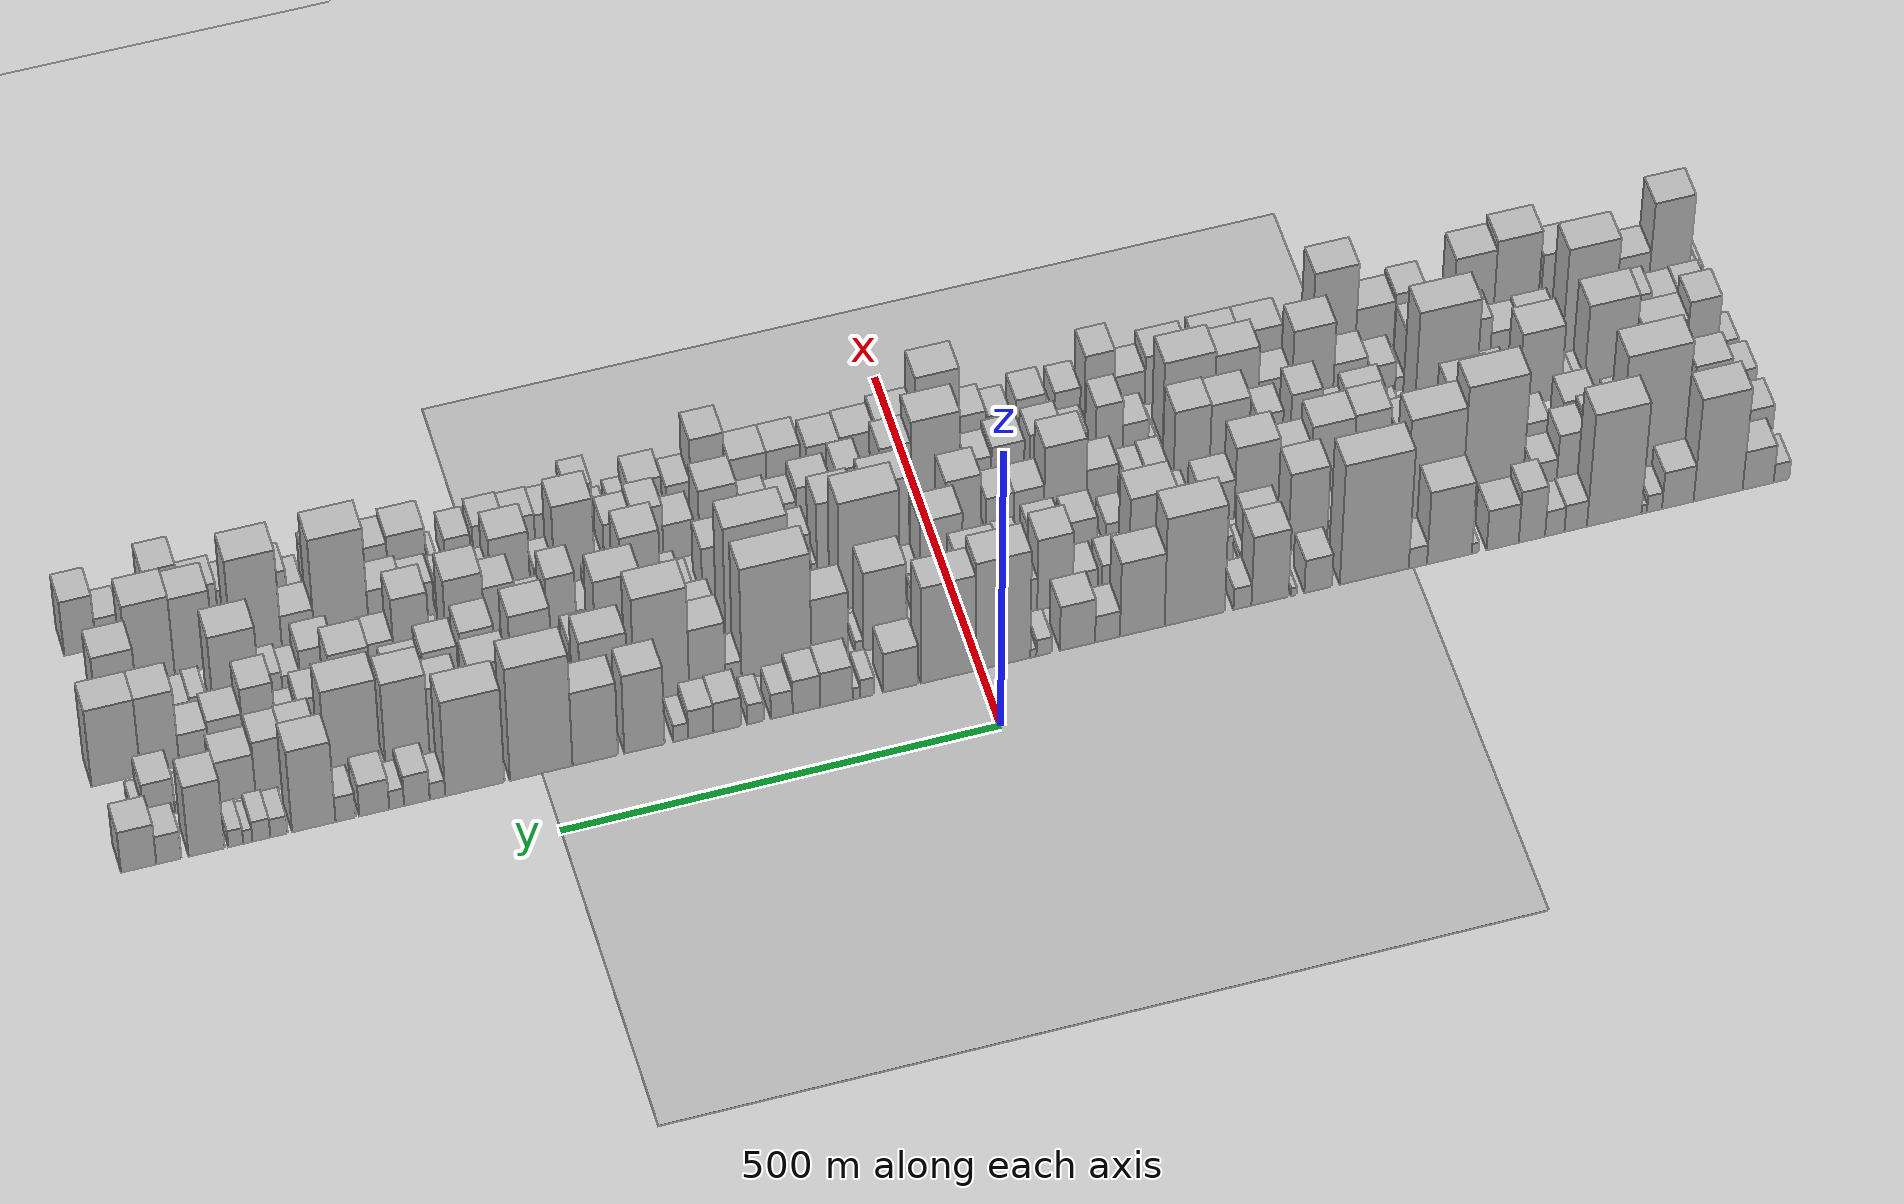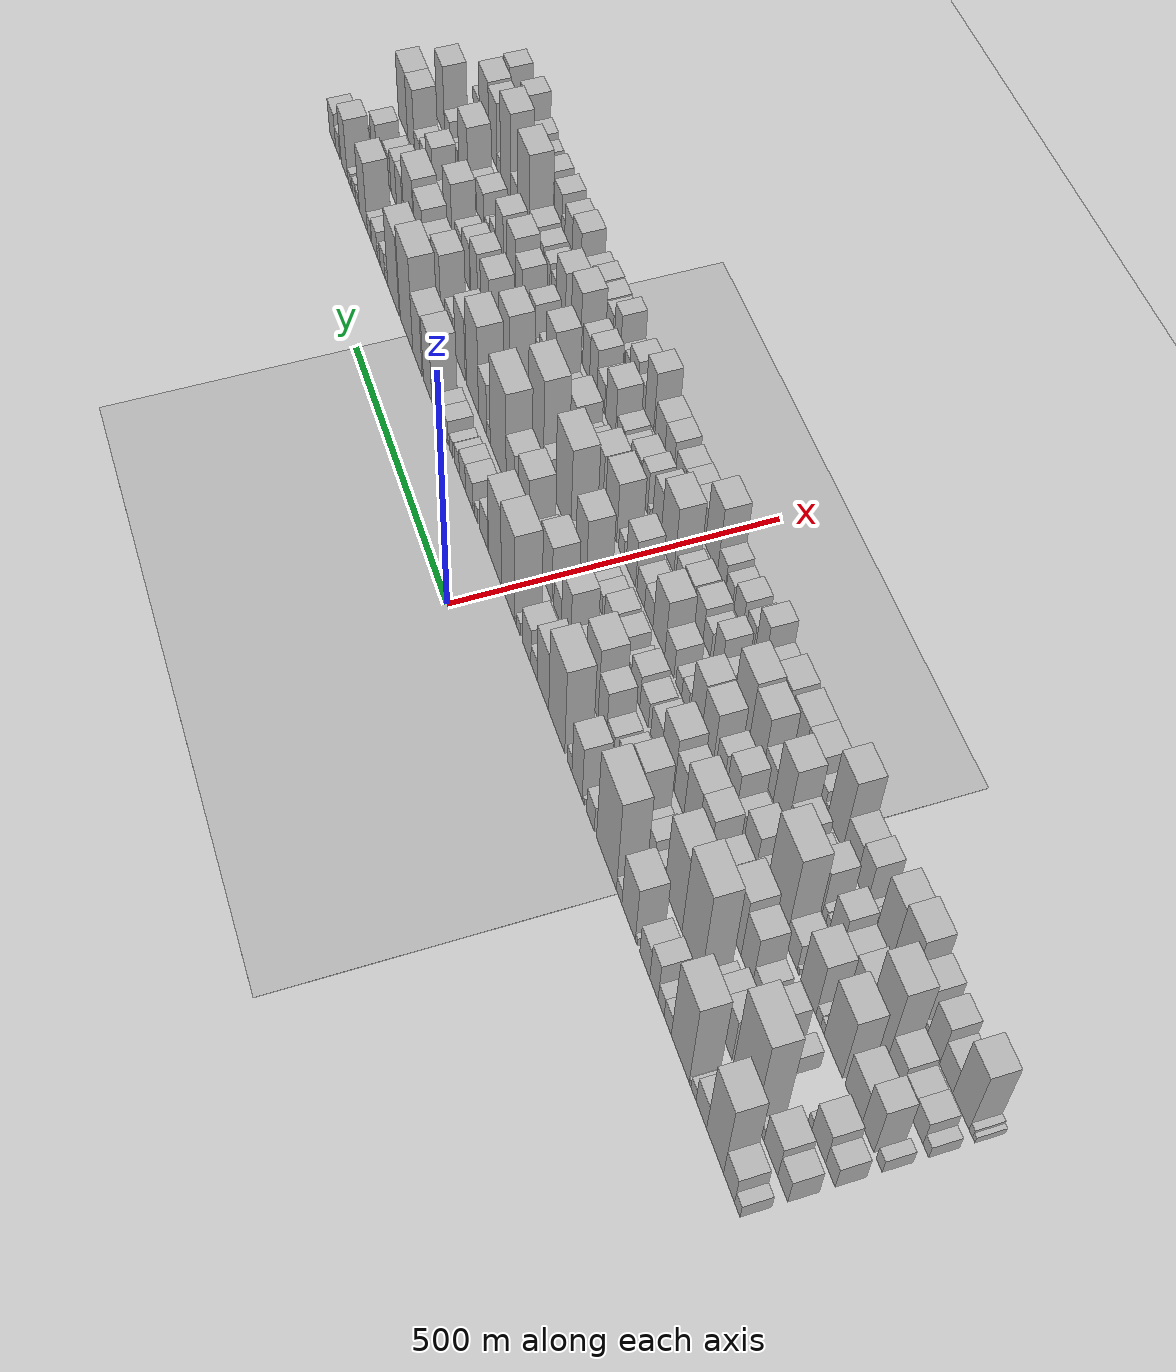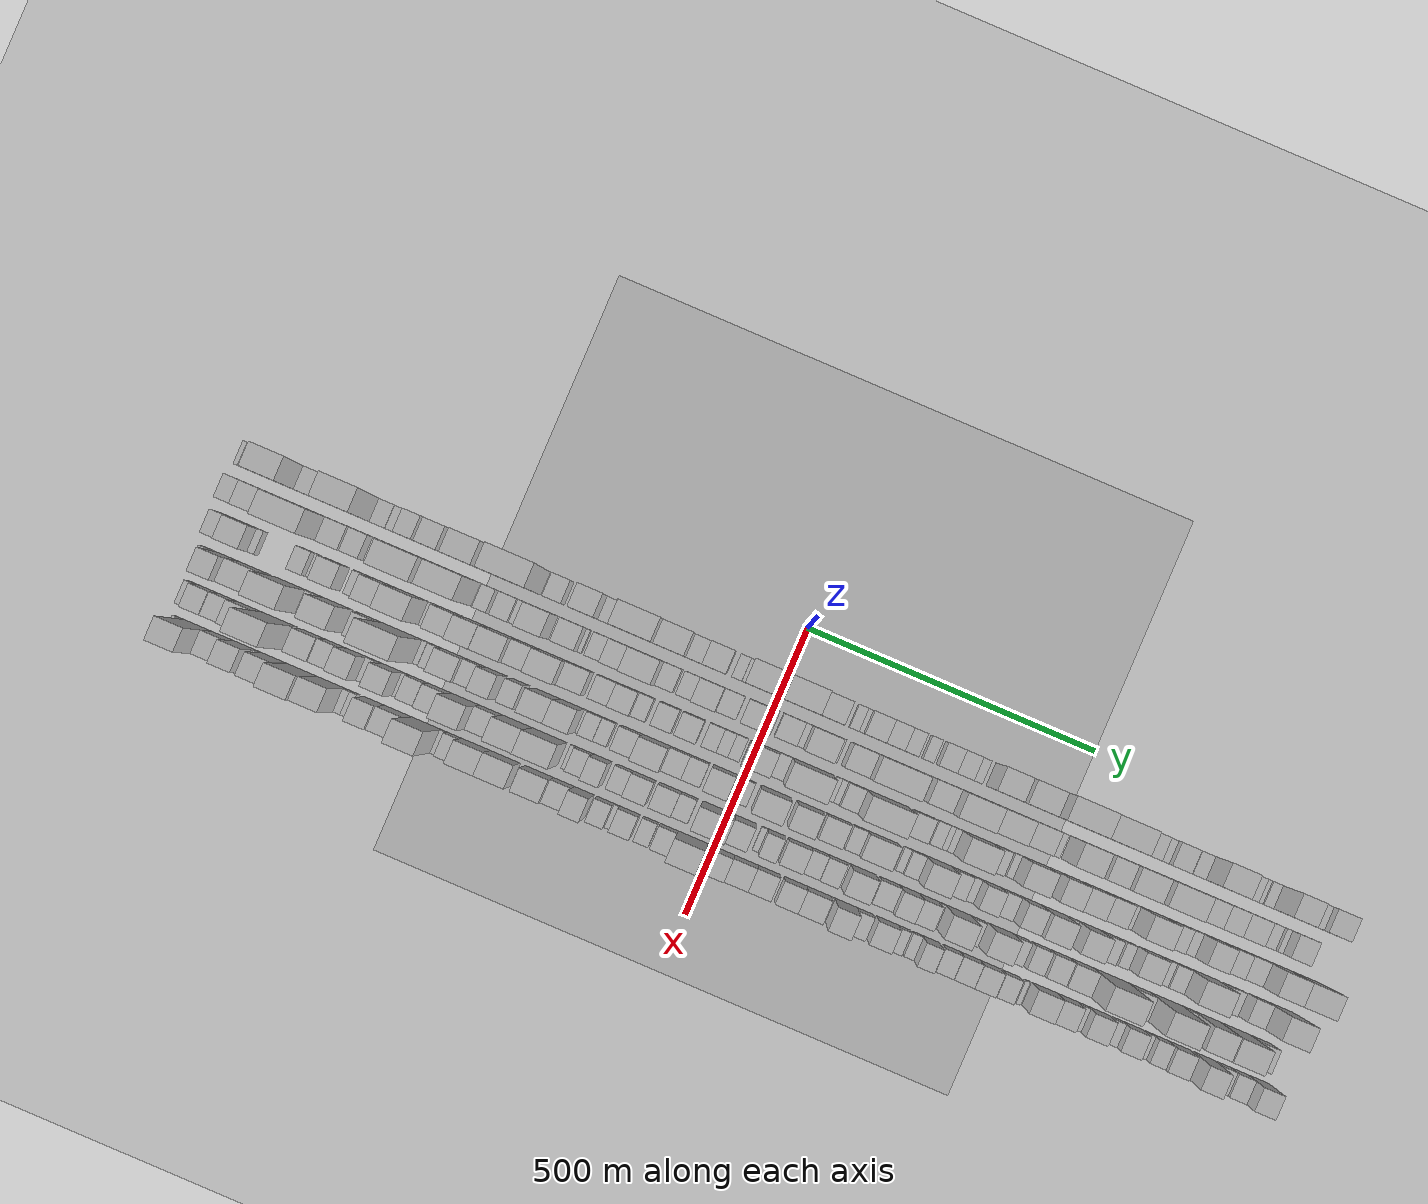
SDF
<?xml version="1.0" encoding="utf-8"?>

<sdf version="1.6">

   <world name="default">

      <gui fullscreen="0">

         <camera name="user_camera">

            <pose>-15 0 4.57585 0 0 0</pose>

            <view_controller>orbit</view_controller>

         </camera>

      </gui>

      <scene>

         <sky>

           <clouds>

             <speed>12</speed>

           </clouds>

         </sky>

         <ambient>0.4 0.4 0.4 1</ambient>

         <background>0.7 0.7 0.7 1</background>

         <shadows>1</shadows>

      </scene>

      <gravity>0 0 -9.8066</gravity>

      <magnetic_field>6e-06 2.3e-05 -4.2e-05</magnetic_field>

      <physics default="0" name="default_physics" type="ode">

         <ode>

            <solver>

               <type>quick</type>

               <iters>10</iters>

               <sor>1.0</sor>

               <use_dynamic_moi_rescaling>0</use_dynamic_moi_rescaling>

            </solver>

            <constraints>

               <cfm>0</cfm>

               <erp>0.2</erp>

               <contact_max_correcting_vel>100</contact_max_correcting_vel>

               <contact_surface_layer>0.001</contact_surface_layer>

            </constraints>

         </ode>

         <max_step_size>0.004</max_step_size>

         <real_time_factor>1</real_time_factor>

         <real_time_update_rate>250</real_time_update_rate>

      </physics>

      <light name="sun" type="directional">

         <cast_shadows>1</cast_shadows>

         <pose>0 0 10 0 0 0</pose>

         <diffuse>0.8 0.8 0.8 1</diffuse>

         <specular>0.2 0.2 0.2 1</specular>

         <attenuation>

            <range>1000</range>

            <constant>0.9</constant>

            <linear>0.01</linear>

            <quadratic>0.001</quadratic>

         </attenuation>

         <direction>-0.5 0.1 -0.9</direction>

      </light>

      <include>

         <name>ground_plane_1</name>

         <uri>model://HANNAS_ground_plane</uri>

         <pose>0 0 0  0 0 0</pose>

      </include>

      <include>

         <name>ground_plane_2</name>

         <uri>model://HANNAS_ground_plane</uri>

         <pose>100 0 0  0 0 0</pose>

      </include>

      <model name="building_1">

         <static>1</static>

         <pose frame="">100.0000 -930.8884 0 0.000000 0.000000 0.000000</pose>

         <link name="link">

            <pose frame="">0 0 16.50 0 0 0</pose>

            <collision name="collision">

               <geometry>

                  <box>

                     <size>40.0000 18.2232 33.0000</size>

                  </box>

               </geometry>

               <max_contacts>10</max_contacts>

               <surface>

                  <contact>

                     <ode/>

                  </contact>

                  <bounce/>

                  <friction>

                     <torsional>

                        <ode/>

                     </torsional>

                     <ode/>

                  </friction>

               </surface>

            </collision>

            <visual name="visual">

               <cast_shadows>0</cast_shadows>

               <geometry>

                  <box>

                     <size>40.0000 18.2232 33.0000</size>

                  </box>

               </geometry>

               <material>

                  <script>

                     <uri>model://HANNAS_wall/materials/scripts</uri>

                     <uri>model://HANNAS_wall/materials/textures</uri>

                     <name>vrc/HANNAS_wall</name>

                  </script>

               </material>

            </visual>

            <self_collide>0</self_collide>

            <enable_wind>0</enable_wind>

            <kinematic>0</kinematic>

         </link>

      </model>

      <model name="building_2">

         <static>1</static>

         <pose frame="">100.0000 -903.4382 0 0.000000 0.000000 0.000000</pose>

         <link name="link">

            <pose frame="">0 0 34.50 0 0 0</pose>

            <collision name="collision">

               <geometry>

                  <box>

                     <size>40.0000 36.6772 69.0000</size>

                  </box>

               </geometry>

               <max_contacts>10</max_contacts>

               <surface>

                  <contact>

                     <ode/>

                  </contact>

                  <bounce/>

                  <friction>

                     <torsional>

                        <ode/>

                     </torsional>

                     <ode/>

                  </friction>

               </surface>

            </collision>

            <visual name="visual">

               <cast_shadows>0</cast_shadows>

               <geometry>

                  <box>

                     <size>40.0000 36.6772 69.0000</size>

                  </box>

               </geometry>

               <material>

                  <script>

                     <uri>model://HANNAS_wall/materials/scripts</uri>

                     <uri>model://HANNAS_wall/materials/textures</uri>

                     <name>vrc/HANNAS_wall</name>

                  </script>

               </material>

            </visual>

            <self_collide>0</self_collide>

            <enable_wind>0</enable_wind>

            <kinematic>0</kinematic>

         </link>

      </model>

      <model name="building_3">

         <static>1</static>

         <pose frame="">100.0000 -856.2771 0 0.000000 0.000000 0.000000</pose>

         <link name="link">

            <pose frame="">0 0 93.00 0 0 0</pose>

            <collision name="collision">

               <geometry>

                  <box>

                     <size>40.0000 57.6450 186.0000</size>

                  </box>

               </geometry>

               <max_contacts>10</max_contacts>

               <surface>

                  <contact>

                     <ode/>

                  </contact>

                  <bounce/>

                  <friction>

                     <torsional>

                        <ode/>

                     </torsional>

                     <ode/>

                  </friction>

               </surface>

            </collision>

            <visual name="visual">

               <cast_shadows>0</cast_shadows>

               <geometry>

                  <box>

                     <size>40.0000 57.6450 186.0000</size>

                  </box>

               </geometry>

               <material>

                  <script>

                     <uri>model://HANNAS_wall/materials/scripts</uri>

                     <uri>model://HANNAS_wall/materials/textures</uri>

                     <name>vrc/HANNAS_wall</name>

                  </script>

               </material>

            </visual>

            <self_collide>0</self_collide>

            <enable_wind>0</enable_wind>

            <kinematic>0</kinematic>

         </link>

      </model>

      <model name="building_4">

         <static>1</static>

         <pose frame="">100.0000 -808.9553 0 0.000000 0.000000 0.000000</pose>

         <link name="link">

            <pose frame="">0 0 33.00 0 0 0</pose>

            <collision name="collision">

               <geometry>

                  <box>

                     <size>40.0000 36.9987 66.0000</size>

                  </box>

               </geometry>

               <max_contacts>10</max_contacts>

               <surface>

                  <contact>

                     <ode/>

                  </contact>

                  <bounce/>

                  <friction>

                     <torsional>

                        <ode/>

                     </torsional>

                     <ode/>

                  </friction>

               </surface>

            </collision>

            <visual name="visual">

               <cast_shadows>0</cast_shadows>

               <geometry>

                  <box>

                     <size>40.0000 36.9987 66.0000</size>

                  </box>

               </geometry>

               <material>

                  <script>

                     <uri>model://HANNAS_wall/materials/scripts</uri>

                     <uri>model://HANNAS_wall/materials/textures</uri>

                     <name>vrc/HANNAS_wall</name>

                  </script>

               </material>

            </visual>

            <self_collide>0</self_collide>

            <enable_wind>0</enable_wind>

            <kinematic>0</kinematic>

         </link>

      </model>

      <model name="building_5">

         <static>1</static>

         <pose frame="">100.0000 -781.5781 0 0.000000 0.000000 0.000000</pose>

         <link name="link">

            <pose frame="">0 0 15.00 0 0 0</pose>

            <collision name="collision">

               <geometry>

                  <box>

                     <size>40.0000 17.7556 30.0000</size>

                  </box>

               </geometry>

               <max_contacts>10</max_contacts>

               <surface>

                  <contact>

                     <ode/>

                  </contact>

                  <bounce/>

                  <friction>

                     <torsional>

                        <ode/>

                     </torsional>

                     <ode/>

                  </friction>

               </surface>

            </collision>

            <visual name="visual">

               <cast_shadows>0</cast_shadows>

               <geometry>

                  <box>

                     <size>40.0000 17.7556 30.0000</size>

                  </box>

               </geometry>

               <material>

                  <script>

                     <uri>model://HANNAS_wall/materials/scripts</uri>

                     <uri>model://HANNAS_wall/materials/textures</uri>

                     <name>vrc/HANNAS_wall</name>

                  </script>

               </material>

            </visual>

            <self_collide>0</self_collide>

            <enable_wind>0</enable_wind>

            <kinematic>0</kinematic>

         </link>

      </model>

      <model name="building_6">

         <static>1</static>

         <pose frame="">100.0000 -769.4728 0 0.000000 0.000000 0.000000</pose>

         <link name="link">

            <pose frame="">0 0 7.50 0 0 0</pose>

            <collision name="collision">

               <geometry>

                  <box>

                     <size>40.0000 6.4549 15.0000</size>

                  </box>

               </geometry>

               <max_contacts>10</max_contacts>

               <surface>

                  <contact>

                     <ode/>

                  </contact>

                  <bounce/>

                  <friction>

                     <torsional>

                        <ode/>

                     </torsional>

                     <ode/>

                  </friction>

               </surface>

            </collision>

            <visual name="visual">

               <cast_shadows>0</cast_shadows>

               <geometry>

                  <box>

                     <size>40.0000 6.4549 15.0000</size>

                  </box>

               </geometry>

               <material>

                  <script>

                     <uri>model://HANNAS_wall/materials/scripts</uri>

                     <uri>model://HANNAS_wall/materials/textures</uri>

                     <name>vrc/HANNAS_wall</name>

                  </script>

               </material>

            </visual>

            <self_collide>0</self_collide>

            <enable_wind>0</enable_wind>

            <kinematic>0</kinematic>

         </link>

      </model>

      <model name="building_7">

         <static>1</static>

         <pose frame="">100.0000 -734.3356 0 0.000000 0.000000 0.000000</pose>

         <link name="link">

            <pose frame="">0 0 102.00 0 0 0</pose>

            <collision name="collision">

               <geometry>

                  <box>

                     <size>40.0000 63.8197 204.0000</size>

                  </box>

               </geometry>

               <max_contacts>10</max_contacts>

               <surface>

                  <contact>

                     <ode/>

                  </contact>

                  <bounce/>

                  <friction>

                     <torsional>

                        <ode/>

                     </torsional>

                     <ode/>

                  </friction>

               </surface>

            </collision>

            <visual name="visual">

               <cast_shadows>0</cast_shadows>

               <geometry>

                  <box>

                     <size>40.0000 63.8197 204.0000</size>

                  </box>

               </geometry>

               <material>

                  <script>

                     <uri>model://HANNAS_wall/materials/scripts</uri>

                     <uri>model://HANNAS_wall/materials/textures</uri>

                     <name>vrc/HANNAS_wall</name>

                  </script>

               </material>

            </visual>

            <self_collide>0</self_collide>

            <enable_wind>0</enable_wind>

            <kinematic>0</kinematic>

         </link>

      </model>

      <model name="building_8">

         <static>1</static>

         <pose frame="">100.0000 -689.2646 0 0.000000 0.000000 0.000000</pose>

         <link name="link">

            <pose frame="">0 0 24.00 0 0 0</pose>

            <collision name="collision">

               <geometry>

                  <box>

                     <size>40.0000 26.3223 48.0000</size>

                  </box>

               </geometry>

               <max_contacts>10</max_contacts>

               <surface>

                  <contact>

                     <ode/>

                  </contact>

                  <bounce/>

                  <friction>

                     <torsional>

                        <ode/>

                     </torsional>

                     <ode/>

                  </friction>

               </surface>

            </collision>

            <visual name="visual">

               <cast_shadows>0</cast_shadows>

               <geometry>

                  <box>

                     <size>40.0000 26.3223 48.0000</size>

                  </box>

               </geometry>

               <material>

                  <script>

                     <uri>model://HANNAS_wall/materials/scripts</uri>

                     <uri>model://HANNAS_wall/materials/textures</uri>

                     <name>vrc/HANNAS_wall</name>

                  </script>

               </material>

            </visual>

            <self_collide>0</self_collide>

            <enable_wind>0</enable_wind>

            <kinematic>0</kinematic>

         </link>

      </model>

      <model name="building_9">

         <static>1</static>

         <pose frame="">100.0000 -664.7763 0 0.000000 0.000000 0.000000</pose>

         <link name="link">

            <pose frame="">0 0 22.50 0 0 0</pose>

            <collision name="collision">

               <geometry>

                  <box>

                     <size>40.0000 22.6542 45.0000</size>

                  </box>

               </geometry>

               <max_contacts>10</max_contacts>

               <surface>

                  <contact>

                     <ode/>

                  </contact>

                  <bounce/>

                  <friction>

                     <torsional>

                        <ode/>

                     </torsional>

                     <ode/>

                  </friction>

               </surface>

            </collision>

            <visual name="visual">

               <cast_shadows>0</cast_shadows>

               <geometry>

                  <box>

                     <size>40.0000 22.6542 45.0000</size>

                  </box>

               </geometry>

               <material>

                  <script>

                     <uri>model://HANNAS_wall/materials/scripts</uri>

                     <uri>model://HANNAS_wall/materials/textures</uri>

                     <name>vrc/HANNAS_wall</name>

                  </script>

               </material>

            </visual>

            <self_collide>0</self_collide>

            <enable_wind>0</enable_wind>

            <kinematic>0</kinematic>

         </link>

      </model>

      <model name="building_10">

         <static>1</static>

         <pose frame="">100.0000 -638.0792 0 0.000000 0.000000 0.000000</pose>

         <link name="link">

            <pose frame="">0 0 46.50 0 0 0</pose>

            <collision name="collision">

               <geometry>

                  <box>

                     <size>40.0000 30.7400 93.0000</size>

                  </box>

               </geometry>

               <max_contacts>10</max_contacts>

               <surface>

                  <contact>

                     <ode/>

                  </contact>

                  <bounce/>

                  <friction>

                     <torsional>

                        <ode/>

                     </torsional>

                     <ode/>

                  </friction>

               </surface>

            </collision>

            <visual name="visual">

               <cast_shadows>0</cast_shadows>

               <geometry>

                  <box>

                     <size>40.0000 30.7400 93.0000</size>

                  </box>

               </geometry>

               <material>

                  <script>

                     <uri>model://HANNAS_wall/materials/scripts</uri>

                     <uri>model://HANNAS_wall/materials/textures</uri>

                     <name>vrc/HANNAS_wall</name>

                  </script>

               </material>

            </visual>

            <self_collide>0</self_collide>

            <enable_wind>0</enable_wind>

            <kinematic>0</kinematic>

         </link>

      </model>

      <model name="building_11">

         <static>1</static>

         <pose frame="">100.0000 -603.9201 0 0.000000 0.000000 0.000000</pose>

         <link name="link">

            <pose frame="">0 0 36.00 0 0 0</pose>

            <collision name="collision">

               <geometry>

                  <box>

                     <size>40.0000 37.5782 72.0000</size>

                  </box>

               </geometry>

               <max_contacts>10</max_contacts>

               <surface>

                  <contact>

                     <ode/>

                  </contact>

                  <bounce/>

                  <friction>

                     <torsional>

                        <ode/>

                     </torsional>

                     <ode/>

                  </friction>

               </surface>

            </collision>

            <visual name="visual">

               <cast_shadows>0</cast_shadows>

               <geometry>

                  <box>

                     <size>40.0000 37.5782 72.0000</size>

                  </box>

               </geometry>

               <material>

                  <script>

                     <uri>model://HANNAS_wall/materials/scripts</uri>

                     <uri>model://HANNAS_wall/materials/textures</uri>

                     <name>vrc/HANNAS_wall</name>

                  </script>

               </material>

            </visual>

            <self_collide>0</self_collide>

            <enable_wind>0</enable_wind>

            <kinematic>0</kinematic>

         </link>

      </model>

      <model name="building_12">

         <static>1</static>

         <pose frame="">100.0000 -571.9970 0 0.000000 0.000000 0.000000</pose>

         <link name="link">

            <pose frame="">0 0 9.00 0 0 0</pose>

            <collision name="collision">

               <geometry>

                  <box>

                     <size>40.0000 8.2681 18.0000</size>

                  </box>

               </geometry>

               <max_contacts>10</max_contacts>

               <surface>

                  <contact>

                     <ode/>

                  </contact>

                  <bounce/>

                  <friction>

                     <torsional>

                        <ode/>

                     </torsional>

                     <ode/>

                  </friction>

               </surface>

            </collision>

            <visual name="visual">

               <cast_shadows>0</cast_shadows>

               <geometry>

                  <box>

                     <size>40.0000 8.2681 18.0000</size>

                  </box>

               </geometry>

               <material>

                  <script>

                     <uri>model://HANNAS_wall/materials/scripts</uri>

                     <uri>model://HANNAS_wall/materials/textures</uri>

                     <name>vrc/HANNAS_wall</name>

                  </script>

               </material>

            </visual>

            <self_collide>0</self_collide>

            <enable_wind>0</enable_wind>

            <kinematic>0</kinematic>

         </link>

      </model>

      <model name="building_13">

         <static>1</static>

         <pose frame="">100.0000 -541.7724 0 0.000000 0.000000 0.000000</pose>

         <link name="link">

            <pose frame="">0 0 66.00 0 0 0</pose>

            <collision name="collision">

               <geometry>

                  <box>

                     <size>40.0000 52.1810 132.0000</size>

                  </box>

               </geometry>

               <max_contacts>10</max_contacts>

               <surface>

                  <contact>

                     <ode/>

                  </contact>

                  <bounce/>

                  <friction>

                     <torsional>

                        <ode/>

                     </torsional>

                     <ode/>

                  </friction>

               </surface>

            </collision>

            <visual name="visual">

               <cast_shadows>0</cast_shadows>

               <geometry>

                  <box>

                     <size>40.0000 52.1810 132.0000</size>

                  </box>

               </geometry>

               <material>

                  <script>

                     <uri>model://HANNAS_wall/materials/scripts</uri>

                     <uri>model://HANNAS_wall/materials/textures</uri>

                     <name>vrc/HANNAS_wall</name>

                  </script>

               </material>

            </visual>

            <self_collide>0</self_collide>

            <enable_wind>0</enable_wind>

            <kinematic>0</kinematic>

         </link>

      </model>

      <model name="building_14">

         <static>1</static>

         <pose frame="">100.0000 -505.0109 0 0.000000 0.000000 0.000000</pose>

         <link name="link">

            <pose frame="">0 0 18.00 0 0 0</pose>

            <collision name="collision">

               <geometry>

                  <box>

                     <size>40.0000 21.3421 36.0000</size>

                  </box>

               </geometry>

               <max_contacts>10</max_contacts>

               <surface>

                  <contact>

                     <ode/>

                  </contact>

                  <bounce/>

                  <friction>

                     <torsional>

                        <ode/>

                     </torsional>

                     <ode/>

                  </friction>

               </surface>

            </collision>

            <visual name="visual">

               <cast_shadows>0</cast_shadows>

               <geometry>

                  <box>

                     <size>40.0000 21.3421 36.0000</size>

                  </box>

               </geometry>

               <material>

                  <script>

                     <uri>model://HANNAS_wall/materials/scripts</uri>

                     <uri>model://HANNAS_wall/materials/textures</uri>

                     <name>vrc/HANNAS_wall</name>

                  </script>

               </material>

            </visual>

            <self_collide>0</self_collide>

            <enable_wind>0</enable_wind>

            <kinematic>0</kinematic>

         </link>

      </model>

      <model name="building_15">

         <static>1</static>

         <pose frame="">100.0000 -454.2661 0 0.000000 0.000000 0.000000</pose>

         <link name="link">

            <pose frame="">0 0 109.50 0 0 0</pose>

            <collision name="collision">

               <geometry>

                  <box>

                     <size>40.0000 80.1474 219.0000</size>

                  </box>

               </geometry>

               <max_contacts>10</max_contacts>

               <surface>

                  <contact>

                     <ode/>

                  </contact>

                  <bounce/>

                  <friction>

                     <torsional>

                        <ode/>

                     </torsional>

                     <ode/>

                  </friction>

               </surface>

            </collision>

            <visual name="visual">

               <cast_shadows>0</cast_shadows>

               <geometry>

                  <box>

                     <size>40.0000 80.1474 219.0000</size>

                  </box>

               </geometry>

               <material>

                  <script>

                     <uri>model://HANNAS_wall/materials/scripts</uri>

                     <uri>model://HANNAS_wall/materials/textures</uri>

                     <name>vrc/HANNAS_wall</name>

                  </script>

               </material>

            </visual>

            <self_collide>0</self_collide>

            <enable_wind>0</enable_wind>

            <kinematic>0</kinematic>

         </link>

      </model>

      <model name="building_16">

         <static>1</static>

         <pose frame="">100.0000 -389.1485 0 0.000000 0.000000 0.000000</pose>

         <link name="link">

            <pose frame="">0 0 30.00 0 0 0</pose>

            <collision name="collision">

               <geometry>

                  <box>

                     <size>40.0000 32.0879 60.0000</size>

                  </box>

               </geometry>

               <max_contacts>10</max_contacts>

               <surface>

                  <contact>

                     <ode/>

                  </contact>

                  <bounce/>

                  <friction>

                     <torsional>

                        <ode/>

                     </torsional>

                     <ode/>

                  </friction>

               </surface>

            </collision>

            <visual name="visual">

               <cast_shadows>0</cast_shadows>

               <geometry>

                  <box>

                     <size>40.0000 32.0879 60.0000</size>

                  </box>

               </geometry>

               <material>

                  <script>

                     <uri>model://HANNAS_wall/materials/scripts</uri>

                     <uri>model://HANNAS_wall/materials/textures</uri>

                     <name>vrc/HANNAS_wall</name>

                  </script>

               </material>

            </visual>

            <self_collide>0</self_collide>

            <enable_wind>0</enable_wind>

            <kinematic>0</kinematic>

         </link>

      </model>

      <model name="building_17">

         <static>1</static>

         <pose frame="">100.0000 -360.9541 0 0.000000 0.000000 0.000000</pose>

         <link name="link">

            <pose frame="">0 0 7.50 0 0 0</pose>

            <collision name="collision">

               <geometry>

                  <box>

                     <size>40.0000 6.3009 15.0000</size>

                  </box>

               </geometry>

               <max_contacts>10</max_contacts>

               <surface>

                  <contact>

                     <ode/>

                  </contact>

                  <bounce/>

                  <friction>

                     <torsional>

                        <ode/>

                     </torsional>

                     <ode/>

                  </friction>

               </surface>

            </collision>

            <visual name="visual">

               <cast_shadows>0</cast_shadows>

               <geometry>

                  <box>

                     <size>40.0000 6.3009 15.0000</size>

                  </box>

               </geometry>

               <material>

                  <script>

                     <uri>model://HANNAS_wall/materials/scripts</uri>

                     <uri>model://HANNAS_wall/materials/textures</uri>

                     <name>vrc/HANNAS_wall</name>

                  </script>

               </material>

            </visual>

            <self_collide>0</self_collide>

            <enable_wind>0</enable_wind>

            <kinematic>0</kinematic>

         </link>

      </model>

      <model name="building_18">

         <static>1</static>

         <pose frame="">100.0000 -333.2921 0 0.000000 0.000000 0.000000</pose>

         <link name="link">

            <pose frame="">0 0 63.00 0 0 0</pose>

            <collision name="collision">

               <geometry>

                  <box>

                     <size>40.0000 43.0232 126.0000</size>

                  </box>

               </geometry>

               <max_contacts>10</max_contacts>

               <surface>

                  <contact>

                     <ode/>

                  </contact>

                  <bounce/>

                  <friction>

                     <torsional>

                        <ode/>

                     </torsional>

                     <ode/>

                  </friction>

               </surface>

            </collision>

            <visual name="visual">

               <cast_shadows>0</cast_shadows>

               <geometry>

                  <box>

                     <size>40.0000 43.0232 126.0000</size>

                  </box>

               </geometry>

               <material>

                  <script>

                     <uri>model://HANNAS_wall/materials/scripts</uri>

                     <uri>model://HANNAS_wall/materials/textures</uri>

                     <name>vrc/HANNAS_wall</name>

                  </script>

               </material>

            </visual>

            <self_collide>0</self_collide>

            <enable_wind>0</enable_wind>

            <kinematic>0</kinematic>

         </link>

      </model>

      <model name="building_19">

         <static>1</static>

         <pose frame="">100.0000 -301.3804 0 0.000000 0.000000 0.000000</pose>

         <link name="link">

            <pose frame="">0 0 19.50 0 0 0</pose>

            <collision name="collision">

               <geometry>

                  <box>

                     <size>40.0000 20.8003 39.0000</size>

                  </box>

               </geometry>

               <max_contacts>10</max_contacts>

               <surface>

                  <contact>

                     <ode/>

                  </contact>

                  <bounce/>

                  <friction>

                     <torsional>

                        <ode/>

                     </torsional>

                     <ode/>

                  </friction>

               </surface>

            </collision>

            <visual name="visual">

               <cast_shadows>0</cast_shadows>

               <geometry>

                  <box>

                     <size>40.0000 20.8003 39.0000</size>

                  </box>

               </geometry>

               <material>

                  <script>

                     <uri>model://HANNAS_wall/materials/scripts</uri>

                     <uri>model://HANNAS_wall/materials/textures</uri>

                     <name>vrc/HANNAS_wall</name>

                  </script>

               </material>

            </visual>

            <self_collide>0</self_collide>

            <enable_wind>0</enable_wind>

            <kinematic>0</kinematic>

         </link>

      </model>

      <model name="building_20">

         <static>1</static>

         <pose frame="">100.0000 -246.1595 0 0.000000 0.000000 0.000000</pose>

         <link name="link">

            <pose frame="">0 0 99.00 0 0 0</pose>

            <collision name="collision">

               <geometry>

                  <box>

                     <size>40.0000 69.6414 198.0000</size>

                  </box>

               </geometry>

               <max_contacts>10</max_contacts>

               <surface>

                  <contact>

                     <ode/>

                  </contact>

                  <bounce/>

                  <friction>

                     <torsional>

                        <ode/>

                     </torsional>

                     <ode/>

                  </friction>

               </surface>

            </collision>

            <visual name="visual">

               <cast_shadows>0</cast_shadows>

               <geometry>

                  <box>

                     <size>40.0000 69.6414 198.0000</size>

                  </box>

               </geometry>

               <material>

                  <script>

                     <uri>model://HANNAS_wall/materials/scripts</uri>

                     <uri>model://HANNAS_wall/materials/textures</uri>

                     <name>vrc/HANNAS_wall</name>

                  </script>

               </material>

            </visual>

            <self_collide>0</self_collide>

            <enable_wind>0</enable_wind>

            <kinematic>0</kinematic>

         </link>

      </model>

      <model name="building_21">

         <static>1</static>

         <pose frame="">100.0000 -185.6320 0 0.000000 0.000000 0.000000</pose>

         <link name="link">

            <pose frame="">0 0 67.50 0 0 0</pose>

            <collision name="collision">

               <geometry>

                  <box>

                     <size>40.0000 51.4138 135.0000</size>

                  </box>

               </geometry>

               <max_contacts>10</max_contacts>

               <surface>

                  <contact>

                     <ode/>

                  </contact>

                  <bounce/>

                  <friction>

                     <torsional>

                        <ode/>

                     </torsional>

                     <ode/>

                  </friction>

               </surface>

            </collision>

            <visual name="visual">

               <cast_shadows>0</cast_shadows>

               <geometry>

                  <box>

                     <size>40.0000 51.4138 135.0000</size>

                  </box>

               </geometry>

               <material>

                  <script>

                     <uri>model://HANNAS_wall/materials/scripts</uri>

                     <uri>model://HANNAS_wall/materials/textures</uri>

                     <name>vrc/HANNAS_wall</name>

                  </script>

               </material>

            </visual>

            <self_collide>0</self_collide>

            <enable_wind>0</enable_wind>

            <kinematic>0</kinematic>

         </link>

      </model>

      <model name="building_22">

         <static>1</static>

         <pose frame="">100.0000 -145.6311 0 0.000000 0.000000 0.000000</pose>

         <link name="link">

            <pose frame="">0 0 24.00 0 0 0</pose>

            <collision name="collision">

               <geometry>

                  <box>

                     <size>40.0000 28.5881 48.0000</size>

                  </box>

               </geometry>

               <max_contacts>10</max_contacts>

               <surface>

                  <contact>

                     <ode/>

                  </contact>

                  <bounce/>

                  <friction>

                     <torsional>

                        <ode/>

                     </torsional>

                     <ode/>

                  </friction>

               </surface>

            </collision>

            <visual name="visual">

               <cast_shadows>0</cast_shadows>

               <geometry>

                  <box>

                     <size>40.0000 28.5881 48.0000</size>

                  </box>

               </geometry>

               <material>

                  <script>

                     <uri>model://HANNAS_wall/materials/scripts</uri>

                     <uri>model://HANNAS_wall/materials/textures</uri>

                     <name>vrc/HANNAS_wall</name>

                  </script>

               </material>

            </visual>

            <self_collide>0</self_collide>

            <enable_wind>0</enable_wind>

            <kinematic>0</kinematic>

         </link>

      </model>

      <model name="building_23">

         <static>1</static>

         <pose frame="">100.0000 -111.0556 0 0.000000 0.000000 0.000000</pose>

         <link name="link">

            <pose frame="">0 0 40.50 0 0 0</pose>

            <collision name="collision">

               <geometry>

                  <box>

                     <size>40.0000 40.5629 81.0000</size>

                  </box>

               </geometry>

               <max_contacts>10</max_contacts>

               <surface>

                  <contact>

                     <ode/>

                  </contact>

                  <bounce/>

                  <friction>

                     <torsional>

                        <ode/>

                     </torsional>

                     <ode/>

                  </friction>

               </surface>

            </collision>

            <visual name="visual">

               <cast_shadows>0</cast_shadows>

               <geometry>

                  <box>

                     <size>40.0000 40.5629 81.0000</size>

                  </box>

               </geometry>

               <material>

                  <script>

                     <uri>model://HANNAS_wall/materials/scripts</uri>

                     <uri>model://HANNAS_wall/materials/textures</uri>

                     <name>vrc/HANNAS_wall</name>

                  </script>

               </material>

            </visual>

            <self_collide>0</self_collide>

            <enable_wind>0</enable_wind>

            <kinematic>0</kinematic>

         </link>

      </model>

      <model name="building_24">

         <static>1</static>

         <pose frame="">100.0000 -72.7800 0 0.000000 0.000000 0.000000</pose>

         <link name="link">

            <pose frame="">0 0 15.00 0 0 0</pose>

            <collision name="collision">

               <geometry>

                  <box>

                     <size>40.0000 17.9882 30.0000</size>

                  </box>

               </geometry>

               <max_contacts>10</max_contacts>

               <surface>

                  <contact>

                     <ode/>

                  </contact>

                  <bounce/>

                  <friction>

                     <torsional>

                        <ode/>

                     </torsional>

                     <ode/>

                  </friction>

               </surface>

            </collision>

            <visual name="visual">

               <cast_shadows>0</cast_shadows>

               <geometry>

                  <box>

                     <size>40.0000 17.9882 30.0000</size>

                  </box>

               </geometry>

               <material>

                  <script>

                     <uri>model://HANNAS_wall/materials/scripts</uri>

                     <uri>model://HANNAS_wall/materials/textures</uri>

                     <name>vrc/HANNAS_wall</name>

                  </script>

               </material>

            </visual>

            <self_collide>0</self_collide>

            <enable_wind>0</enable_wind>

            <kinematic>0</kinematic>

         </link>

      </model>

      <model name="building_25">

         <static>1</static>

         <pose frame="">100.0000 -60.3088 0 0.000000 0.000000 0.000000</pose>

         <link name="link">

            <pose frame="">0 0 7.50 0 0 0</pose>

            <collision name="collision">

               <geometry>

                  <box>

                     <size>40.0000 6.9542 15.0000</size>

                  </box>

               </geometry>

               <max_contacts>10</max_contacts>

               <surface>

                  <contact>

                     <ode/>

                  </contact>

                  <bounce/>

                  <friction>

                     <torsional>

                        <ode/>

                     </torsional>

                     <ode/>

                  </friction>

               </surface>

            </collision>

            <visual name="visual">

               <cast_shadows>0</cast_shadows>

               <geometry>

                  <box>

                     <size>40.0000 6.9542 15.0000</size>

                  </box>

               </geometry>

               <material>

                  <script>

                     <uri>model://HANNAS_wall/materials/scripts</uri>

                     <uri>model://HANNAS_wall/materials/textures</uri>

                     <name>vrc/HANNAS_wall</name>

                  </script>

               </material>

            </visual>

            <self_collide>0</self_collide>

            <enable_wind>0</enable_wind>

            <kinematic>0</kinematic>

         </link>

      </model>

      <model name="building_26">

         <static>1</static>

         <pose frame="">100.0000 -25.2397 0 0.000000 0.000000 0.000000</pose>

         <link name="link">

            <pose frame="">0 0 99.00 0 0 0</pose>

            <collision name="collision">

               <geometry>

                  <box>

                     <size>40.0000 63.1840 198.0000</size>

                  </box>

               </geometry>

               <max_contacts>10</max_contacts>

               <surface>

                  <contact>

                     <ode/>

                  </contact>

                  <bounce/>

                  <friction>

                     <torsional>

                        <ode/>

                     </torsional>

                     <ode/>

                  </friction>

               </surface>

            </collision>

            <visual name="visual">

               <cast_shadows>0</cast_shadows>

               <geometry>

                  <box>

                     <size>40.0000 63.1840 198.0000</size>

                  </box>

               </geometry>

               <material>

                  <script>

                     <uri>model://HANNAS_wall/materials/scripts</uri>

                     <uri>model://HANNAS_wall/materials/textures</uri>

                     <name>vrc/HANNAS_wall</name>

                  </script>

               </material>

            </visual>

            <self_collide>0</self_collide>

            <enable_wind>0</enable_wind>

            <kinematic>0</kinematic>

         </link>

      </model>

      <model name="building_27">

         <static>1</static>

         <pose frame="">100.0000 37.5403 0 0.000000 0.000000 0.000000</pose>

         <link name="link">

            <pose frame="">0 0 88.50 0 0 0</pose>

            <collision name="collision">

               <geometry>

                  <box>

                     <size>40.0000 62.3761 177.0000</size>

                  </box>

               </geometry>

               <max_contacts>10</max_contacts>

               <surface>

                  <contact>

                     <ode/>

                  </contact>

                  <bounce/>

                  <friction>

                     <torsional>

                        <ode/>

                     </torsional>

                     <ode/>

                  </friction>

               </surface>

            </collision>

            <visual name="visual">

               <cast_shadows>0</cast_shadows>

               <geometry>

                  <box>

                     <size>40.0000 62.3761 177.0000</size>

                  </box>

               </geometry>

               <material>

                  <script>

                     <uri>model://HANNAS_wall/materials/scripts</uri>

                     <uri>model://HANNAS_wall/materials/textures</uri>

                     <name>vrc/HANNAS_wall</name>

                  </script>

               </material>

            </visual>

            <self_collide>0</self_collide>

            <enable_wind>0</enable_wind>

            <kinematic>0</kinematic>

         </link>

      </model>

      <model name="building_28">

         <static>1</static>

         <pose frame="">100.0000 91.8347 0 0.000000 0.000000 0.000000</pose>

         <link name="link">

            <pose frame="">0 0 36.00 0 0 0</pose>

            <collision name="collision">

               <geometry>

                  <box>

                     <size>40.0000 40.2126 72.0000</size>

                  </box>

               </geometry>

               <max_contacts>10</max_contacts>

               <surface>

                  <contact>

                     <ode/>

                  </contact>

                  <bounce/>

                  <friction>

                     <torsional>

                        <ode/>

                     </torsional>

                     <ode/>

                  </friction>

               </surface>

            </collision>

            <visual name="visual">

               <cast_shadows>0</cast_shadows>

               <geometry>

                  <box>

                     <size>40.0000 40.2126 72.0000</size>

                  </box>

               </geometry>

               <material>

                  <script>

                     <uri>model://HANNAS_wall/materials/scripts</uri>

                     <uri>model://HANNAS_wall/materials/textures</uri>

                     <name>vrc/HANNAS_wall</name>

                  </script>

               </material>

            </visual>

            <self_collide>0</self_collide>

            <enable_wind>0</enable_wind>

            <kinematic>0</kinematic>

         </link>

      </model>

      <model name="building_29">

         <static>1</static>

         <pose frame="">100.0000 130.2012 0 0.000000 0.000000 0.000000</pose>

         <link name="link">

            <pose frame="">0 0 16.50 0 0 0</pose>

            <collision name="collision">

               <geometry>

                  <box>

                     <size>40.0000 16.5202 33.0000</size>

                  </box>

               </geometry>

               <max_contacts>10</max_contacts>

               <surface>

                  <contact>

                     <ode/>

                  </contact>

                  <bounce/>

                  <friction>

                     <torsional>

                        <ode/>

                     </torsional>

                     <ode/>

                  </friction>

               </surface>

            </collision>

            <visual name="visual">

               <cast_shadows>0</cast_shadows>

               <geometry>

                  <box>

                     <size>40.0000 16.5202 33.0000</size>

                  </box>

               </geometry>

               <material>

                  <script>

                     <uri>model://HANNAS_wall/materials/scripts</uri>

                     <uri>model://HANNAS_wall/materials/textures</uri>

                     <name>vrc/HANNAS_wall</name>

                  </script>

               </material>

            </visual>

            <self_collide>0</self_collide>

            <enable_wind>0</enable_wind>

            <kinematic>0</kinematic>

         </link>

      </model>

      <model name="building_30">

         <static>1</static>

         <pose frame="">100.0000 142.7004 0 0.000000 0.000000 0.000000</pose>

         <link name="link">

            <pose frame="">0 0 10.50 0 0 0</pose>

            <collision name="collision">

               <geometry>

                  <box>

                     <size>40.0000 8.4783 21.0000</size>

                  </box>

               </geometry>

               <max_contacts>10</max_contacts>

               <surface>

                  <contact>

                     <ode/>

                  </contact>

                  <bounce/>

                  <friction>

                     <torsional>

                        <ode/>

                     </torsional>

                     <ode/>

                  </friction>

               </surface>

            </collision>

            <visual name="visual">

               <cast_shadows>0</cast_shadows>

               <geometry>

                  <box>

                     <size>40.0000 8.4783 21.0000</size>

                  </box>

               </geometry>

               <material>

                  <script>

                     <uri>model://HANNAS_wall/materials/scripts</uri>

                     <uri>model://HANNAS_wall/materials/textures</uri>

                     <name>vrc/HANNAS_wall</name>

                  </script>

               </material>

            </visual>

            <self_collide>0</self_collide>

            <enable_wind>0</enable_wind>

            <kinematic>0</kinematic>

         </link>

      </model>

      <model name="building_31">

         <static>1</static>

         <pose frame="">100.0000 165.3753 0 0.000000 0.000000 0.000000</pose>

         <link name="link">

            <pose frame="">0 0 31.50 0 0 0</pose>

            <collision name="collision">

               <geometry>

                  <box>

                     <size>40.0000 36.8715 63.0000</size>

                  </box>

               </geometry>

               <max_contacts>10</max_contacts>

               <surface>

                  <contact>

                     <ode/>

                  </contact>

                  <bounce/>

                  <friction>

                     <torsional>

                        <ode/>

                     </torsional>

                     <ode/>

                  </friction>

               </surface>

            </collision>

            <visual name="visual">

               <cast_shadows>0</cast_shadows>

               <geometry>

                  <box>

                     <size>40.0000 36.8715 63.0000</size>

                  </box>

               </geometry>

               <material>

                  <script>

                     <uri>model://HANNAS_wall/materials/scripts</uri>

                     <uri>model://HANNAS_wall/materials/textures</uri>

                     <name>vrc/HANNAS_wall</name>

                  </script>

               </material>

            </visual>

            <self_collide>0</self_collide>

            <enable_wind>0</enable_wind>

            <kinematic>0</kinematic>

         </link>

      </model>

      <model name="building_32">

         <static>1</static>

         <pose frame="">100.0000 199.5720 0 0.000000 0.000000 0.000000</pose>

         <link name="link">

            <pose frame="">0 0 30.00 0 0 0</pose>

            <collision name="collision">

               <geometry>

                  <box>

                     <size>40.0000 31.5218 60.0000</size>

                  </box>

               </geometry>

               <max_contacts>10</max_contacts>

               <surface>

                  <contact>

                     <ode/>

                  </contact>

                  <bounce/>

                  <friction>

                     <torsional>

                        <ode/>

                     </torsional>

                     <ode/>

                  </friction>

               </surface>

            </collision>

            <visual name="visual">

               <cast_shadows>0</cast_shadows>

               <geometry>

                  <box>

                     <size>40.0000 31.5218 60.0000</size>

                  </box>

               </geometry>

               <material>

                  <script>

                     <uri>model://HANNAS_wall/materials/scripts</uri>

                     <uri>model://HANNAS_wall/materials/textures</uri>

                     <name>vrc/HANNAS_wall</name>

                  </script>

               </material>

            </visual>

            <self_collide>0</self_collide>

            <enable_wind>0</enable_wind>

            <kinematic>0</kinematic>

         </link>

      </model>

      <model name="building_33">

         <static>1</static>

         <pose frame="">100.0000 227.7720 0 0.000000 0.000000 0.000000</pose>

         <link name="link">

            <pose frame="">0 0 22.50 0 0 0</pose>

            <collision name="collision">

               <geometry>

                  <box>

                     <size>40.0000 24.8781 45.0000</size>

                  </box>

               </geometry>

               <max_contacts>10</max_contacts>

               <surface>

                  <contact>

                     <ode/>

                  </contact>

                  <bounce/>

                  <friction>

                     <torsional>

                        <ode/>

                     </torsional>

                     <ode/>

                  </friction>

               </surface>

            </collision>

            <visual name="visual">

               <cast_shadows>0</cast_shadows>

               <geometry>

                  <box>

                     <size>40.0000 24.8781 45.0000</size>

                  </box>

               </geometry>

               <material>

                  <script>

                     <uri>model://HANNAS_wall/materials/scripts</uri>

                     <uri>model://HANNAS_wall/materials/textures</uri>

                     <name>vrc/HANNAS_wall</name>

                  </script>

               </material>

            </visual>

            <self_collide>0</self_collide>

            <enable_wind>0</enable_wind>

            <kinematic>0</kinematic>

         </link>

      </model>

      <model name="building_34">

         <static>1</static>

         <pose frame="">100.0000 257.5604 0 0.000000 0.000000 0.000000</pose>

         <link name="link">

            <pose frame="">0 0 18.00 0 0 0</pose>

            <collision name="collision">

               <geometry>

                  <box>

                     <size>40.0000 18.6988 36.0000</size>

                  </box>

               </geometry>

               <max_contacts>10</max_contacts>

               <surface>

                  <contact>

                     <ode/>

                  </contact>

                  <bounce/>

                  <friction>

                     <torsional>

                        <ode/>

                     </torsional>

                     <ode/>

                  </friction>

               </surface>

            </collision>

            <visual name="visual">

               <cast_shadows>0</cast_shadows>

               <geometry>

                  <box>

                     <size>40.0000 18.6988 36.0000</size>

                  </box>

               </geometry>

               <material>

                  <script>

                     <uri>model://HANNAS_wall/materials/scripts</uri>

                     <uri>model://HANNAS_wall/materials/textures</uri>

                     <name>vrc/HANNAS_wall</name>

                  </script>

               </material>

            </visual>

            <self_collide>0</self_collide>

            <enable_wind>0</enable_wind>

            <kinematic>0</kinematic>

         </link>

      </model>

      <model name="building_35">

         <static>1</static>

         <pose frame="">100.0000 289.7004 0 0.000000 0.000000 0.000000</pose>

         <link name="link">

            <pose frame="">0 0 27.00 0 0 0</pose>

            <collision name="collision">

               <geometry>

                  <box>

                     <size>40.0000 31.5812 54.0000</size>

                  </box>

               </geometry>

               <max_contacts>10</max_contacts>

               <surface>

                  <contact>

                     <ode/>

                  </contact>

                  <bounce/>

                  <friction>

                     <torsional>

                        <ode/>

                     </torsional>

                     <ode/>

                  </friction>

               </surface>

            </collision>

            <visual name="visual">

               <cast_shadows>0</cast_shadows>

               <geometry>

                  <box>

                     <size>40.0000 31.5812 54.0000</size>

                  </box>

               </geometry>

               <material>

                  <script>

                     <uri>model://HANNAS_wall/materials/scripts</uri>

                     <uri>model://HANNAS_wall/materials/textures</uri>

                     <name>vrc/HANNAS_wall</name>

                  </script>

               </material>

            </visual>

            <self_collide>0</self_collide>

            <enable_wind>0</enable_wind>

            <kinematic>0</kinematic>

         </link>

      </model>

      <model name="building_36">

         <static>1</static>

         <pose frame="">100.0000 319.9541 0 0.000000 0.000000 0.000000</pose>

         <link name="link">

            <pose frame="">0 0 25.50 0 0 0</pose>

            <collision name="collision">

               <geometry>

                  <box>

                     <size>40.0000 28.9261 51.0000</size>

                  </box>

               </geometry>

               <max_contacts>10</max_contacts>

               <surface>

                  <contact>

                     <ode/>

                  </contact>

                  <bounce/>

                  <friction>

                     <torsional>

                        <ode/>

                     </torsional>

                     <ode/>

                  </friction>

               </surface>

            </collision>

            <visual name="visual">

               <cast_shadows>0</cast_shadows>

               <geometry>

                  <box>

                     <size>40.0000 28.9261 51.0000</size>

                  </box>

               </geometry>

               <material>

                  <script>

                     <uri>model://HANNAS_wall/materials/scripts</uri>

                     <uri>model://HANNAS_wall/materials/textures</uri>

                     <name>vrc/HANNAS_wall</name>

                  </script>

               </material>

            </visual>

            <self_collide>0</self_collide>

            <enable_wind>0</enable_wind>

            <kinematic>0</kinematic>

         </link>

      </model>

      <model name="building_37">

         <static>1</static>

         <pose frame="">100.0000 342.7423 0 0.000000 0.000000 0.000000</pose>

         <link name="link">

            <pose frame="">0 0 15.00 0 0 0</pose>

            <collision name="collision">

               <geometry>

                  <box>

                     <size>40.0000 16.6505 30.0000</size>

                  </box>

               </geometry>

               <max_contacts>10</max_contacts>

               <surface>

                  <contact>

                     <ode/>

                  </contact>

                  <bounce/>

                  <friction>

                     <torsional>

                        <ode/>

                     </torsional>

                     <ode/>

                  </friction>

               </surface>

            </collision>

            <visual name="visual">

               <cast_shadows>0</cast_shadows>

               <geometry>

                  <box>

                     <size>40.0000 16.6505 30.0000</size>

                  </box>

               </geometry>

               <material>

                  <script>

                     <uri>model://HANNAS_wall/materials/scripts</uri>

                     <uri>model://HANNAS_wall/materials/textures</uri>

                     <name>vrc/HANNAS_wall</name>

                  </script>

               </material>

            </visual>

            <self_collide>0</self_collide>

            <enable_wind>0</enable_wind>

            <kinematic>0</kinematic>

         </link>

      </model>

      <model name="building_38">

         <static>1</static>

         <pose frame="">100.0000 383.9623 0 0.000000 0.000000 0.000000</pose>

         <link name="link">

            <pose frame="">0 0 72.00 0 0 0</pose>

            <collision name="collision">

               <geometry>

                  <box>

                     <size>40.0000 45.7894 144.0000</size>

                  </box>

               </geometry>

               <max_contacts>10</max_contacts>

               <surface>

                  <contact>

                     <ode/>

                  </contact>

                  <bounce/>

                  <friction>

                     <torsional>

                        <ode/>

                     </torsional>

                     <ode/>

                  </friction>

               </surface>

            </collision>

            <visual name="visual">

               <cast_shadows>0</cast_shadows>

               <geometry>

                  <box>

                     <size>40.0000 45.7894 144.0000</size>

                  </box>

               </geometry>

               <material>

                  <script>

                     <uri>model://HANNAS_wall/materials/scripts</uri>

                     <uri>model://HANNAS_wall/materials/textures</uri>

                     <name>vrc/HANNAS_wall</name>

                  </script>

               </material>

            </visual>

            <self_collide>0</self_collide>

            <enable_wind>0</enable_wind>

            <kinematic>0</kinematic>

         </link>

      </model>

      <model name="building_39">

         <static>1</static>

         <pose frame="">100.0000 439.6447 0 0.000000 0.000000 0.000000</pose>

         <link name="link">

            <pose frame="">0 0 67.50 0 0 0</pose>

            <collision name="collision">

               <geometry>

                  <box>

                     <size>40.0000 51.5755 135.0000</size>

                  </box>

               </geometry>

               <max_contacts>10</max_contacts>

               <surface>

                  <contact>

                     <ode/>

                  </contact>

                  <bounce/>

                  <friction>

                     <torsional>

                        <ode/>

                     </torsional>

                     <ode/>

                  </friction>

               </surface>

            </collision>

            <visual name="visual">

               <cast_shadows>0</cast_shadows>

               <geometry>

                  <box>

                     <size>40.0000 51.5755 135.0000</size>

                  </box>

               </geometry>

               <material>

                  <script>

                     <uri>model://HANNAS_wall/materials/scripts</uri>

                     <uri>model://HANNAS_wall/materials/textures</uri>

                     <name>vrc/HANNAS_wall</name>

                  </script>

               </material>

            </visual>

            <self_collide>0</self_collide>

            <enable_wind>0</enable_wind>

            <kinematic>0</kinematic>

         </link>

      </model>

      <model name="building_40">

         <static>1</static>

         <pose frame="">100.0000 500.8716 0 0.000000 0.000000 0.000000</pose>

         <link name="link">

            <pose frame="">0 0 103.50 0 0 0</pose>

            <collision name="collision">

               <geometry>

                  <box>

                     <size>40.0000 70.8783 207.0000</size>

                  </box>

               </geometry>

               <max_contacts>10</max_contacts>

               <surface>

                  <contact>

                     <ode/>

                  </contact>

                  <bounce/>

                  <friction>

                     <torsional>

                        <ode/>

                     </torsional>

                     <ode/>

                  </friction>

               </surface>

            </collision>

            <visual name="visual">

               <cast_shadows>0</cast_shadows>

               <geometry>

                  <box>

                     <size>40.0000 70.8783 207.0000</size>

                  </box>

               </geometry>

               <material>

                  <script>

                     <uri>model://HANNAS_wall/materials/scripts</uri>

                     <uri>model://HANNAS_wall/materials/textures</uri>

                     <name>vrc/HANNAS_wall</name>

                  </script>

               </material>

            </visual>

            <self_collide>0</self_collide>

            <enable_wind>0</enable_wind>

            <kinematic>0</kinematic>

         </link>

      </model>

      <model name="building_41">

         <static>1</static>

         <pose frame="">100.0000 575.7816 0 0.000000 0.000000 0.000000</pose>

         <link name="link">

            <pose frame="">0 0 87.00 0 0 0</pose>

            <collision name="collision">

               <geometry>

                  <box>

                     <size>40.0000 66.9415 174.0000</size>

                  </box>

               </geometry>

               <max_contacts>10</max_contacts>

               <surface>

                  <contact>

                     <ode/>

                  </contact>

                  <bounce/>

                  <friction>

                     <torsional>

                        <ode/>

                     </torsional>

                     <ode/>

                  </friction>

               </surface>

            </collision>

            <visual name="visual">

               <cast_shadows>0</cast_shadows>

               <geometry>

                  <box>

                     <size>40.0000 66.9415 174.0000</size>

                  </box>

               </geometry>

               <material>

                  <script>

                     <uri>model://HANNAS_wall/materials/scripts</uri>

                     <uri>model://HANNAS_wall/materials/textures</uri>

                     <name>vrc/HANNAS_wall</name>

                  </script>

               </material>

            </visual>

            <self_collide>0</self_collide>

            <enable_wind>0</enable_wind>

            <kinematic>0</kinematic>

         </link>

      </model>

      <model name="building_42">

         <static>1</static>

         <pose frame="">100.0000 618.0073 0 0.000000 0.000000 0.000000</pose>

         <link name="link">

            <pose frame="">0 0 15.00 0 0 0</pose>

            <collision name="collision">

               <geometry>

                  <box>

                     <size>40.0000 17.5100 30.0000</size>

                  </box>

               </geometry>

               <max_contacts>10</max_contacts>

               <surface>

                  <contact>

                     <ode/>

                  </contact>

                  <bounce/>

                  <friction>

                     <torsional>

                        <ode/>

                     </torsional>

                     <ode/>

                  </friction>

               </surface>

            </collision>

            <visual name="visual">

               <cast_shadows>0</cast_shadows>

               <geometry>

                  <box>

                     <size>40.0000 17.5100 30.0000</size>

                  </box>

               </geometry>

               <material>

                  <script>

                     <uri>model://HANNAS_wall/materials/scripts</uri>

                     <uri>model://HANNAS_wall/materials/textures</uri>

                     <name>vrc/HANNAS_wall</name>

                  </script>

               </material>

            </visual>

            <self_collide>0</self_collide>

            <enable_wind>0</enable_wind>

            <kinematic>0</kinematic>

         </link>

      </model>

      <model name="building_43">

         <static>1</static>

         <pose frame="">100.0000 641.1890 0 0.000000 0.000000 0.000000</pose>

         <link name="link">

            <pose frame="">0 0 27.00 0 0 0</pose>

            <collision name="collision">

               <geometry>

                  <box>

                     <size>40.0000 28.8534 54.0000</size>

                  </box>

               </geometry>

               <max_contacts>10</max_contacts>

               <surface>

                  <contact>

                     <ode/>

                  </contact>

                  <bounce/>

                  <friction>

                     <torsional>

                        <ode/>

                     </torsional>

                     <ode/>

                  </friction>

               </surface>

            </collision>

            <visual name="visual">

               <cast_shadows>0</cast_shadows>

               <geometry>

                  <box>

                     <size>40.0000 28.8534 54.0000</size>

                  </box>

               </geometry>

               <material>

                  <script>

                     <uri>model://HANNAS_wall/materials/scripts</uri>

                     <uri>model://HANNAS_wall/materials/textures</uri>

                     <name>vrc/HANNAS_wall</name>

                  </script>

               </material>

            </visual>

            <self_collide>0</self_collide>

            <enable_wind>0</enable_wind>

            <kinematic>0</kinematic>

         </link>

      </model>

      <model name="building_44">

         <static>1</static>

         <pose frame="">100.0000 663.9546 0 0.000000 0.000000 0.000000</pose>

         <link name="link">

            <pose frame="">0 0 16.50 0 0 0</pose>

            <collision name="collision">

               <geometry>

                  <box>

                     <size>40.0000 16.6778 33.0000</size>

                  </box>

               </geometry>

               <max_contacts>10</max_contacts>

               <surface>

                  <contact>

                     <ode/>

                  </contact>

                  <bounce/>

                  <friction>

                     <torsional>

                        <ode/>

                     </torsional>

                     <ode/>

                  </friction>

               </surface>

            </collision>

            <visual name="visual">

               <cast_shadows>0</cast_shadows>

               <geometry>

                  <box>

                     <size>40.0000 16.6778 33.0000</size>

                  </box>

               </geometry>

               <material>

                  <script>

                     <uri>model://HANNAS_wall/materials/scripts</uri>

                     <uri>model://HANNAS_wall/materials/textures</uri>

                     <name>vrc/HANNAS_wall</name>

                  </script>

               </material>

            </visual>

            <self_collide>0</self_collide>

            <enable_wind>0</enable_wind>

            <kinematic>0</kinematic>

         </link>

      </model>

      <model name="building_45">

         <static>1</static>

         <pose frame="">100.0000 689.1962 0 0.000000 0.000000 0.000000</pose>

         <link name="link">

            <pose frame="">0 0 28.50 0 0 0</pose>

            <collision name="collision">

               <geometry>

                  <box>

                     <size>40.0000 33.8055 57.0000</size>

                  </box>

               </geometry>

               <max_contacts>10</max_contacts>

               <surface>

                  <contact>

                     <ode/>

                  </contact>

                  <bounce/>

                  <friction>

                     <torsional>

                        <ode/>

                     </torsional>

                     <ode/>

                  </friction>

               </surface>

            </collision>

            <visual name="visual">

               <cast_shadows>0</cast_shadows>

               <geometry>

                  <box>

                     <size>40.0000 33.8055 57.0000</size>

                  </box>

               </geometry>

               <material>

                  <script>

                     <uri>model://HANNAS_wall/materials/scripts</uri>

                     <uri>model://HANNAS_wall/materials/textures</uri>

                     <name>vrc/HANNAS_wall</name>

                  </script>

               </material>

            </visual>

            <self_collide>0</self_collide>

            <enable_wind>0</enable_wind>

            <kinematic>0</kinematic>

         </link>

      </model>

      <model name="building_46">

         <static>1</static>

         <pose frame="">100.0000 721.4115 0 0.000000 0.000000 0.000000</pose>

         <link name="link">

            <pose frame="">0 0 22.50 0 0 0</pose>

            <collision name="collision">

               <geometry>

                  <box>

                     <size>40.0000 22.6251 45.0000</size>

                  </box>

               </geometry>

               <max_contacts>10</max_contacts>

               <surface>

                  <contact>

                     <ode/>

                  </contact>

                  <bounce/>

                  <friction>

                     <torsional>

                        <ode/>

                     </torsional>

                     <ode/>

                  </friction>

               </surface>

            </collision>

            <visual name="visual">

               <cast_shadows>0</cast_shadows>

               <geometry>

                  <box>

                     <size>40.0000 22.6251 45.0000</size>

                  </box>

               </geometry>

               <material>

                  <script>

                     <uri>model://HANNAS_wall/materials/scripts</uri>

                     <uri>model://HANNAS_wall/materials/textures</uri>

                     <name>vrc/HANNAS_wall</name>

                  </script>

               </material>

            </visual>

            <self_collide>0</self_collide>

            <enable_wind>0</enable_wind>

            <kinematic>0</kinematic>

         </link>

      </model>

      <model name="building_47">

         <static>1</static>

         <pose frame="">100.0000 757.1691 0 0.000000 0.000000 0.000000</pose>

         <link name="link">

            <pose frame="">0 0 75.00 0 0 0</pose>

            <collision name="collision">

               <geometry>

                  <box>

                     <size>40.0000 48.8902 150.0000</size>

                  </box>

               </geometry>

               <max_contacts>10</max_contacts>

               <surface>

                  <contact>

                     <ode/>

                  </contact>

                  <bounce/>

                  <friction>

                     <torsional>

                        <ode/>

                     </torsional>

                     <ode/>

                  </friction>

               </surface>

            </collision>

            <visual name="visual">

               <cast_shadows>0</cast_shadows>

               <geometry>

                  <box>

                     <size>40.0000 48.8902 150.0000</size>

                  </box>

               </geometry>

               <material>

                  <script>

                     <uri>model://HANNAS_wall/materials/scripts</uri>

                     <uri>model://HANNAS_wall/materials/textures</uri>

                     <name>vrc/HANNAS_wall</name>

                  </script>

               </material>

            </visual>

            <self_collide>0</self_collide>

            <enable_wind>0</enable_wind>

            <kinematic>0</kinematic>

         </link>

      </model>

      <model name="building_48">

         <static>1</static>

         <pose frame="">100.0000 796.2961 0 0.000000 0.000000 0.000000</pose>

         <link name="link">

            <pose frame="">0 0 16.50 0 0 0</pose>

            <collision name="collision">

               <geometry>

                  <box>

                     <size>40.0000 19.3638 33.0000</size>

                  </box>

               </geometry>

               <max_contacts>10</max_contacts>

               <surface>

                  <contact>

                     <ode/>

                  </contact>

                  <bounce/>

                  <friction>

                     <torsional>

                        <ode/>

                     </torsional>

                     <ode/>

                  </friction>

               </surface>

            </collision>

            <visual name="visual">

               <cast_shadows>0</cast_shadows>

               <geometry>

                  <box>

                     <size>40.0000 19.3638 33.0000</size>

                  </box>

               </geometry>

               <material>

                  <script>

                     <uri>model://HANNAS_wall/materials/scripts</uri>

                     <uri>model://HANNAS_wall/materials/textures</uri>

                     <name>vrc/HANNAS_wall</name>

                  </script>

               </material>

            </visual>

            <self_collide>0</self_collide>

            <enable_wind>0</enable_wind>

            <kinematic>0</kinematic>

         </link>

      </model>

      <model name="building_49">

         <static>1</static>

         <pose frame="">100.0000 816.0017 0 0.000000 0.000000 0.000000</pose>

         <link name="link">

            <pose frame="">0 0 18.00 0 0 0</pose>

            <collision name="collision">

               <geometry>

                  <box>

                     <size>40.0000 20.0474 36.0000</size>

                  </box>

               </geometry>

               <max_contacts>10</max_contacts>

               <surface>

                  <contact>

                     <ode/>

                  </contact>

                  <bounce/>

                  <friction>

                     <torsional>

                        <ode/>

                     </torsional>

                     <ode/>

                  </friction>

               </surface>

            </collision>

            <visual name="visual">

               <cast_shadows>0</cast_shadows>

               <geometry>

                  <box>

                     <size>40.0000 20.0474 36.0000</size>

                  </box>

               </geometry>

               <material>

                  <script>

                     <uri>model://HANNAS_wall/materials/scripts</uri>

                     <uri>model://HANNAS_wall/materials/textures</uri>

                     <name>vrc/HANNAS_wall</name>

                  </script>

               </material>

            </visual>

            <self_collide>0</self_collide>

            <enable_wind>0</enable_wind>

            <kinematic>0</kinematic>

         </link>

      </model>

      <model name="building_50">

         <static>1</static>

         <pose frame="">100.0000 831.1819 0 0.000000 0.000000 0.000000</pose>

         <link name="link">

            <pose frame="">0 0 12.00 0 0 0</pose>

            <collision name="collision">

               <geometry>

                  <box>

                     <size>40.0000 10.3131 24.0000</size>

                  </box>

               </geometry>

               <max_contacts>10</max_contacts>

               <surface>

                  <contact>

                     <ode/>

                  </contact>

                  <bounce/>

                  <friction>

                     <torsional>

                        <ode/>

                     </torsional>

                     <ode/>

                  </friction>

               </surface>

            </collision>

            <visual name="visual">

               <cast_shadows>0</cast_shadows>

               <geometry>

                  <box>

                     <size>40.0000 10.3131 24.0000</size>

                  </box>

               </geometry>

               <material>

                  <script>

                     <uri>model://HANNAS_wall/materials/scripts</uri>

                     <uri>model://HANNAS_wall/materials/textures</uri>

                     <name>vrc/HANNAS_wall</name>

                  </script>

               </material>

            </visual>

            <self_collide>0</self_collide>

            <enable_wind>0</enable_wind>

            <kinematic>0</kinematic>

         </link>

      </model>

      <model name="building_51">

         <static>1</static>

         <pose frame="">100.0000 844.7251 0 0.000000 0.000000 0.000000</pose>

         <link name="link">

            <pose frame="">0 0 15.00 0 0 0</pose>

            <collision name="collision">

               <geometry>

                  <box>

                     <size>40.0000 16.7733 30.0000</size>

                  </box>

               </geometry>

               <max_contacts>10</max_contacts>

               <surface>

                  <contact>

                     <ode/>

                  </contact>

                  <bounce/>

                  <friction>

                     <torsional>

                        <ode/>

                     </torsional>

                     <ode/>

                  </friction>

               </surface>

            </collision>

            <visual name="visual">

               <cast_shadows>0</cast_shadows>

               <geometry>

                  <box>

                     <size>40.0000 16.7733 30.0000</size>

                  </box>

               </geometry>

               <material>

                  <script>

                     <uri>model://HANNAS_wall/materials/scripts</uri>

                     <uri>model://HANNAS_wall/materials/textures</uri>

                     <name>vrc/HANNAS_wall</name>

                  </script>

               </material>

            </visual>

            <self_collide>0</self_collide>

            <enable_wind>0</enable_wind>

            <kinematic>0</kinematic>

         </link>

      </model>

      <model name="building_52">

         <static>1</static>

         <pose frame="">100.0000 877.3038 0 0.000000 0.000000 0.000000</pose>

         <link name="link">

            <pose frame="">0 0 64.50 0 0 0</pose>

            <collision name="collision">

               <geometry>

                  <box>

                     <size>40.0000 40.3842 129.0000</size>

                  </box>

               </geometry>

               <max_contacts>10</max_contacts>

               <surface>

                  <contact>

                     <ode/>

                  </contact>

                  <bounce/>

                  <friction>

                     <torsional>

                        <ode/>

                     </torsional>

                     <ode/>

                  </friction>

               </surface>

            </collision>

            <visual name="visual">

               <cast_shadows>0</cast_shadows>

               <geometry>

                  <box>

                     <size>40.0000 40.3842 129.0000</size>

                  </box>

               </geometry>

               <material>

                  <script>

                     <uri>model://HANNAS_wall/materials/scripts</uri>

                     <uri>model://HANNAS_wall/materials/textures</uri>

                     <name>vrc/HANNAS_wall</name>

                  </script>

               </material>

            </visual>

            <self_collide>0</self_collide>

            <enable_wind>0</enable_wind>

            <kinematic>0</kinematic>

         </link>

      </model>

      <model name="building_53">

         <static>1</static>

         <pose frame="">100.0000 919.4851 0 0.000000 0.000000 0.000000</pose>

         <link name="link">

            <pose frame="">0 0 25.50 0 0 0</pose>

            <collision name="collision">

               <geometry>

                  <box>

                     <size>40.0000 27.9783 51.0000</size>

                  </box>

               </geometry>

               <max_contacts>10</max_contacts>

               <surface>

                  <contact>

                     <ode/>

                  </contact>

                  <bounce/>

                  <friction>

                     <torsional>

                        <ode/>

                     </torsional>

                     <ode/>

                  </friction>

               </surface>

            </collision>

            <visual name="visual">

               <cast_shadows>0</cast_shadows>

               <geometry>

                  <box>

                     <size>40.0000 27.9783 51.0000</size>

                  </box>

               </geometry>

               <material>

                  <script>

                     <uri>model://HANNAS_wall/materials/scripts</uri>

                     <uri>model://HANNAS_wall/materials/textures</uri>

                     <name>vrc/HANNAS_wall</name>

                  </script>

               </material>

            </visual>

            <self_collide>0</self_collide>

            <enable_wind>0</enable_wind>

            <kinematic>0</kinematic>

         </link>

      </model>

      <model name="building_54">

         <static>1</static>

         <pose frame="">100.0000 953.2987 0 0.000000 0.000000 0.000000</pose>

         <link name="link">

            <pose frame="">0 0 37.50 0 0 0</pose>

            <collision name="collision">

               <geometry>

                  <box>

                     <size>40.0000 39.6489 75.0000</size>

                  </box>

               </geometry>

               <max_contacts>10</max_contacts>

               <surface>

                  <contact>

                     <ode/>

                  </contact>

                  <bounce/>

                  <friction>

                     <torsional>

                        <ode/>

                     </torsional>

                     <ode/>

                  </friction>

               </surface>

            </collision>

            <visual name="visual">

               <cast_shadows>0</cast_shadows>

               <geometry>

                  <box>

                     <size>40.0000 39.6489 75.0000</size>

                  </box>

               </geometry>

               <material>

                  <script>

                     <uri>model://HANNAS_wall/materials/scripts</uri>

                     <uri>model://HANNAS_wall/materials/textures</uri>

                     <name>vrc/HANNAS_wall</name>

                  </script>

               </material>

            </visual>

            <self_collide>0</self_collide>

            <enable_wind>0</enable_wind>

            <kinematic>0</kinematic>

         </link>

      </model>

      <model name="building_55">

         <static>1</static>

         <pose frame="">160.0000 -923.7888 0 0.000000 0.000000 0.000000</pose>

         <link name="link">

            <pose frame="">0 0 30.00 0 0 0</pose>

            <collision name="collision">

               <geometry>

                  <box>

                     <size>40.0000 32.4224 60.0000</size>

                  </box>

               </geometry>

               <max_contacts>10</max_contacts>

               <surface>

                  <contact>

                     <ode/>

                  </contact>

                  <bounce/>

                  <friction>

                     <torsional>

                        <ode/>

                     </torsional>

                     <ode/>

                  </friction>

               </surface>

            </collision>

            <visual name="visual">

               <cast_shadows>0</cast_shadows>

               <geometry>

                  <box>

                     <size>40.0000 32.4224 60.0000</size>

                  </box>

               </geometry>

               <material>

                  <script>

                     <uri>model://HANNAS_wall/materials/scripts</uri>

                     <uri>model://HANNAS_wall/materials/textures</uri>

                     <name>vrc/HANNAS_wall</name>

                  </script>

               </material>

            </visual>

            <self_collide>0</self_collide>

            <enable_wind>0</enable_wind>

            <kinematic>0</kinematic>

         </link>

      </model>

      <model name="building_56">

         <static>1</static>

         <pose frame="">160.0000 -885.0070 0 0.000000 0.000000 0.000000</pose>

         <link name="link">

            <pose frame="">0 0 40.50 0 0 0</pose>

            <collision name="collision">

               <geometry>

                  <box>

                     <size>40.0000 45.1412 81.0000</size>

                  </box>

               </geometry>

               <max_contacts>10</max_contacts>

               <surface>

                  <contact>

                     <ode/>

                  </contact>

                  <bounce/>

                  <friction>

                     <torsional>

                        <ode/>

                     </torsional>

                     <ode/>

                  </friction>

               </surface>

            </collision>

            <visual name="visual">

               <cast_shadows>0</cast_shadows>

               <geometry>

                  <box>

                     <size>40.0000 45.1412 81.0000</size>

                  </box>

               </geometry>

               <material>

                  <script>

                     <uri>model://HANNAS_wall/materials/scripts</uri>

                     <uri>model://HANNAS_wall/materials/textures</uri>

                     <name>vrc/HANNAS_wall</name>

                  </script>

               </material>

            </visual>

            <self_collide>0</self_collide>

            <enable_wind>0</enable_wind>

            <kinematic>0</kinematic>

         </link>

      </model>

      <model name="building_57">

         <static>1</static>

         <pose frame="">160.0000 -853.7111 0 0.000000 0.000000 0.000000</pose>

         <link name="link">

            <pose frame="">0 0 15.00 0 0 0</pose>

            <collision name="collision">

               <geometry>

                  <box>

                     <size>40.0000 17.4505 30.0000</size>

                  </box>

               </geometry>

               <max_contacts>10</max_contacts>

               <surface>

                  <contact>

                     <ode/>

                  </contact>

                  <bounce/>

                  <friction>

                     <torsional>

                        <ode/>

                     </torsional>

                     <ode/>

                  </friction>

               </surface>

            </collision>

            <visual name="visual">

               <cast_shadows>0</cast_shadows>

               <geometry>

                  <box>

                     <size>40.0000 17.4505 30.0000</size>

                  </box>

               </geometry>

               <material>

                  <script>

                     <uri>model://HANNAS_wall/materials/scripts</uri>

                     <uri>model://HANNAS_wall/materials/textures</uri>

                     <name>vrc/HANNAS_wall</name>

                  </script>

               </material>

            </visual>

            <self_collide>0</self_collide>

            <enable_wind>0</enable_wind>

            <kinematic>0</kinematic>

         </link>

      </model>

      <model name="building_58">

         <static>1</static>

         <pose frame="">160.0000 -797.8970 0 0.000000 0.000000 0.000000</pose>

         <link name="link">

            <pose frame="">0 0 106.50 0 0 0</pose>

            <collision name="collision">

               <geometry>

                  <box>

                     <size>40.0000 76.1776 213.0000</size>

                  </box>

               </geometry>

               <max_contacts>10</max_contacts>

               <surface>

                  <contact>

                     <ode/>

                  </contact>

                  <bounce/>

                  <friction>

                     <torsional>

                        <ode/>

                     </torsional>

                     <ode/>

                  </friction>

               </surface>

            </collision>

            <visual name="visual">

               <cast_shadows>0</cast_shadows>

               <geometry>

                  <box>

                     <size>40.0000 76.1776 213.0000</size>

                  </box>

               </geometry>

               <material>

                  <script>

                     <uri>model://HANNAS_wall/materials/scripts</uri>

                     <uri>model://HANNAS_wall/materials/textures</uri>

                     <name>vrc/HANNAS_wall</name>

                  </script>

               </material>

            </visual>

            <self_collide>0</self_collide>

            <enable_wind>0</enable_wind>

            <kinematic>0</kinematic>

         </link>

      </model>

      <model name="building_59">

         <static>1</static>

         <pose frame="">160.0000 -736.1212 0 0.000000 0.000000 0.000000</pose>

         <link name="link">

            <pose frame="">0 0 54.00 0 0 0</pose>

            <collision name="collision">

               <geometry>

                  <box>

                     <size>40.0000 37.3741 108.0000</size>

                  </box>

               </geometry>

               <max_contacts>10</max_contacts>

               <surface>

                  <contact>

                     <ode/>

                  </contact>

                  <bounce/>

                  <friction>

                     <torsional>

                        <ode/>

                     </torsional>

                     <ode/>

                  </friction>

               </surface>

            </collision>

            <visual name="visual">

               <cast_shadows>0</cast_shadows>

               <geometry>

                  <box>

                     <size>40.0000 37.3741 108.0000</size>

                  </box>

               </geometry>

               <material>

                  <script>

                     <uri>model://HANNAS_wall/materials/scripts</uri>

                     <uri>model://HANNAS_wall/materials/textures</uri>

                     <name>vrc/HANNAS_wall</name>

                  </script>

               </material>

            </visual>

            <self_collide>0</self_collide>

            <enable_wind>0</enable_wind>

            <kinematic>0</kinematic>

         </link>

      </model>

      <model name="building_60">

         <static>1</static>

         <pose frame="">160.0000 -701.6815 0 0.000000 0.000000 0.000000</pose>

         <link name="link">

            <pose frame="">0 0 48.00 0 0 0</pose>

            <collision name="collision">

               <geometry>

                  <box>

                     <size>40.0000 31.5053 96.0000</size>

                  </box>

               </geometry>

               <max_contacts>10</max_contacts>

               <surface>

                  <contact>

                     <ode/>

                  </contact>

                  <bounce/>

                  <friction>

                     <torsional>

                        <ode/>

                     </torsional>

                     <ode/>

                  </friction>

               </surface>

            </collision>

            <visual name="visual">

               <cast_shadows>0</cast_shadows>

               <geometry>

                  <box>

                     <size>40.0000 31.5053 96.0000</size>

                  </box>

               </geometry>

               <material>

                  <script>

                     <uri>model://HANNAS_wall/materials/scripts</uri>

                     <uri>model://HANNAS_wall/materials/textures</uri>

                     <name>vrc/HANNAS_wall</name>

                  </script>

               </material>

            </visual>

            <self_collide>0</self_collide>

            <enable_wind>0</enable_wind>

            <kinematic>0</kinematic>

         </link>

      </model>

      <model name="building_61">

         <static>1</static>

         <pose frame="">160.0000 -670.8694 0 0.000000 0.000000 0.000000</pose>

         <link name="link">

            <pose frame="">0 0 27.00 0 0 0</pose>

            <collision name="collision">

               <geometry>

                  <box>

                     <size>40.0000 30.1189 54.0000</size>

                  </box>

               </geometry>

               <max_contacts>10</max_contacts>

               <surface>

                  <contact>

                     <ode/>

                  </contact>

                  <bounce/>

                  <friction>

                     <torsional>

                        <ode/>

                     </torsional>

                     <ode/>

                  </friction>

               </surface>

            </collision>

            <visual name="visual">

               <cast_shadows>0</cast_shadows>

               <geometry>

                  <box>

                     <size>40.0000 30.1189 54.0000</size>

                  </box>

               </geometry>

               <material>

                  <script>

                     <uri>model://HANNAS_wall/materials/scripts</uri>

                     <uri>model://HANNAS_wall/materials/textures</uri>

                     <name>vrc/HANNAS_wall</name>

                  </script>

               </material>

            </visual>

            <self_collide>0</self_collide>

            <enable_wind>0</enable_wind>

            <kinematic>0</kinematic>

         </link>

      </model>

      <model name="building_62">

         <static>1</static>

         <pose frame="">160.0000 -610.5024 0 0.000000 0.000000 0.000000</pose>

         <link name="link">

            <pose frame="">0 0 112.50 0 0 0</pose>

            <collision name="collision">

               <geometry>

                  <box>

                     <size>40.0000 70.6151 225.0000</size>

                  </box>

               </geometry>

               <max_contacts>10</max_contacts>

               <surface>

                  <contact>

                     <ode/>

                  </contact>

                  <bounce/>

                  <friction>

                     <torsional>

                        <ode/>

                     </torsional>

                     <ode/>

                  </friction>

               </surface>

            </collision>

            <visual name="visual">

               <cast_shadows>0</cast_shadows>

               <geometry>

                  <box>

                     <size>40.0000 70.6151 225.0000</size>

                  </box>

               </geometry>

               <material>

                  <script>

                     <uri>model://HANNAS_wall/materials/scripts</uri>

                     <uri>model://HANNAS_wall/materials/textures</uri>

                     <name>vrc/HANNAS_wall</name>

                  </script>

               </material>

            </visual>

            <self_collide>0</self_collide>

            <enable_wind>0</enable_wind>

            <kinematic>0</kinematic>

         </link>

      </model>

      <model name="building_63">

         <static>1</static>

         <pose frame="">160.0000 -542.6554 0 0.000000 0.000000 0.000000</pose>

         <link name="link">

            <pose frame="">0 0 94.50 0 0 0</pose>

            <collision name="collision">

               <geometry>

                  <box>

                     <size>40.0000 65.0789 189.0000</size>

                  </box>

               </geometry>

               <max_contacts>10</max_contacts>

               <surface>

                  <contact>

                     <ode/>

                  </contact>

                  <bounce/>

                  <friction>

                     <torsional>

                        <ode/>

                     </torsional>

                     <ode/>

                  </friction>

               </surface>

            </collision>

            <visual name="visual">

               <cast_shadows>0</cast_shadows>

               <geometry>

                  <box>

                     <size>40.0000 65.0789 189.0000</size>

                  </box>

               </geometry>

               <material>

                  <script>

                     <uri>model://HANNAS_wall/materials/scripts</uri>

                     <uri>model://HANNAS_wall/materials/textures</uri>

                     <name>vrc/HANNAS_wall</name>

                  </script>

               </material>

            </visual>

            <self_collide>0</self_collide>

            <enable_wind>0</enable_wind>

            <kinematic>0</kinematic>

         </link>

      </model>

      <model name="building_64">

         <static>1</static>

         <pose frame="">160.0000 -490.1857 0 0.000000 0.000000 0.000000</pose>

         <link name="link">

            <pose frame="">0 0 21.00 0 0 0</pose>

            <collision name="collision">

               <geometry>

                  <box>

                     <size>40.0000 23.8605 42.0000</size>

                  </box>

               </geometry>

               <max_contacts>10</max_contacts>

               <surface>

                  <contact>

                     <ode/>

                  </contact>

                  <bounce/>

                  <friction>

                     <torsional>

                        <ode/>

                     </torsional>

                     <ode/>

                  </friction>

               </surface>

            </collision>

            <visual name="visual">

               <cast_shadows>0</cast_shadows>

               <geometry>

                  <box>

                     <size>40.0000 23.8605 42.0000</size>

                  </box>

               </geometry>

               <material>

                  <script>

                     <uri>model://HANNAS_wall/materials/scripts</uri>

                     <uri>model://HANNAS_wall/materials/textures</uri>

                     <name>vrc/HANNAS_wall</name>

                  </script>

               </material>

            </visual>

            <self_collide>0</self_collide>

            <enable_wind>0</enable_wind>

            <kinematic>0</kinematic>

         </link>

      </model>

      <model name="building_65">

         <static>1</static>

         <pose frame="">160.0000 -455.5617 0 0.000000 0.000000 0.000000</pose>

         <link name="link">

            <pose frame="">0 0 27.00 0 0 0</pose>

            <collision name="collision">

               <geometry>

                  <box>

                     <size>40.0000 31.3876 54.0000</size>

                  </box>

               </geometry>

               <max_contacts>10</max_contacts>

               <surface>

                  <contact>

                     <ode/>

                  </contact>

                  <bounce/>

                  <friction>

                     <torsional>

                        <ode/>

                     </torsional>

                     <ode/>

                  </friction>

               </surface>

            </collision>

            <visual name="visual">

               <cast_shadows>0</cast_shadows>

               <geometry>

                  <box>

                     <size>40.0000 31.3876 54.0000</size>

                  </box>

               </geometry>

               <material>

                  <script>

                     <uri>model://HANNAS_wall/materials/scripts</uri>

                     <uri>model://HANNAS_wall/materials/textures</uri>

                     <name>vrc/HANNAS_wall</name>

                  </script>

               </material>

            </visual>

            <self_collide>0</self_collide>

            <enable_wind>0</enable_wind>

            <kinematic>0</kinematic>

         </link>

      </model>

      <model name="building_66">

         <static>1</static>

         <pose frame="">160.0000 -429.0084 0 0.000000 0.000000 0.000000</pose>

         <link name="link">

            <pose frame="">0 0 19.50 0 0 0</pose>

            <collision name="collision">

               <geometry>

                  <box>

                     <size>40.0000 21.7190 39.0000</size>

                  </box>

               </geometry>

               <max_contacts>10</max_contacts>

               <surface>

                  <contact>

                     <ode/>

                  </contact>

                  <bounce/>

                  <friction>

                     <torsional>

                        <ode/>

                     </torsional>

                     <ode/>

                  </friction>

               </surface>

            </collision>

            <visual name="visual">

               <cast_shadows>0</cast_shadows>

               <geometry>

                  <box>

                     <size>40.0000 21.7190 39.0000</size>

                  </box>

               </geometry>

               <material>

                  <script>

                     <uri>model://HANNAS_wall/materials/scripts</uri>

                     <uri>model://HANNAS_wall/materials/textures</uri>

                     <name>vrc/HANNAS_wall</name>

                  </script>

               </material>

            </visual>

            <self_collide>0</self_collide>

            <enable_wind>0</enable_wind>

            <kinematic>0</kinematic>

         </link>

      </model>

      <model name="building_67">

         <static>1</static>

         <pose frame="">160.0000 -395.6037 0 0.000000 0.000000 0.000000</pose>

         <link name="link">

            <pose frame="">0 0 70.50 0 0 0</pose>

            <collision name="collision">

               <geometry>

                  <box>

                     <size>40.0000 45.0903 141.0000</size>

                  </box>

               </geometry>

               <max_contacts>10</max_contacts>

               <surface>

                  <contact>

                     <ode/>

                  </contact>

                  <bounce/>

                  <friction>

                     <torsional>

                        <ode/>

                     </torsional>

                     <ode/>

                  </friction>

               </surface>

            </collision>

            <visual name="visual">

               <cast_shadows>0</cast_shadows>

               <geometry>

                  <box>

                     <size>40.0000 45.0903 141.0000</size>

                  </box>

               </geometry>

               <material>

                  <script>

                     <uri>model://HANNAS_wall/materials/scripts</uri>

                     <uri>model://HANNAS_wall/materials/textures</uri>

                     <name>vrc/HANNAS_wall</name>

                  </script>

               </material>

            </visual>

            <self_collide>0</self_collide>

            <enable_wind>0</enable_wind>

            <kinematic>0</kinematic>

         </link>

      </model>

      <model name="building_68">

         <static>1</static>

         <pose frame="">160.0000 -368.7644 0 0.000000 0.000000 0.000000</pose>

         <link name="link">

            <pose frame="">0 0 9.00 0 0 0</pose>

            <collision name="collision">

               <geometry>

                  <box>

                     <size>40.0000 8.5884 18.0000</size>

                  </box>

               </geometry>

               <max_contacts>10</max_contacts>

               <surface>

                  <contact>

                     <ode/>

                  </contact>

                  <bounce/>

                  <friction>

                     <torsional>

                        <ode/>

                     </torsional>

                     <ode/>

                  </friction>

               </surface>

            </collision>

            <visual name="visual">

               <cast_shadows>0</cast_shadows>

               <geometry>

                  <box>

                     <size>40.0000 8.5884 18.0000</size>

                  </box>

               </geometry>

               <material>

                  <script>

                     <uri>model://HANNAS_wall/materials/scripts</uri>

                     <uri>model://HANNAS_wall/materials/textures</uri>

                     <name>vrc/HANNAS_wall</name>

                  </script>

               </material>

            </visual>

            <self_collide>0</self_collide>

            <enable_wind>0</enable_wind>

            <kinematic>0</kinematic>

         </link>

      </model>

      <model name="building_69">

         <static>1</static>

         <pose frame="">160.0000 -344.1750 0 0.000000 0.000000 0.000000</pose>

         <link name="link">

            <pose frame="">0 0 37.50 0 0 0</pose>

            <collision name="collision">

               <geometry>

                  <box>

                     <size>40.0000 40.5903 75.0000</size>

                  </box>

               </geometry>

               <max_contacts>10</max_contacts>

               <surface>

                  <contact>

                     <ode/>

                  </contact>

                  <bounce/>

                  <friction>

                     <torsional>

                        <ode/>

                     </torsional>

                     <ode/>

                  </friction>

               </surface>

            </collision>

            <visual name="visual">

               <cast_shadows>0</cast_shadows>

               <geometry>

                  <box>

                     <size>40.0000 40.5903 75.0000</size>

                  </box>

               </geometry>

               <material>

                  <script>

                     <uri>model://HANNAS_wall/materials/scripts</uri>

                     <uri>model://HANNAS_wall/materials/textures</uri>

                     <name>vrc/HANNAS_wall</name>

                  </script>

               </material>

            </visual>

            <self_collide>0</self_collide>

            <enable_wind>0</enable_wind>

            <kinematic>0</kinematic>

         </link>

      </model>

      <model name="building_70">

         <static>1</static>

         <pose frame="">160.0000 -320.2654 0 0.000000 0.000000 0.000000</pose>

         <link name="link">

            <pose frame="">0 0 9.00 0 0 0</pose>

            <collision name="collision">

               <geometry>

                  <box>

                     <size>40.0000 7.2290 18.0000</size>

                  </box>

               </geometry>

               <max_contacts>10</max_contacts>

               <surface>

                  <contact>

                     <ode/>

                  </contact>

                  <bounce/>

                  <friction>

                     <torsional>

                        <ode/>

                     </torsional>

                     <ode/>

                  </friction>

               </surface>

            </collision>

            <visual name="visual">

               <cast_shadows>0</cast_shadows>

               <geometry>

                  <box>

                     <size>40.0000 7.2290 18.0000</size>

                  </box>

               </geometry>

               <material>

                  <script>

                     <uri>model://HANNAS_wall/materials/scripts</uri>

                     <uri>model://HANNAS_wall/materials/textures</uri>

                     <name>vrc/HANNAS_wall</name>

                  </script>

               </material>

            </visual>

            <self_collide>0</self_collide>

            <enable_wind>0</enable_wind>

            <kinematic>0</kinematic>

         </link>

      </model>

      <model name="building_71">

         <static>1</static>

         <pose frame="">160.0000 -293.2663 0 0.000000 0.000000 0.000000</pose>

         <link name="link">

            <pose frame="">0 0 27.00 0 0 0</pose>

            <collision name="collision">

               <geometry>

                  <box>

                     <size>40.0000 30.7691 54.0000</size>

                  </box>

               </geometry>

               <max_contacts>10</max_contacts>

               <surface>

                  <contact>

                     <ode/>

                  </contact>

                  <bounce/>

                  <friction>

                     <torsional>

                        <ode/>

                     </torsional>

                     <ode/>

                  </friction>

               </surface>

            </collision>

            <visual name="visual">

               <cast_shadows>0</cast_shadows>

               <geometry>

                  <box>

                     <size>40.0000 30.7691 54.0000</size>

                  </box>

               </geometry>

               <material>

                  <script>

                     <uri>model://HANNAS_wall/materials/scripts</uri>

                     <uri>model://HANNAS_wall/materials/textures</uri>

                     <name>vrc/HANNAS_wall</name>

                  </script>

               </material>

            </visual>

            <self_collide>0</self_collide>

            <enable_wind>0</enable_wind>

            <kinematic>0</kinematic>

         </link>

      </model>

      <model name="building_72">

         <static>1</static>

         <pose frame="">160.0000 -260.1154 0 0.000000 0.000000 0.000000</pose>

         <link name="link">

            <pose frame="">0 0 57.00 0 0 0</pose>

            <collision name="collision">

               <geometry>

                  <box>

                     <size>40.0000 35.5327 114.0000</size>

                  </box>

               </geometry>

               <max_contacts>10</max_contacts>

               <surface>

                  <contact>

                     <ode/>

                  </contact>

                  <bounce/>

                  <friction>

                     <torsional>

                        <ode/>

                     </torsional>

                     <ode/>

                  </friction>

               </surface>

            </collision>

            <visual name="visual">

               <cast_shadows>0</cast_shadows>

               <geometry>

                  <box>

                     <size>40.0000 35.5327 114.0000</size>

                  </box>

               </geometry>

               <material>

                  <script>

                     <uri>model://HANNAS_wall/materials/scripts</uri>

                     <uri>model://HANNAS_wall/materials/textures</uri>

                     <name>vrc/HANNAS_wall</name>

                  </script>

               </material>

            </visual>

            <self_collide>0</self_collide>

            <enable_wind>0</enable_wind>

            <kinematic>0</kinematic>

         </link>

      </model>

      <model name="building_73">

         <static>1</static>

         <pose frame="">160.0000 -215.2175 0 0.000000 0.000000 0.000000</pose>

         <link name="link">

            <pose frame="">0 0 82.50 0 0 0</pose>

            <collision name="collision">

               <geometry>

                  <box>

                     <size>40.0000 54.2631 165.0000</size>

                  </box>

               </geometry>

               <max_contacts>10</max_contacts>

               <surface>

                  <contact>

                     <ode/>

                  </contact>

                  <bounce/>

                  <friction>

                     <torsional>

                        <ode/>

                     </torsional>

                     <ode/>

                  </friction>

               </surface>

            </collision>

            <visual name="visual">

               <cast_shadows>0</cast_shadows>

               <geometry>

                  <box>

                     <size>40.0000 54.2631 165.0000</size>

                  </box>

               </geometry>

               <material>

                  <script>

                     <uri>model://HANNAS_wall/materials/scripts</uri>

                     <uri>model://HANNAS_wall/materials/textures</uri>

                     <name>vrc/HANNAS_wall</name>

                  </script>

               </material>

            </visual>

            <self_collide>0</self_collide>

            <enable_wind>0</enable_wind>

            <kinematic>0</kinematic>

         </link>

      </model>

      <model name="building_74">

         <static>1</static>

         <pose frame="">160.0000 -172.6182 0 0.000000 0.000000 0.000000</pose>

         <link name="link">

            <pose frame="">0 0 27.00 0 0 0</pose>

            <collision name="collision">

               <geometry>

                  <box>

                     <size>40.0000 30.9355 54.0000</size>

                  </box>

               </geometry>

               <max_contacts>10</max_contacts>

               <surface>

                  <contact>

                     <ode/>

                  </contact>

                  <bounce/>

                  <friction>

                     <torsional>

                        <ode/>

                     </torsional>

                     <ode/>

                  </friction>

               </surface>

            </collision>

            <visual name="visual">

               <cast_shadows>0</cast_shadows>

               <geometry>

                  <box>

                     <size>40.0000 30.9355 54.0000</size>

                  </box>

               </geometry>

               <material>

                  <script>

                     <uri>model://HANNAS_wall/materials/scripts</uri>

                     <uri>model://HANNAS_wall/materials/textures</uri>

                     <name>vrc/HANNAS_wall</name>

                  </script>

               </material>

            </visual>

            <self_collide>0</self_collide>

            <enable_wind>0</enable_wind>

            <kinematic>0</kinematic>

         </link>

      </model>

      <model name="building_75">

         <static>1</static>

         <pose frame="">160.0000 -137.8354 0 0.000000 0.000000 0.000000</pose>

         <link name="link">

            <pose frame="">0 0 25.50 0 0 0</pose>

            <collision name="collision">

               <geometry>

                  <box>

                     <size>40.0000 28.6301 51.0000</size>

                  </box>

               </geometry>

               <max_contacts>10</max_contacts>

               <surface>

                  <contact>

                     <ode/>

                  </contact>

                  <bounce/>

                  <friction>

                     <torsional>

                        <ode/>

                     </torsional>

                     <ode/>

                  </friction>

               </surface>

            </collision>

            <visual name="visual">

               <cast_shadows>0</cast_shadows>

               <geometry>

                  <box>

                     <size>40.0000 28.6301 51.0000</size>

                  </box>

               </geometry>

               <material>

                  <script>

                     <uri>model://HANNAS_wall/materials/scripts</uri>

                     <uri>model://HANNAS_wall/materials/textures</uri>

                     <name>vrc/HANNAS_wall</name>

                  </script>

               </material>

            </visual>

            <self_collide>0</self_collide>

            <enable_wind>0</enable_wind>

            <kinematic>0</kinematic>

         </link>

      </model>

      <model name="building_76">

         <static>1</static>

         <pose frame="">160.0000 -103.0499 0 0.000000 0.000000 0.000000</pose>

         <link name="link">

            <pose frame="">0 0 64.50 0 0 0</pose>

            <collision name="collision">

               <geometry>

                  <box>

                     <size>40.0000 40.9409 129.0000</size>

                  </box>

               </geometry>

               <max_contacts>10</max_contacts>

               <surface>

                  <contact>

                     <ode/>

                  </contact>

                  <bounce/>

                  <friction>

                     <torsional>

                        <ode/>

                     </torsional>

                     <ode/>

                  </friction>

               </surface>

            </collision>

            <visual name="visual">

               <cast_shadows>0</cast_shadows>

               <geometry>

                  <box>

                     <size>40.0000 40.9409 129.0000</size>

                  </box>

               </geometry>

               <material>

                  <script>

                     <uri>model://HANNAS_wall/materials/scripts</uri>

                     <uri>model://HANNAS_wall/materials/textures</uri>

                     <name>vrc/HANNAS_wall</name>

                  </script>

               </material>

            </visual>

            <self_collide>0</self_collide>

            <enable_wind>0</enable_wind>

            <kinematic>0</kinematic>

         </link>

      </model>

      <model name="building_77">

         <static>1</static>

         <pose frame="">160.0000 -65.5021 0 0.000000 0.000000 0.000000</pose>

         <link name="link">

            <pose frame="">0 0 30.00 0 0 0</pose>

            <collision name="collision">

               <geometry>

                  <box>

                     <size>40.0000 34.1546 60.0000</size>

                  </box>

               </geometry>

               <max_contacts>10</max_contacts>

               <surface>

                  <contact>

                     <ode/>

                  </contact>

                  <bounce/>

                  <friction>

                     <torsional>

                        <ode/>

                     </torsional>

                     <ode/>

                  </friction>

               </surface>

            </collision>

            <visual name="visual">

               <cast_shadows>0</cast_shadows>

               <geometry>

                  <box>

                     <size>40.0000 34.1546 60.0000</size>

                  </box>

               </geometry>

               <material>

                  <script>

                     <uri>model://HANNAS_wall/materials/scripts</uri>

                     <uri>model://HANNAS_wall/materials/textures</uri>

                     <name>vrc/HANNAS_wall</name>

                  </script>

               </material>

            </visual>

            <self_collide>0</self_collide>

            <enable_wind>0</enable_wind>

            <kinematic>0</kinematic>

         </link>

      </model>

      <model name="building_78">

         <static>1</static>

         <pose frame="">160.0000 -15.3970 0 0.000000 0.000000 0.000000</pose>

         <link name="link">

            <pose frame="">0 0 63.00 0 0 0</pose>

            <collision name="collision">

               <geometry>

                  <box>

                     <size>40.0000 50.0556 126.0000</size>

                  </box>

               </geometry>

               <max_contacts>10</max_contacts>

               <surface>

                  <contact>

                     <ode/>

                  </contact>

                  <bounce/>

                  <friction>

                     <torsional>

                        <ode/>

                     </torsional>

                     <ode/>

                  </friction>

               </surface>

            </collision>

            <visual name="visual">

               <cast_shadows>0</cast_shadows>

               <geometry>

                  <box>

                     <size>40.0000 50.0556 126.0000</size>

                  </box>

               </geometry>

               <material>

                  <script>

                     <uri>model://HANNAS_wall/materials/scripts</uri>

                     <uri>model://HANNAS_wall/materials/textures</uri>

                     <name>vrc/HANNAS_wall</name>

                  </script>

               </material>

            </visual>

            <self_collide>0</self_collide>

            <enable_wind>0</enable_wind>

            <kinematic>0</kinematic>

         </link>

      </model>

      <model name="building_79">

         <static>1</static>

         <pose frame="">160.0000 36.9061 0 0.000000 0.000000 0.000000</pose>

         <link name="link">

            <pose frame="">0 0 33.00 0 0 0</pose>

            <collision name="collision">

               <geometry>

                  <box>

                     <size>40.0000 38.5506 66.0000</size>

                  </box>

               </geometry>

               <max_contacts>10</max_contacts>

               <surface>

                  <contact>

                     <ode/>

                  </contact>

                  <bounce/>

                  <friction>

                     <torsional>

                        <ode/>

                     </torsional>

                     <ode/>

                  </friction>

               </surface>

            </collision>

            <visual name="visual">

               <cast_shadows>0</cast_shadows>

               <geometry>

                  <box>

                     <size>40.0000 38.5506 66.0000</size>

                  </box>

               </geometry>

               <material>

                  <script>

                     <uri>model://HANNAS_wall/materials/scripts</uri>

                     <uri>model://HANNAS_wall/materials/textures</uri>

                     <name>vrc/HANNAS_wall</name>

                  </script>

               </material>

            </visual>

            <self_collide>0</self_collide>

            <enable_wind>0</enable_wind>

            <kinematic>0</kinematic>

         </link>

      </model>

      <model name="building_80">

         <static>1</static>

         <pose frame="">160.0000 61.9973 0 0.000000 0.000000 0.000000</pose>

         <link name="link">

            <pose frame="">0 0 12.00 0 0 0</pose>

            <collision name="collision">

               <geometry>

                  <box>

                     <size>40.0000 11.6319 24.0000</size>

                  </box>

               </geometry>

               <max_contacts>10</max_contacts>

               <surface>

                  <contact>

                     <ode/>

                  </contact>

                  <bounce/>

                  <friction>

                     <torsional>

                        <ode/>

                     </torsional>

                     <ode/>

                  </friction>

               </surface>

            </collision>

            <visual name="visual">

               <cast_shadows>0</cast_shadows>

               <geometry>

                  <box>

                     <size>40.0000 11.6319 24.0000</size>

                  </box>

               </geometry>

               <material>

                  <script>

                     <uri>model://HANNAS_wall/materials/scripts</uri>

                     <uri>model://HANNAS_wall/materials/textures</uri>

                     <name>vrc/HANNAS_wall</name>

                  </script>

               </material>

            </visual>

            <self_collide>0</self_collide>

            <enable_wind>0</enable_wind>

            <kinematic>0</kinematic>

         </link>

      </model>

      <model name="building_81">

         <static>1</static>

         <pose frame="">160.0000 92.5767 0 0.000000 0.000000 0.000000</pose>

         <link name="link">

            <pose frame="">0 0 72.00 0 0 0</pose>

            <collision name="collision">

               <geometry>

                  <box>

                     <size>40.0000 49.5269 144.0000</size>

                  </box>

               </geometry>

               <max_contacts>10</max_contacts>

               <surface>

                  <contact>

                     <ode/>

                  </contact>

                  <bounce/>

                  <friction>

                     <torsional>

                        <ode/>

                     </torsional>

                     <ode/>

                  </friction>

               </surface>

            </collision>

            <visual name="visual">

               <cast_shadows>0</cast_shadows>

               <geometry>

                  <box>

                     <size>40.0000 49.5269 144.0000</size>

                  </box>

               </geometry>

               <material>

                  <script>

                     <uri>model://HANNAS_wall/materials/scripts</uri>

                     <uri>model://HANNAS_wall/materials/textures</uri>

                     <name>vrc/HANNAS_wall</name>

                  </script>

               </material>

            </visual>

            <self_collide>0</self_collide>

            <enable_wind>0</enable_wind>

            <kinematic>0</kinematic>

         </link>

      </model>

      <model name="building_82">

         <static>1</static>

         <pose frame="">160.0000 122.0326 0 0.000000 0.000000 0.000000</pose>

         <link name="link">

            <pose frame="">0 0 10.50 0 0 0</pose>

            <collision name="collision">

               <geometry>

                  <box>

                     <size>40.0000 9.3848 21.0000</size>

                  </box>

               </geometry>

               <max_contacts>10</max_contacts>

               <surface>

                  <contact>

                     <ode/>

                  </contact>

                  <bounce/>

                  <friction>

                     <torsional>

                        <ode/>

                     </torsional>

                     <ode/>

                  </friction>

               </surface>

            </collision>

            <visual name="visual">

               <cast_shadows>0</cast_shadows>

               <geometry>

                  <box>

                     <size>40.0000 9.3848 21.0000</size>

                  </box>

               </geometry>

               <material>

                  <script>

                     <uri>model://HANNAS_wall/materials/scripts</uri>

                     <uri>model://HANNAS_wall/materials/textures</uri>

                     <name>vrc/HANNAS_wall</name>

                  </script>

               </material>

            </visual>

            <self_collide>0</self_collide>

            <enable_wind>0</enable_wind>

            <kinematic>0</kinematic>

         </link>

      </model>

      <model name="building_83">

         <static>1</static>

         <pose frame="">160.0000 155.8743 0 0.000000 0.000000 0.000000</pose>

         <link name="link">

            <pose frame="">0 0 58.50 0 0 0</pose>

            <collision name="collision">

               <geometry>

                  <box>

                     <size>40.0000 42.2986 117.0000</size>

                  </box>

               </geometry>

               <max_contacts>10</max_contacts>

               <surface>

                  <contact>

                     <ode/>

                  </contact>

                  <bounce/>

                  <friction>

                     <torsional>

                        <ode/>

                     </torsional>

                     <ode/>

                  </friction>

               </surface>

            </collision>

            <visual name="visual">

               <cast_shadows>0</cast_shadows>

               <geometry>

                  <box>

                     <size>40.0000 42.2986 117.0000</size>

                  </box>

               </geometry>

               <material>

                  <script>

                     <uri>model://HANNAS_wall/materials/scripts</uri>

                     <uri>model://HANNAS_wall/materials/textures</uri>

                     <name>vrc/HANNAS_wall</name>

                  </script>

               </material>

            </visual>

            <self_collide>0</self_collide>

            <enable_wind>0</enable_wind>

            <kinematic>0</kinematic>

         </link>

      </model>

      <model name="building_84">

         <static>1</static>

         <pose frame="">160.0000 216.8789 0 0.000000 0.000000 0.000000</pose>

         <link name="link">

            <pose frame="">0 0 102.00 0 0 0</pose>

            <collision name="collision">

               <geometry>

                  <box>

                     <size>40.0000 79.7106 204.0000</size>

                  </box>

               </geometry>

               <max_contacts>10</max_contacts>

               <surface>

                  <contact>

                     <ode/>

                  </contact>

                  <bounce/>

                  <friction>

                     <torsional>

                        <ode/>

                     </torsional>

                     <ode/>

                  </friction>

               </surface>

            </collision>

            <visual name="visual">

               <cast_shadows>0</cast_shadows>

               <geometry>

                  <box>

                     <size>40.0000 79.7106 204.0000</size>

                  </box>

               </geometry>

               <material>

                  <script>

                     <uri>model://HANNAS_wall/materials/scripts</uri>

                     <uri>model://HANNAS_wall/materials/textures</uri>

                     <name>vrc/HANNAS_wall</name>

                  </script>

               </material>

            </visual>

            <self_collide>0</self_collide>

            <enable_wind>0</enable_wind>

            <kinematic>0</kinematic>

         </link>

      </model>

      <model name="building_85">

         <static>1</static>

         <pose frame="">160.0000 265.7608 0 0.000000 0.000000 0.000000</pose>

         <link name="link">

            <pose frame="">0 0 18.00 0 0 0</pose>

            <collision name="collision">

               <geometry>

                  <box>

                     <size>40.0000 18.0533 36.0000</size>

                  </box>

               </geometry>

               <max_contacts>10</max_contacts>

               <surface>

                  <contact>

                     <ode/>

                  </contact>

                  <bounce/>

                  <friction>

                     <torsional>

                        <ode/>

                     </torsional>

                     <ode/>

                  </friction>

               </surface>

            </collision>

            <visual name="visual">

               <cast_shadows>0</cast_shadows>

               <geometry>

                  <box>

                     <size>40.0000 18.0533 36.0000</size>

                  </box>

               </geometry>

               <material>

                  <script>

                     <uri>model://HANNAS_wall/materials/scripts</uri>

                     <uri>model://HANNAS_wall/materials/textures</uri>

                     <name>vrc/HANNAS_wall</name>

                  </script>

               </material>

            </visual>

            <self_collide>0</self_collide>

            <enable_wind>0</enable_wind>

            <kinematic>0</kinematic>

         </link>

      </model>

      <model name="building_86">

         <static>1</static>

         <pose frame="">160.0000 295.6009 0 0.000000 0.000000 0.000000</pose>

         <link name="link">

            <pose frame="">0 0 57.00 0 0 0</pose>

            <collision name="collision">

               <geometry>

                  <box>

                     <size>40.0000 41.6268 114.0000</size>

                  </box>

               </geometry>

               <max_contacts>10</max_contacts>

               <surface>

                  <contact>

                     <ode/>

                  </contact>

                  <bounce/>

                  <friction>

                     <torsional>

                        <ode/>

                     </torsional>

                     <ode/>

                  </friction>

               </surface>

            </collision>

            <visual name="visual">

               <cast_shadows>0</cast_shadows>

               <geometry>

                  <box>

                     <size>40.0000 41.6268 114.0000</size>

                  </box>

               </geometry>

               <material>

                  <script>

                     <uri>model://HANNAS_wall/materials/scripts</uri>

                     <uri>model://HANNAS_wall/materials/textures</uri>

                     <name>vrc/HANNAS_wall</name>

                  </script>

               </material>

            </visual>

            <self_collide>0</self_collide>

            <enable_wind>0</enable_wind>

            <kinematic>0</kinematic>

         </link>

      </model>

      <model name="building_87">

         <static>1</static>

         <pose frame="">160.0000 347.6384 0 0.000000 0.000000 0.000000</pose>

         <link name="link">

            <pose frame="">0 0 97.50 0 0 0</pose>

            <collision name="collision">

               <geometry>

                  <box>

                     <size>40.0000 62.4483 195.0000</size>

                  </box>

               </geometry>

               <max_contacts>10</max_contacts>

               <surface>

                  <contact>

                     <ode/>

                  </contact>

                  <bounce/>

                  <friction>

                     <torsional>

                        <ode/>

                     </torsional>

                     <ode/>

                  </friction>

               </surface>

            </collision>

            <visual name="visual">

               <cast_shadows>0</cast_shadows>

               <geometry>

                  <box>

                     <size>40.0000 62.4483 195.0000</size>

                  </box>

               </geometry>

               <material>

                  <script>

                     <uri>model://HANNAS_wall/materials/scripts</uri>

                     <uri>model://HANNAS_wall/materials/textures</uri>

                     <name>vrc/HANNAS_wall</name>

                  </script>

               </material>

            </visual>

            <self_collide>0</self_collide>

            <enable_wind>0</enable_wind>

            <kinematic>0</kinematic>

         </link>

      </model>

      <model name="building_88">

         <static>1</static>

         <pose frame="">160.0000 412.5115 0 0.000000 0.000000 0.000000</pose>

         <link name="link">

            <pose frame="">0 0 69.00 0 0 0</pose>

            <collision name="collision">

               <geometry>

                  <box>

                     <size>40.0000 53.2978 138.0000</size>

                  </box>

               </geometry>

               <max_contacts>10</max_contacts>

               <surface>

                  <contact>

                     <ode/>

                  </contact>

                  <bounce/>

                  <friction>

                     <torsional>

                        <ode/>

                     </torsional>

                     <ode/>

                  </friction>

               </surface>

            </collision>

            <visual name="visual">

               <cast_shadows>0</cast_shadows>

               <geometry>

                  <box>

                     <size>40.0000 53.2978 138.0000</size>

                  </box>

               </geometry>

               <material>

                  <script>

                     <uri>model://HANNAS_wall/materials/scripts</uri>

                     <uri>model://HANNAS_wall/materials/textures</uri>

                     <name>vrc/HANNAS_wall</name>

                  </script>

               </material>

            </visual>

            <self_collide>0</self_collide>

            <enable_wind>0</enable_wind>

            <kinematic>0</kinematic>

         </link>

      </model>

      <model name="building_89">

         <static>1</static>

         <pose frame="">160.0000 470.1729 0 0.000000 0.000000 0.000000</pose>

         <link name="link">

            <pose frame="">0 0 37.50 0 0 0</pose>

            <collision name="collision">

               <geometry>

                  <box>

                     <size>40.0000 44.0251 75.0000</size>

                  </box>

               </geometry>

               <max_contacts>10</max_contacts>

               <surface>

                  <contact>

                     <ode/>

                  </contact>

                  <bounce/>

                  <friction>

                     <torsional>

                        <ode/>

                     </torsional>

                     <ode/>

                  </friction>

               </surface>

            </collision>

            <visual name="visual">

               <cast_shadows>0</cast_shadows>

               <geometry>

                  <box>

                     <size>40.0000 44.0251 75.0000</size>

                  </box>

               </geometry>

               <material>

                  <script>

                     <uri>model://HANNAS_wall/materials/scripts</uri>

                     <uri>model://HANNAS_wall/materials/textures</uri>

                     <name>vrc/HANNAS_wall</name>

                  </script>

               </material>

            </visual>

            <self_collide>0</self_collide>

            <enable_wind>0</enable_wind>

            <kinematic>0</kinematic>

         </link>

      </model>

      <model name="building_90">

         <static>1</static>

         <pose frame="">160.0000 500.7230 0 0.000000 0.000000 0.000000</pose>

         <link name="link">

            <pose frame="">0 0 16.50 0 0 0</pose>

            <collision name="collision">

               <geometry>

                  <box>

                     <size>40.0000 17.0752 33.0000</size>

                  </box>

               </geometry>

               <max_contacts>10</max_contacts>

               <surface>

                  <contact>

                     <ode/>

                  </contact>

                  <bounce/>

                  <friction>

                     <torsional>

                        <ode/>

                     </torsional>

                     <ode/>

                  </friction>

               </surface>

            </collision>

            <visual name="visual">

               <cast_shadows>0</cast_shadows>

               <geometry>

                  <box>

                     <size>40.0000 17.0752 33.0000</size>

                  </box>

               </geometry>

               <material>

                  <script>

                     <uri>model://HANNAS_wall/materials/scripts</uri>

                     <uri>model://HANNAS_wall/materials/textures</uri>

                     <name>vrc/HANNAS_wall</name>

                  </script>

               </material>

            </visual>

            <self_collide>0</self_collide>

            <enable_wind>0</enable_wind>

            <kinematic>0</kinematic>

         </link>

      </model>

      <model name="building_91">

         <static>1</static>

         <pose frame="">160.0000 540.6095 0 0.000000 0.000000 0.000000</pose>

         <link name="link">

            <pose frame="">0 0 70.50 0 0 0</pose>

            <collision name="collision">

               <geometry>

                  <box>

                     <size>40.0000 46.6977 141.0000</size>

                  </box>

               </geometry>

               <max_contacts>10</max_contacts>

               <surface>

                  <contact>

                     <ode/>

                  </contact>

                  <bounce/>

                  <friction>

                     <torsional>

                        <ode/>

                     </torsional>

                     <ode/>

                  </friction>

               </surface>

            </collision>

            <visual name="visual">

               <cast_shadows>0</cast_shadows>

               <geometry>

                  <box>

                     <size>40.0000 46.6977 141.0000</size>

                  </box>

               </geometry>

               <material>

                  <script>

                     <uri>model://HANNAS_wall/materials/scripts</uri>

                     <uri>model://HANNAS_wall/materials/textures</uri>

                     <name>vrc/HANNAS_wall</name>

                  </script>

               </material>

            </visual>

            <self_collide>0</self_collide>

            <enable_wind>0</enable_wind>

            <kinematic>0</kinematic>

         </link>

      </model>

      <model name="building_92">

         <static>1</static>

         <pose frame="">160.0000 592.5460 0 0.000000 0.000000 0.000000</pose>

         <link name="link">

            <pose frame="">0 0 60.00 0 0 0</pose>

            <collision name="collision">

               <geometry>

                  <box>

                     <size>40.0000 37.1753 120.0000</size>

                  </box>

               </geometry>

               <max_contacts>10</max_contacts>

               <surface>

                  <contact>

                     <ode/>

                  </contact>

                  <bounce/>

                  <friction>

                     <torsional>

                        <ode/>

                     </torsional>

                     <ode/>

                  </friction>

               </surface>

            </collision>

            <visual name="visual">

               <cast_shadows>0</cast_shadows>

               <geometry>

                  <box>

                     <size>40.0000 37.1753 120.0000</size>

                  </box>

               </geometry>

               <material>

                  <script>

                     <uri>model://HANNAS_wall/materials/scripts</uri>

                     <uri>model://HANNAS_wall/materials/textures</uri>

                     <name>vrc/HANNAS_wall</name>

                  </script>

               </material>

            </visual>

            <self_collide>0</self_collide>

            <enable_wind>0</enable_wind>

            <kinematic>0</kinematic>

         </link>

      </model>

      <model name="building_93">

         <static>1</static>

         <pose frame="">160.0000 636.2026 0 0.000000 0.000000 0.000000</pose>

         <link name="link">

            <pose frame="">0 0 73.50 0 0 0</pose>

            <collision name="collision">

               <geometry>

                  <box>

                     <size>40.0000 50.1381 147.0000</size>

                  </box>

               </geometry>

               <max_contacts>10</max_contacts>

               <surface>

                  <contact>

                     <ode/>

                  </contact>

                  <bounce/>

                  <friction>

                     <torsional>

                        <ode/>

                     </torsional>

                     <ode/>

                  </friction>

               </surface>

            </collision>

            <visual name="visual">

               <cast_shadows>0</cast_shadows>

               <geometry>

                  <box>

                     <size>40.0000 50.1381 147.0000</size>

                  </box>

               </geometry>

               <material>

                  <script>

                     <uri>model://HANNAS_wall/materials/scripts</uri>

                     <uri>model://HANNAS_wall/materials/textures</uri>

                     <name>vrc/HANNAS_wall</name>

                  </script>

               </material>

            </visual>

            <self_collide>0</self_collide>

            <enable_wind>0</enable_wind>

            <kinematic>0</kinematic>

         </link>

      </model>

      <model name="building_94">

         <static>1</static>

         <pose frame="">160.0000 697.0706 0 0.000000 0.000000 0.000000</pose>

         <link name="link">

            <pose frame="">0 0 79.50 0 0 0</pose>

            <collision name="collision">

               <geometry>

                  <box>

                     <size>40.0000 61.5979 159.0000</size>

                  </box>

               </geometry>

               <max_contacts>10</max_contacts>

               <surface>

                  <contact>

                     <ode/>

                  </contact>

                  <bounce/>

                  <friction>

                     <torsional>

                        <ode/>

                     </torsional>

                     <ode/>

                  </friction>

               </surface>

            </collision>

            <visual name="visual">

               <cast_shadows>0</cast_shadows>

               <geometry>

                  <box>

                     <size>40.0000 61.5979 159.0000</size>

                  </box>

               </geometry>

               <material>

                  <script>

                     <uri>model://HANNAS_wall/materials/scripts</uri>

                     <uri>model://HANNAS_wall/materials/textures</uri>

                     <name>vrc/HANNAS_wall</name>

                  </script>

               </material>

            </visual>

            <self_collide>0</self_collide>

            <enable_wind>0</enable_wind>

            <kinematic>0</kinematic>

         </link>

      </model>

      <model name="building_95">

         <static>1</static>

         <pose frame="">160.0000 754.8057 0 0.000000 0.000000 0.000000</pose>

         <link name="link">

            <pose frame="">0 0 49.50 0 0 0</pose>

            <collision name="collision">

               <geometry>

                  <box>

                     <size>40.0000 37.8722 99.0000</size>

                  </box>

               </geometry>

               <max_contacts>10</max_contacts>

               <surface>

                  <contact>

                     <ode/>

                  </contact>

                  <bounce/>

                  <friction>

                     <torsional>

                        <ode/>

                     </torsional>

                     <ode/>

                  </friction>

               </surface>

            </collision>

            <visual name="visual">

               <cast_shadows>0</cast_shadows>

               <geometry>

                  <box>

                     <size>40.0000 37.8722 99.0000</size>

                  </box>

               </geometry>

               <material>

                  <script>

                     <uri>model://HANNAS_wall/materials/scripts</uri>

                     <uri>model://HANNAS_wall/materials/textures</uri>

                     <name>vrc/HANNAS_wall</name>

                  </script>

               </material>

            </visual>

            <self_collide>0</self_collide>

            <enable_wind>0</enable_wind>

            <kinematic>0</kinematic>

         </link>

      </model>

      <model name="building_96">

         <static>1</static>

         <pose frame="">160.0000 790.6017 0 0.000000 0.000000 0.000000</pose>

         <link name="link">

            <pose frame="">0 0 48.00 0 0 0</pose>

            <collision name="collision">

               <geometry>

                  <box>

                     <size>40.0000 33.7200 96.0000</size>

                  </box>

               </geometry>

               <max_contacts>10</max_contacts>

               <surface>

                  <contact>

                     <ode/>

                  </contact>

                  <bounce/>

                  <friction>

                     <torsional>

                        <ode/>

                     </torsional>

                     <ode/>

                  </friction>

               </surface>

            </collision>

            <visual name="visual">

               <cast_shadows>0</cast_shadows>

               <geometry>

                  <box>

                     <size>40.0000 33.7200 96.0000</size>

                  </box>

               </geometry>

               <material>

                  <script>

                     <uri>model://HANNAS_wall/materials/scripts</uri>

                     <uri>model://HANNAS_wall/materials/textures</uri>

                     <name>vrc/HANNAS_wall</name>

                  </script>

               </material>

            </visual>

            <self_collide>0</self_collide>

            <enable_wind>0</enable_wind>

            <kinematic>0</kinematic>

         </link>

      </model>

      <model name="building_97">

         <static>1</static>

         <pose frame="">160.0000 829.1839 0 0.000000 0.000000 0.000000</pose>

         <link name="link">

            <pose frame="">0 0 37.50 0 0 0</pose>

            <collision name="collision">

               <geometry>

                  <box>

                     <size>40.0000 43.4444 75.0000</size>

                  </box>

               </geometry>

               <max_contacts>10</max_contacts>

               <surface>

                  <contact>

                     <ode/>

                  </contact>

                  <bounce/>

                  <friction>

                     <torsional>

                        <ode/>

                     </torsional>

                     <ode/>

                  </friction>

               </surface>

            </collision>

            <visual name="visual">

               <cast_shadows>0</cast_shadows>

               <geometry>

                  <box>

                     <size>40.0000 43.4444 75.0000</size>

                  </box>

               </geometry>

               <material>

                  <script>

                     <uri>model://HANNAS_wall/materials/scripts</uri>

                     <uri>model://HANNAS_wall/materials/textures</uri>

                     <name>vrc/HANNAS_wall</name>

                  </script>

               </material>

            </visual>

            <self_collide>0</self_collide>

            <enable_wind>0</enable_wind>

            <kinematic>0</kinematic>

         </link>

      </model>

      <model name="building_98">

         <static>1</static>

         <pose frame="">160.0000 869.4448 0 0.000000 0.000000 0.000000</pose>

         <link name="link">

            <pose frame="">0 0 18.00 0 0 0</pose>

            <collision name="collision">

               <geometry>

                  <box>

                     <size>40.0000 21.0774 36.0000</size>

                  </box>

               </geometry>

               <max_contacts>10</max_contacts>

               <surface>

                  <contact>

                     <ode/>

                  </contact>

                  <bounce/>

                  <friction>

                     <torsional>

                        <ode/>

                     </torsional>

                     <ode/>

                  </friction>

               </surface>

            </collision>

            <visual name="visual">

               <cast_shadows>0</cast_shadows>

               <geometry>

                  <box>

                     <size>40.0000 21.0774 36.0000</size>

                  </box>

               </geometry>

               <material>

                  <script>

                     <uri>model://HANNAS_wall/materials/scripts</uri>

                     <uri>model://HANNAS_wall/materials/textures</uri>

                     <name>vrc/HANNAS_wall</name>

                  </script>

               </material>

            </visual>

            <self_collide>0</self_collide>

            <enable_wind>0</enable_wind>

            <kinematic>0</kinematic>

         </link>

      </model>

      <model name="building_99">

         <static>1</static>

         <pose frame="">160.0000 893.3286 0 0.000000 0.000000 0.000000</pose>

         <link name="link">

            <pose frame="">0 0 10.50 0 0 0</pose>

            <collision name="collision">

               <geometry>

                  <box>

                     <size>40.0000 8.6901 21.0000</size>

                  </box>

               </geometry>

               <max_contacts>10</max_contacts>

               <surface>

                  <contact>

                     <ode/>

                  </contact>

                  <bounce/>

                  <friction>

                     <torsional>

                        <ode/>

                     </torsional>

                     <ode/>

                  </friction>

               </surface>

            </collision>

            <visual name="visual">

               <cast_shadows>0</cast_shadows>

               <geometry>

                  <box>

                     <size>40.0000 8.6901 21.0000</size>

                  </box>

               </geometry>

               <material>

                  <script>

                     <uri>model://HANNAS_wall/materials/scripts</uri>

                     <uri>model://HANNAS_wall/materials/textures</uri>

                     <name>vrc/HANNAS_wall</name>

                  </script>

               </material>

            </visual>

            <self_collide>0</self_collide>

            <enable_wind>0</enable_wind>

            <kinematic>0</kinematic>

         </link>

      </model>

      <model name="building_100">

         <static>1</static>

         <pose frame="">160.0000 915.2253 0 0.000000 0.000000 0.000000</pose>

         <link name="link">

            <pose frame="">0 0 33.00 0 0 0</pose>

            <collision name="collision">

               <geometry>

                  <box>

                     <size>40.0000 35.1033 66.0000</size>

                  </box>

               </geometry>

               <max_contacts>10</max_contacts>

               <surface>

                  <contact>

                     <ode/>

                  </contact>

                  <bounce/>

                  <friction>

                     <torsional>

                        <ode/>

                     </torsional>

                     <ode/>

                  </friction>

               </surface>

            </collision>

            <visual name="visual">

               <cast_shadows>0</cast_shadows>

               <geometry>

                  <box>

                     <size>40.0000 35.1033 66.0000</size>

                  </box>

               </geometry>

               <material>

                  <script>

                     <uri>model://HANNAS_wall/materials/scripts</uri>

                     <uri>model://HANNAS_wall/materials/textures</uri>

                     <name>vrc/HANNAS_wall</name>

                  </script>

               </material>

            </visual>

            <self_collide>0</self_collide>

            <enable_wind>0</enable_wind>

            <kinematic>0</kinematic>

         </link>

      </model>

      <model name="building_101">

         <static>1</static>

         <pose frame="">160.0000 938.3614 0 0.000000 0.000000 0.000000</pose>

         <link name="link">

            <pose frame="">0 0 12.00 0 0 0</pose>

            <collision name="collision">

               <geometry>

                  <box>

                     <size>40.0000 11.1689 24.0000</size>

                  </box>

               </geometry>

               <max_contacts>10</max_contacts>

               <surface>

                  <contact>

                     <ode/>

                  </contact>

                  <bounce/>

                  <friction>

                     <torsional>

                        <ode/>

                     </torsional>

                     <ode/>

                  </friction>

               </surface>

            </collision>

            <visual name="visual">

               <cast_shadows>0</cast_shadows>

               <geometry>

                  <box>

                     <size>40.0000 11.1689 24.0000</size>

                  </box>

               </geometry>

               <material>

                  <script>

                     <uri>model://HANNAS_wall/materials/scripts</uri>

                     <uri>model://HANNAS_wall/materials/textures</uri>

                     <name>vrc/HANNAS_wall</name>

                  </script>

               </material>

            </visual>

            <self_collide>0</self_collide>

            <enable_wind>0</enable_wind>

            <kinematic>0</kinematic>

         </link>

      </model>

      <model name="building_102">

         <static>1</static>

         <pose frame="">220.0000 -925.0690 0 0.000000 0.000000 0.000000</pose>

         <link name="link">

            <pose frame="">0 0 27.00 0 0 0</pose>

            <collision name="collision">

               <geometry>

                  <box>

                     <size>40.0000 29.8621 54.0000</size>

                  </box>

               </geometry>

               <max_contacts>10</max_contacts>

               <surface>

                  <contact>

                     <ode/>

                  </contact>

                  <bounce/>

                  <friction>

                     <torsional>

                        <ode/>

                     </torsional>

                     <ode/>

                  </friction>

               </surface>

            </collision>

            <visual name="visual">

               <cast_shadows>0</cast_shadows>

               <geometry>

                  <box>

                     <size>40.0000 29.8621 54.0000</size>

                  </box>

               </geometry>

               <material>

                  <script>

                     <uri>model://HANNAS_wall/materials/scripts</uri>

                     <uri>model://HANNAS_wall/materials/textures</uri>

                     <name>vrc/HANNAS_wall</name>

                  </script>

               </material>

            </visual>

            <self_collide>0</self_collide>

            <enable_wind>0</enable_wind>

            <kinematic>0</kinematic>

         </link>

      </model>

      <model name="building_103">

         <static>1</static>

         <pose frame="">220.0000 -888.5050 0 0.000000 0.000000 0.000000</pose>

         <link name="link">

            <pose frame="">0 0 40.50 0 0 0</pose>

            <collision name="collision">

               <geometry>

                  <box>

                     <size>40.0000 43.2659 81.0000</size>

                  </box>

               </geometry>

               <max_contacts>10</max_contacts>

               <surface>

                  <contact>

                     <ode/>

                  </contact>

                  <bounce/>

                  <friction>

                     <torsional>

                        <ode/>

                     </torsional>

                     <ode/>

                  </friction>

               </surface>

            </collision>

            <visual name="visual">

               <cast_shadows>0</cast_shadows>

               <geometry>

                  <box>

                     <size>40.0000 43.2659 81.0000</size>

                  </box>

               </geometry>

               <material>

                  <script>

                     <uri>model://HANNAS_wall/materials/scripts</uri>

                     <uri>model://HANNAS_wall/materials/textures</uri>

                     <name>vrc/HANNAS_wall</name>

                  </script>

               </material>

            </visual>

            <self_collide>0</self_collide>

            <enable_wind>0</enable_wind>

            <kinematic>0</kinematic>

         </link>

      </model>

      <model name="building_104">

         <static>1</static>

         <pose frame="">220.0000 -860.9020 0 0.000000 0.000000 0.000000</pose>

         <link name="link">

            <pose frame="">0 0 13.50 0 0 0</pose>

            <collision name="collision">

               <geometry>

                  <box>

                     <size>40.0000 11.9401 27.0000</size>

                  </box>

               </geometry>

               <max_contacts>10</max_contacts>

               <surface>

                  <contact>

                     <ode/>

                  </contact>

                  <bounce/>

                  <friction>

                     <torsional>

                        <ode/>

                     </torsional>

                     <ode/>

                  </friction>

               </surface>

            </collision>

            <visual name="visual">

               <cast_shadows>0</cast_shadows>

               <geometry>

                  <box>

                     <size>40.0000 11.9401 27.0000</size>

                  </box>

               </geometry>

               <material>

                  <script>

                     <uri>model://HANNAS_wall/materials/scripts</uri>

                     <uri>model://HANNAS_wall/materials/textures</uri>

                     <name>vrc/HANNAS_wall</name>

                  </script>

               </material>

            </visual>

            <self_collide>0</self_collide>

            <enable_wind>0</enable_wind>

            <kinematic>0</kinematic>

         </link>

      </model>

      <model name="building_105">

         <static>1</static>

         <pose frame="">220.0000 -781.8880 0 0.000000 0.000000 0.000000</pose>

         <link name="link">

            <pose frame="">0 0 22.50 0 0 0</pose>

            <collision name="collision">

               <geometry>

                  <box>

                     <size>40.0000 26.6960 45.0000</size>

                  </box>

               </geometry>

               <max_contacts>10</max_contacts>

               <surface>

                  <contact>

                     <ode/>

                  </contact>

                  <bounce/>

                  <friction>

                     <torsional>

                        <ode/>

                     </torsional>

                     <ode/>

                  </friction>

               </surface>

            </collision>

            <visual name="visual">

               <cast_shadows>0</cast_shadows>

               <geometry>

                  <box>

                     <size>40.0000 26.6960 45.0000</size>

                  </box>

               </geometry>

               <material>

                  <script>

                     <uri>model://HANNAS_wall/materials/scripts</uri>

                     <uri>model://HANNAS_wall/materials/textures</uri>

                     <name>vrc/HANNAS_wall</name>

                  </script>

               </material>

            </visual>

            <self_collide>0</self_collide>

            <enable_wind>0</enable_wind>

            <kinematic>0</kinematic>

         </link>

      </model>

      <model name="building_106">

         <static>1</static>

         <pose frame="">220.0000 -764.8139 0 0.000000 0.000000 0.000000</pose>

         <link name="link">

            <pose frame="">0 0 9.00 0 0 0</pose>

            <collision name="collision">

               <geometry>

                  <box>

                     <size>40.0000 7.4521 18.0000</size>

                  </box>

               </geometry>

               <max_contacts>10</max_contacts>

               <surface>

                  <contact>

                     <ode/>

                  </contact>

                  <bounce/>

                  <friction>

                     <torsional>

                        <ode/>

                     </torsional>

                     <ode/>

                  </friction>

               </surface>

            </collision>

            <visual name="visual">

               <cast_shadows>0</cast_shadows>

               <geometry>

                  <box>

                     <size>40.0000 7.4521 18.0000</size>

                  </box>

               </geometry>

               <material>

                  <script>

                     <uri>model://HANNAS_wall/materials/scripts</uri>

                     <uri>model://HANNAS_wall/materials/textures</uri>

                     <name>vrc/HANNAS_wall</name>

                  </script>

               </material>

            </visual>

            <self_collide>0</self_collide>

            <enable_wind>0</enable_wind>

            <kinematic>0</kinematic>

         </link>

      </model>

      <model name="building_107">

         <static>1</static>

         <pose frame="">220.0000 -731.5162 0 0.000000 0.000000 0.000000</pose>

         <link name="link">

            <pose frame="">0 0 36.00 0 0 0</pose>

            <collision name="collision">

               <geometry>

                  <box>

                     <size>40.0000 39.1433 72.0000</size>

                  </box>

               </geometry>

               <max_contacts>10</max_contacts>

               <surface>

                  <contact>

                     <ode/>

                  </contact>

                  <bounce/>

                  <friction>

                     <torsional>

                        <ode/>

                     </torsional>

                     <ode/>

                  </friction>

               </surface>

            </collision>

            <visual name="visual">

               <cast_shadows>0</cast_shadows>

               <geometry>

                  <box>

                     <size>40.0000 39.1433 72.0000</size>

                  </box>

               </geometry>

               <material>

                  <script>

                     <uri>model://HANNAS_wall/materials/scripts</uri>

                     <uri>model://HANNAS_wall/materials/textures</uri>

                     <name>vrc/HANNAS_wall</name>

                  </script>

               </material>

            </visual>

            <self_collide>0</self_collide>

            <enable_wind>0</enable_wind>

            <kinematic>0</kinematic>

         </link>

      </model>

      <model name="building_108">

         <static>1</static>

         <pose frame="">220.0000 -699.8609 0 0.000000 0.000000 0.000000</pose>

         <link name="link">

            <pose frame="">0 0 7.50 0 0 0</pose>

            <collision name="collision">

               <geometry>

                  <box>

                     <size>40.0000 6.1673 15.0000</size>

                  </box>

               </geometry>

               <max_contacts>10</max_contacts>

               <surface>

                  <contact>

                     <ode/>

                  </contact>

                  <bounce/>

                  <friction>

                     <torsional>

                        <ode/>

                     </torsional>

                     <ode/>

                  </friction>

               </surface>

            </collision>

            <visual name="visual">

               <cast_shadows>0</cast_shadows>

               <geometry>

                  <box>

                     <size>40.0000 6.1673 15.0000</size>

                  </box>

               </geometry>

               <material>

                  <script>

                     <uri>model://HANNAS_wall/materials/scripts</uri>

                     <uri>model://HANNAS_wall/materials/textures</uri>

                     <name>vrc/HANNAS_wall</name>

                  </script>

               </material>

            </visual>

            <self_collide>0</self_collide>

            <enable_wind>0</enable_wind>

            <kinematic>0</kinematic>

         </link>

      </model>

      <model name="building_109">

         <static>1</static>

         <pose frame="">220.0000 -682.7426 0 0.000000 0.000000 0.000000</pose>

         <link name="link">

            <pose frame="">0 0 24.00 0 0 0</pose>

            <collision name="collision">

               <geometry>

                  <box>

                     <size>40.0000 28.0693 48.0000</size>

                  </box>

               </geometry>

               <max_contacts>10</max_contacts>

               <surface>

                  <contact>

                     <ode/>

                  </contact>

                  <bounce/>

                  <friction>

                     <torsional>

                        <ode/>

                     </torsional>

                     <ode/>

                  </friction>

               </surface>

            </collision>

            <visual name="visual">

               <cast_shadows>0</cast_shadows>

               <geometry>

                  <box>

                     <size>40.0000 28.0693 48.0000</size>

                  </box>

               </geometry>

               <material>

                  <script>

                     <uri>model://HANNAS_wall/materials/scripts</uri>

                     <uri>model://HANNAS_wall/materials/textures</uri>

                     <name>vrc/HANNAS_wall</name>

                  </script>

               </material>

            </visual>

            <self_collide>0</self_collide>

            <enable_wind>0</enable_wind>

            <kinematic>0</kinematic>

         </link>

      </model>

      <model name="building_110">

         <static>1</static>

         <pose frame="">220.0000 -648.5924 0 0.000000 0.000000 0.000000</pose>

         <link name="link">

            <pose frame="">0 0 60.00 0 0 0</pose>

            <collision name="collision">

               <geometry>

                  <box>

                     <size>40.0000 40.2312 120.0000</size>

                  </box>

               </geometry>

               <max_contacts>10</max_contacts>

               <surface>

                  <contact>

                     <ode/>

                  </contact>

                  <bounce/>

                  <friction>

                     <torsional>

                        <ode/>

                     </torsional>

                     <ode/>

                  </friction>

               </surface>

            </collision>

            <visual name="visual">

               <cast_shadows>0</cast_shadows>

               <geometry>

                  <box>

                     <size>40.0000 40.2312 120.0000</size>

                  </box>

               </geometry>

               <material>

                  <script>

                     <uri>model://HANNAS_wall/materials/scripts</uri>

                     <uri>model://HANNAS_wall/materials/textures</uri>

                     <name>vrc/HANNAS_wall</name>

                  </script>

               </material>

            </visual>

            <self_collide>0</self_collide>

            <enable_wind>0</enable_wind>

            <kinematic>0</kinematic>

         </link>

      </model>

      <model name="building_111">

         <static>1</static>

         <pose frame="">220.0000 -602.0345 0 0.000000 0.000000 0.000000</pose>

         <link name="link">

            <pose frame="">0 0 72.00 0 0 0</pose>

            <collision name="collision">

               <geometry>

                  <box>

                     <size>40.0000 52.8846 144.0000</size>

                  </box>

               </geometry>

               <max_contacts>10</max_contacts>

               <surface>

                  <contact>

                     <ode/>

                  </contact>

                  <bounce/>

                  <friction>

                     <torsional>

                        <ode/>

                     </torsional>

                     <ode/>

                  </friction>

               </surface>

            </collision>

            <visual name="visual">

               <cast_shadows>0</cast_shadows>

               <geometry>

                  <box>

                     <size>40.0000 52.8846 144.0000</size>

                  </box>

               </geometry>

               <material>

                  <script>

                     <uri>model://HANNAS_wall/materials/scripts</uri>

                     <uri>model://HANNAS_wall/materials/textures</uri>

                     <name>vrc/HANNAS_wall</name>

                  </script>

               </material>

            </visual>

            <self_collide>0</self_collide>

            <enable_wind>0</enable_wind>

            <kinematic>0</kinematic>

         </link>

      </model>

      <model name="building_112">

         <static>1</static>

         <pose frame="">220.0000 -562.2152 0 0.000000 0.000000 0.000000</pose>

         <link name="link">

            <pose frame="">0 0 15.00 0 0 0</pose>

            <collision name="collision">

               <geometry>

                  <box>

                     <size>40.0000 16.7540 30.0000</size>

                  </box>

               </geometry>

               <max_contacts>10</max_contacts>

               <surface>

                  <contact>

                     <ode/>

                  </contact>

                  <bounce/>

                  <friction>

                     <torsional>

                        <ode/>

                     </torsional>

                     <ode/>

                  </friction>

               </surface>

            </collision>

            <visual name="visual">

               <cast_shadows>0</cast_shadows>

               <geometry>

                  <box>

                     <size>40.0000 16.7540 30.0000</size>

                  </box>

               </geometry>

               <material>

                  <script>

                     <uri>model://HANNAS_wall/materials/scripts</uri>

                     <uri>model://HANNAS_wall/materials/textures</uri>

                     <name>vrc/HANNAS_wall</name>

                  </script>

               </material>

            </visual>

            <self_collide>0</self_collide>

            <enable_wind>0</enable_wind>

            <kinematic>0</kinematic>

         </link>

      </model>

      <model name="building_113">

         <static>1</static>

         <pose frame="">220.0000 -534.2892 0 0.000000 0.000000 0.000000</pose>

         <link name="link">

            <pose frame="">0 0 49.50 0 0 0</pose>

            <collision name="collision">

               <geometry>

                  <box>

                     <size>40.0000 39.0980 99.0000</size>

                  </box>

               </geometry>

               <max_contacts>10</max_contacts>

               <surface>

                  <contact>

                     <ode/>

                  </contact>

                  <bounce/>

                  <friction>

                     <torsional>

                        <ode/>

                     </torsional>

                     <ode/>

                  </friction>

               </surface>

            </collision>

            <visual name="visual">

               <cast_shadows>0</cast_shadows>

               <geometry>

                  <box>

                     <size>40.0000 39.0980 99.0000</size>

                  </box>

               </geometry>

               <material>

                  <script>

                     <uri>model://HANNAS_wall/materials/scripts</uri>

                     <uri>model://HANNAS_wall/materials/textures</uri>

                     <name>vrc/HANNAS_wall</name>

                  </script>

               </material>

            </visual>

            <self_collide>0</self_collide>

            <enable_wind>0</enable_wind>

            <kinematic>0</kinematic>

         </link>

      </model>

      <model name="building_114">

         <static>1</static>

         <pose frame="">220.0000 -487.9236 0 0.000000 0.000000 0.000000</pose>

         <link name="link">

            <pose frame="">0 0 69.00 0 0 0</pose>

            <collision name="collision">

               <geometry>

                  <box>

                     <size>40.0000 41.6332 138.0000</size>

                  </box>

               </geometry>

               <max_contacts>10</max_contacts>

               <surface>

                  <contact>

                     <ode/>

                  </contact>

                  <bounce/>

                  <friction>

                     <torsional>

                        <ode/>

                     </torsional>

                     <ode/>

                  </friction>

               </surface>

            </collision>

            <visual name="visual">

               <cast_shadows>0</cast_shadows>

               <geometry>

                  <box>

                     <size>40.0000 41.6332 138.0000</size>

                  </box>

               </geometry>

               <material>

                  <script>

                     <uri>model://HANNAS_wall/materials/scripts</uri>

                     <uri>model://HANNAS_wall/materials/textures</uri>

                     <name>vrc/HANNAS_wall</name>

                  </script>

               </material>

            </visual>

            <self_collide>0</self_collide>

            <enable_wind>0</enable_wind>

            <kinematic>0</kinematic>

         </link>

      </model>

      <model name="building_115">

         <static>1</static>

         <pose frame="">220.0000 -442.2035 0 0.000000 0.000000 0.000000</pose>

         <link name="link">

            <pose frame="">0 0 67.50 0 0 0</pose>

            <collision name="collision">

               <geometry>

                  <box>

                     <size>40.0000 49.8068 135.0000</size>

                  </box>

               </geometry>

               <max_contacts>10</max_contacts>

               <surface>

                  <contact>

                     <ode/>

                  </contact>

                  <bounce/>

                  <friction>

                     <torsional>

                        <ode/>

                     </torsional>

                     <ode/>

                  </friction>

               </surface>

            </collision>

            <visual name="visual">

               <cast_shadows>0</cast_shadows>

               <geometry>

                  <box>

                     <size>40.0000 49.8068 135.0000</size>

                  </box>

               </geometry>

               <material>

                  <script>

                     <uri>model://HANNAS_wall/materials/scripts</uri>

                     <uri>model://HANNAS_wall/materials/textures</uri>

                     <name>vrc/HANNAS_wall</name>

                  </script>

               </material>

            </visual>

            <self_collide>0</self_collide>

            <enable_wind>0</enable_wind>

            <kinematic>0</kinematic>

         </link>

      </model>

      <model name="building_116">

         <static>1</static>

         <pose frame="">220.0000 -398.6664 0 0.000000 0.000000 0.000000</pose>

         <link name="link">

            <pose frame="">0 0 51.00 0 0 0</pose>

            <collision name="collision">

               <geometry>

                  <box>

                     <size>40.0000 37.2676 102.0000</size>

                  </box>

               </geometry>

               <max_contacts>10</max_contacts>

               <surface>

                  <contact>

                     <ode/>

                  </contact>

                  <bounce/>

                  <friction>

                     <torsional>

                        <ode/>

                     </torsional>

                     <ode/>

                  </friction>

               </surface>

            </collision>

            <visual name="visual">

               <cast_shadows>0</cast_shadows>

               <geometry>

                  <box>

                     <size>40.0000 37.2676 102.0000</size>

                  </box>

               </geometry>

               <material>

                  <script>

                     <uri>model://HANNAS_wall/materials/scripts</uri>

                     <uri>model://HANNAS_wall/materials/textures</uri>

                     <name>vrc/HANNAS_wall</name>

                  </script>

               </material>

            </visual>

            <self_collide>0</self_collide>

            <enable_wind>0</enable_wind>

            <kinematic>0</kinematic>

         </link>

      </model>

      <model name="building_117">

         <static>1</static>

         <pose frame="">220.0000 -354.5471 0 0.000000 0.000000 0.000000</pose>

         <link name="link">

            <pose frame="">0 0 64.50 0 0 0</pose>

            <collision name="collision">

               <geometry>

                  <box>

                     <size>40.0000 50.9709 129.0000</size>

                  </box>

               </geometry>

               <max_contacts>10</max_contacts>

               <surface>

                  <contact>

                     <ode/>

                  </contact>

                  <bounce/>

                  <friction>

                     <torsional>

                        <ode/>

                     </torsional>

                     <ode/>

                  </friction>

               </surface>

            </collision>

            <visual name="visual">

               <cast_shadows>0</cast_shadows>

               <geometry>

                  <box>

                     <size>40.0000 50.9709 129.0000</size>

                  </box>

               </geometry>

               <material>

                  <script>

                     <uri>model://HANNAS_wall/materials/scripts</uri>

                     <uri>model://HANNAS_wall/materials/textures</uri>

                     <name>vrc/HANNAS_wall</name>

                  </script>

               </material>

            </visual>

            <self_collide>0</self_collide>

            <enable_wind>0</enable_wind>

            <kinematic>0</kinematic>

         </link>

      </model>

      <model name="building_118">

         <static>1</static>

         <pose frame="">220.0000 -307.9760 0 0.000000 0.000000 0.000000</pose>

         <link name="link">

            <pose frame="">0 0 36.00 0 0 0</pose>

            <collision name="collision">

               <geometry>

                  <box>

                     <size>40.0000 42.1712 72.0000</size>

                  </box>

               </geometry>

               <max_contacts>10</max_contacts>

               <surface>

                  <contact>

                     <ode/>

                  </contact>

                  <bounce/>

                  <friction>

                     <torsional>

                        <ode/>

                     </torsional>

                     <ode/>

                  </friction>

               </surface>

            </collision>

            <visual name="visual">

               <cast_shadows>0</cast_shadows>

               <geometry>

                  <box>

                     <size>40.0000 42.1712 72.0000</size>

                  </box>

               </geometry>

               <material>

                  <script>

                     <uri>model://HANNAS_wall/materials/scripts</uri>

                     <uri>model://HANNAS_wall/materials/textures</uri>

                     <name>vrc/HANNAS_wall</name>

                  </script>

               </material>

            </visual>

            <self_collide>0</self_collide>

            <enable_wind>0</enable_wind>

            <kinematic>0</kinematic>

         </link>

      </model>

      <model name="building_119">

         <static>1</static>

         <pose frame="">220.0000 -259.7179 0 0.000000 0.000000 0.000000</pose>

         <link name="link">

            <pose frame="">0 0 30.00 0 0 0</pose>

            <collision name="collision">

               <geometry>

                  <box>

                     <size>40.0000 34.3451 60.0000</size>

                  </box>

               </geometry>

               <max_contacts>10</max_contacts>

               <surface>

                  <contact>

                     <ode/>

                  </contact>

                  <bounce/>

                  <friction>

                     <torsional>

                        <ode/>

                     </torsional>

                     <ode/>

                  </friction>

               </surface>

            </collision>

            <visual name="visual">

               <cast_shadows>0</cast_shadows>

               <geometry>

                  <box>

                     <size>40.0000 34.3451 60.0000</size>

                  </box>

               </geometry>

               <material>

                  <script>

                     <uri>model://HANNAS_wall/materials/scripts</uri>

                     <uri>model://HANNAS_wall/materials/textures</uri>

                     <name>vrc/HANNAS_wall</name>

                  </script>

               </material>

            </visual>

            <self_collide>0</self_collide>

            <enable_wind>0</enable_wind>

            <kinematic>0</kinematic>

         </link>

      </model>

      <model name="building_120">

         <static>1</static>

         <pose frame="">220.0000 -223.7635 0 0.000000 0.000000 0.000000</pose>

         <link name="link">

            <pose frame="">0 0 37.50 0 0 0</pose>

            <collision name="collision">

               <geometry>

                  <box>

                     <size>40.0000 37.5639 75.0000</size>

                  </box>

               </geometry>

               <max_contacts>10</max_contacts>

               <surface>

                  <contact>

                     <ode/>

                  </contact>

                  <bounce/>

                  <friction>

                     <torsional>

                        <ode/>

                     </torsional>

                     <ode/>

                  </friction>

               </surface>

            </collision>

            <visual name="visual">

               <cast_shadows>0</cast_shadows>

               <geometry>

                  <box>

                     <size>40.0000 37.5639 75.0000</size>

                  </box>

               </geometry>

               <material>

                  <script>

                     <uri>model://HANNAS_wall/materials/scripts</uri>

                     <uri>model://HANNAS_wall/materials/textures</uri>

                     <name>vrc/HANNAS_wall</name>

                  </script>

               </material>

            </visual>

            <self_collide>0</self_collide>

            <enable_wind>0</enable_wind>

            <kinematic>0</kinematic>

         </link>

      </model>

      <model name="building_121">

         <static>1</static>

         <pose frame="">220.0000 -192.2729 0 0.000000 0.000000 0.000000</pose>

         <link name="link">

            <pose frame="">0 0 22.50 0 0 0</pose>

            <collision name="collision">

               <geometry>

                  <box>

                     <size>40.0000 25.4171 45.0000</size>

                  </box>

               </geometry>

               <max_contacts>10</max_contacts>

               <surface>

                  <contact>

                     <ode/>

                  </contact>

                  <bounce/>

                  <friction>

                     <torsional>

                        <ode/>

                     </torsional>

                     <ode/>

                  </friction>

               </surface>

            </collision>

            <visual name="visual">

               <cast_shadows>0</cast_shadows>

               <geometry>

                  <box>

                     <size>40.0000 25.4171 45.0000</size>

                  </box>

               </geometry>

               <material>

                  <script>

                     <uri>model://HANNAS_wall/materials/scripts</uri>

                     <uri>model://HANNAS_wall/materials/textures</uri>

                     <name>vrc/HANNAS_wall</name>

                  </script>

               </material>

            </visual>

            <self_collide>0</self_collide>

            <enable_wind>0</enable_wind>

            <kinematic>0</kinematic>

         </link>

      </model>

      <model name="building_122">

         <static>1</static>

         <pose frame="">220.0000 -151.9101 0 0.000000 0.000000 0.000000</pose>

         <link name="link">

            <pose frame="">0 0 31.50 0 0 0</pose>

            <collision name="collision">

               <geometry>

                  <box>

                     <size>40.0000 35.3085 63.0000</size>

                  </box>

               </geometry>

               <max_contacts>10</max_contacts>

               <surface>

                  <contact>

                     <ode/>

                  </contact>

                  <bounce/>

                  <friction>

                     <torsional>

                        <ode/>

                     </torsional>

                     <ode/>

                  </friction>

               </surface>

            </collision>

            <visual name="visual">

               <cast_shadows>0</cast_shadows>

               <geometry>

                  <box>

                     <size>40.0000 35.3085 63.0000</size>

                  </box>

               </geometry>

               <material>

                  <script>

                     <uri>model://HANNAS_wall/materials/scripts</uri>

                     <uri>model://HANNAS_wall/materials/textures</uri>

                     <name>vrc/HANNAS_wall</name>

                  </script>

               </material>

            </visual>

            <self_collide>0</self_collide>

            <enable_wind>0</enable_wind>

            <kinematic>0</kinematic>

         </link>

      </model>

      <model name="building_123">

         <static>1</static>

         <pose frame="">220.0000 -110.6996 0 0.000000 0.000000 0.000000</pose>

         <link name="link">

            <pose frame="">0 0 31.50 0 0 0</pose>

            <collision name="collision">

               <geometry>

                  <box>

                     <size>40.0000 37.1125 63.0000</size>

                  </box>

               </geometry>

               <max_contacts>10</max_contacts>

               <surface>

                  <contact>

                     <ode/>

                  </contact>

                  <bounce/>

                  <friction>

                     <torsional>

                        <ode/>

                     </torsional>

                     <ode/>

                  </friction>

               </surface>

            </collision>

            <visual name="visual">

               <cast_shadows>0</cast_shadows>

               <geometry>

                  <box>

                     <size>40.0000 37.1125 63.0000</size>

                  </box>

               </geometry>

               <material>

                  <script>

                     <uri>model://HANNAS_wall/materials/scripts</uri>

                     <uri>model://HANNAS_wall/materials/textures</uri>

                     <name>vrc/HANNAS_wall</name>

                  </script>

               </material>

            </visual>

            <self_collide>0</self_collide>

            <enable_wind>0</enable_wind>

            <kinematic>0</kinematic>

         </link>

      </model>

      <model name="building_124">

         <static>1</static>

         <pose frame="">220.0000 -70.0906 0 0.000000 0.000000 0.000000</pose>

         <link name="link">

            <pose frame="">0 0 22.50 0 0 0</pose>

            <collision name="collision">

               <geometry>

                  <box>

                     <size>40.0000 26.1054 45.0000</size>

                  </box>

               </geometry>

               <max_contacts>10</max_contacts>

               <surface>

                  <contact>

                     <ode/>

                  </contact>

                  <bounce/>

                  <friction>

                     <torsional>

                        <ode/>

                     </torsional>

                     <ode/>

                  </friction>

               </surface>

            </collision>

            <visual name="visual">

               <cast_shadows>0</cast_shadows>

               <geometry>

                  <box>

                     <size>40.0000 26.1054 45.0000</size>

                  </box>

               </geometry>

               <material>

                  <script>

                     <uri>model://HANNAS_wall/materials/scripts</uri>

                     <uri>model://HANNAS_wall/materials/textures</uri>

                     <name>vrc/HANNAS_wall</name>

                  </script>

               </material>

            </visual>

            <self_collide>0</self_collide>

            <enable_wind>0</enable_wind>

            <kinematic>0</kinematic>

         </link>

      </model>

      <model name="building_125">

         <static>1</static>

         <pose frame="">220.0000 -47.0061 0 0.000000 0.000000 0.000000</pose>

         <link name="link">

            <pose frame="">0 0 19.50 0 0 0</pose>

            <collision name="collision">

               <geometry>

                  <box>

                     <size>40.0000 20.0635 39.0000</size>

                  </box>

               </geometry>

               <max_contacts>10</max_contacts>

               <surface>

                  <contact>

                     <ode/>

                  </contact>

                  <bounce/>

                  <friction>

                     <torsional>

                        <ode/>

                     </torsional>

                     <ode/>

                  </friction>

               </surface>

            </collision>

            <visual name="visual">

               <cast_shadows>0</cast_shadows>

               <geometry>

                  <box>

                     <size>40.0000 20.0635 39.0000</size>

                  </box>

               </geometry>

               <material>

                  <script>

                     <uri>model://HANNAS_wall/materials/scripts</uri>

                     <uri>model://HANNAS_wall/materials/textures</uri>

                     <name>vrc/HANNAS_wall</name>

                  </script>

               </material>

            </visual>

            <self_collide>0</self_collide>

            <enable_wind>0</enable_wind>

            <kinematic>0</kinematic>

         </link>

      </model>

      <model name="building_126">

         <static>1</static>

         <pose frame="">220.0000 -27.3374 0 0.000000 0.000000 0.000000</pose>

         <link name="link">

            <pose frame="">0 0 16.50 0 0 0</pose>

            <collision name="collision">

               <geometry>

                  <box>

                     <size>40.0000 19.2739 33.0000</size>

                  </box>

               </geometry>

               <max_contacts>10</max_contacts>

               <surface>

                  <contact>

                     <ode/>

                  </contact>

                  <bounce/>

                  <friction>

                     <torsional>

                        <ode/>

                     </torsional>

                     <ode/>

                  </friction>

               </surface>

            </collision>

            <visual name="visual">

               <cast_shadows>0</cast_shadows>

               <geometry>

                  <box>

                     <size>40.0000 19.2739 33.0000</size>

                  </box>

               </geometry>

               <material>

                  <script>

                     <uri>model://HANNAS_wall/materials/scripts</uri>

                     <uri>model://HANNAS_wall/materials/textures</uri>

                     <name>vrc/HANNAS_wall</name>

                  </script>

               </material>

            </visual>

            <self_collide>0</self_collide>

            <enable_wind>0</enable_wind>

            <kinematic>0</kinematic>

         </link>

      </model>

      <model name="building_127">

         <static>1</static>

         <pose frame="">220.0000 10.8235 0 0.000000 0.000000 0.000000</pose>

         <link name="link">

            <pose frame="">0 0 64.50 0 0 0</pose>

            <collision name="collision">

               <geometry>

                  <box>

                     <size>40.0000 49.0480 129.0000</size>

                  </box>

               </geometry>

               <max_contacts>10</max_contacts>

               <surface>

                  <contact>

                     <ode/>

                  </contact>

                  <bounce/>

                  <friction>

                     <torsional>

                        <ode/>

                     </torsional>

                     <ode/>

                  </friction>

               </surface>

            </collision>

            <visual name="visual">

               <cast_shadows>0</cast_shadows>

               <geometry>

                  <box>

                     <size>40.0000 49.0480 129.0000</size>

                  </box>

               </geometry>

               <material>

                  <script>

                     <uri>model://HANNAS_wall/materials/scripts</uri>

                     <uri>model://HANNAS_wall/materials/textures</uri>

                     <name>vrc/HANNAS_wall</name>

                  </script>

               </material>

            </visual>

            <self_collide>0</self_collide>

            <enable_wind>0</enable_wind>

            <kinematic>0</kinematic>

         </link>

      </model>

      <model name="building_128">

         <static>1</static>

         <pose frame="">220.0000 46.9144 0 0.000000 0.000000 0.000000</pose>

         <link name="link">

            <pose frame="">0 0 19.50 0 0 0</pose>

            <collision name="collision">

               <geometry>

                  <box>

                     <size>40.0000 23.1339 39.0000</size>

                  </box>

               </geometry>

               <max_contacts>10</max_contacts>

               <surface>

                  <contact>

                     <ode/>

                  </contact>

                  <bounce/>

                  <friction>

                     <torsional>

                        <ode/>

                     </torsional>

                     <ode/>

                  </friction>

               </surface>

            </collision>

            <visual name="visual">

               <cast_shadows>0</cast_shadows>

               <geometry>

                  <box>

                     <size>40.0000 23.1339 39.0000</size>

                  </box>

               </geometry>

               <material>

                  <script>

                     <uri>model://HANNAS_wall/materials/scripts</uri>

                     <uri>model://HANNAS_wall/materials/textures</uri>

                     <name>vrc/HANNAS_wall</name>

                  </script>

               </material>

            </visual>

            <self_collide>0</self_collide>

            <enable_wind>0</enable_wind>

            <kinematic>0</kinematic>

         </link>

      </model>

      <model name="building_129">

         <static>1</static>

         <pose frame="">220.0000 93.4611 0 0.000000 0.000000 0.000000</pose>

         <link name="link">

            <pose frame="">0 0 99.00 0 0 0</pose>

            <collision name="collision">

               <geometry>

                  <box>

                     <size>40.0000 69.9594 198.0000</size>

                  </box>

               </geometry>

               <max_contacts>10</max_contacts>

               <surface>

                  <contact>

                     <ode/>

                  </contact>

                  <bounce/>

                  <friction>

                     <torsional>

                        <ode/>

                     </torsional>

                     <ode/>

                  </friction>

               </surface>

            </collision>

            <visual name="visual">

               <cast_shadows>0</cast_shadows>

               <geometry>

                  <box>

                     <size>40.0000 69.9594 198.0000</size>

                  </box>

               </geometry>

               <material>

                  <script>

                     <uri>model://HANNAS_wall/materials/scripts</uri>

                     <uri>model://HANNAS_wall/materials/textures</uri>

                     <name>vrc/HANNAS_wall</name>

                  </script>

               </material>

            </visual>

            <self_collide>0</self_collide>

            <enable_wind>0</enable_wind>

            <kinematic>0</kinematic>

         </link>

      </model>

      <model name="building_130">

         <static>1</static>

         <pose frame="">220.0000 140.6712 0 0.000000 0.000000 0.000000</pose>

         <link name="link">

            <pose frame="">0 0 10.50 0 0 0</pose>

            <collision name="collision">

               <geometry>

                  <box>

                     <size>40.0000 10.4609 21.0000</size>

                  </box>

               </geometry>

               <max_contacts>10</max_contacts>

               <surface>

                  <contact>

                     <ode/>

                  </contact>

                  <bounce/>

                  <friction>

                     <torsional>

                        <ode/>

                     </torsional>

                     <ode/>

                  </friction>

               </surface>

            </collision>

            <visual name="visual">

               <cast_shadows>0</cast_shadows>

               <geometry>

                  <box>

                     <size>40.0000 10.4609 21.0000</size>

                  </box>

               </geometry>

               <material>

                  <script>

                     <uri>model://HANNAS_wall/materials/scripts</uri>

                     <uri>model://HANNAS_wall/materials/textures</uri>

                     <name>vrc/HANNAS_wall</name>

                  </script>

               </material>

            </visual>

            <self_collide>0</self_collide>

            <enable_wind>0</enable_wind>

            <kinematic>0</kinematic>

         </link>

      </model>

      <model name="building_131">

         <static>1</static>

         <pose frame="">220.0000 150.9145 0 0.000000 0.000000 0.000000</pose>

         <link name="link">

            <pose frame="">0 0 10.50 0 0 0</pose>

            <collision name="collision">

               <geometry>

                  <box>

                     <size>40.0000 10.0255 21.0000</size>

                  </box>

               </geometry>

               <max_contacts>10</max_contacts>

               <surface>

                  <contact>

                     <ode/>

                  </contact>

                  <bounce/>

                  <friction>

                     <torsional>

                        <ode/>

                     </torsional>

                     <ode/>

                  </friction>

               </surface>

            </collision>

            <visual name="visual">

               <cast_shadows>0</cast_shadows>

               <geometry>

                  <box>

                     <size>40.0000 10.0255 21.0000</size>

                  </box>

               </geometry>

               <material>

                  <script>

                     <uri>model://HANNAS_wall/materials/scripts</uri>

                     <uri>model://HANNAS_wall/materials/textures</uri>

                     <name>vrc/HANNAS_wall</name>

                  </script>

               </material>

            </visual>

            <self_collide>0</self_collide>

            <enable_wind>0</enable_wind>

            <kinematic>0</kinematic>

         </link>

      </model>

      <model name="building_132">

         <static>1</static>

         <pose frame="">220.0000 170.9903 0 0.000000 0.000000 0.000000</pose>

         <link name="link">

            <pose frame="">0 0 30.00 0 0 0</pose>

            <collision name="collision">

               <geometry>

                  <box>

                     <size>40.0000 30.1262 60.0000</size>

                  </box>

               </geometry>

               <max_contacts>10</max_contacts>

               <surface>

                  <contact>

                     <ode/>

                  </contact>

                  <bounce/>

                  <friction>

                     <torsional>

                        <ode/>

                     </torsional>

                     <ode/>

                  </friction>

               </surface>

            </collision>

            <visual name="visual">

               <cast_shadows>0</cast_shadows>

               <geometry>

                  <box>

                     <size>40.0000 30.1262 60.0000</size>

                  </box>

               </geometry>

               <material>

                  <script>

                     <uri>model://HANNAS_wall/materials/scripts</uri>

                     <uri>model://HANNAS_wall/materials/textures</uri>

                     <name>vrc/HANNAS_wall</name>

                  </script>

               </material>

            </visual>

            <self_collide>0</self_collide>

            <enable_wind>0</enable_wind>

            <kinematic>0</kinematic>

         </link>

      </model>

      <model name="building_133">

         <static>1</static>

         <pose frame="">220.0000 222.3057 0 0.000000 0.000000 0.000000</pose>

         <link name="link">

            <pose frame="">0 0 100.50 0 0 0</pose>

            <collision name="collision">

               <geometry>

                  <box>

                     <size>40.0000 72.5046 201.0000</size>

                  </box>

               </geometry>

               <max_contacts>10</max_contacts>

               <surface>

                  <contact>

                     <ode/>

                  </contact>

                  <bounce/>

                  <friction>

                     <torsional>

                        <ode/>

                     </torsional>

                     <ode/>

                  </friction>

               </surface>

            </collision>

            <visual name="visual">

               <cast_shadows>0</cast_shadows>

               <geometry>

                  <box>

                     <size>40.0000 72.5046 201.0000</size>

                  </box>

               </geometry>

               <material>

                  <script>

                     <uri>model://HANNAS_wall/materials/scripts</uri>

                     <uri>model://HANNAS_wall/materials/textures</uri>

                     <name>vrc/HANNAS_wall</name>

                  </script>

               </material>

            </visual>

            <self_collide>0</self_collide>

            <enable_wind>0</enable_wind>

            <kinematic>0</kinematic>

         </link>

      </model>

      <model name="building_134">

         <static>1</static>

         <pose frame="">220.0000 287.2563 0 0.000000 0.000000 0.000000</pose>

         <link name="link">

            <pose frame="">0 0 31.50 0 0 0</pose>

            <collision name="collision">

               <geometry>

                  <box>

                     <size>40.0000 37.3966 63.0000</size>

                  </box>

               </geometry>

               <max_contacts>10</max_contacts>

               <surface>

                  <contact>

                     <ode/>

                  </contact>

                  <bounce/>

                  <friction>

                     <torsional>

                        <ode/>

                     </torsional>

                     <ode/>

                  </friction>

               </surface>

            </collision>

            <visual name="visual">

               <cast_shadows>0</cast_shadows>

               <geometry>

                  <box>

                     <size>40.0000 37.3966 63.0000</size>

                  </box>

               </geometry>

               <material>

                  <script>

                     <uri>model://HANNAS_wall/materials/scripts</uri>

                     <uri>model://HANNAS_wall/materials/textures</uri>

                     <name>vrc/HANNAS_wall</name>

                  </script>

               </material>

            </visual>

            <self_collide>0</self_collide>

            <enable_wind>0</enable_wind>

            <kinematic>0</kinematic>

         </link>

      </model>

      <model name="building_135">

         <static>1</static>

         <pose frame="">220.0000 321.2504 0 0.000000 0.000000 0.000000</pose>

         <link name="link">

            <pose frame="">0 0 18.00 0 0 0</pose>

            <collision name="collision">

               <geometry>

                  <box>

                     <size>40.0000 20.5917 36.0000</size>

                  </box>

               </geometry>

               <max_contacts>10</max_contacts>

               <surface>

                  <contact>

                     <ode/>

                  </contact>

                  <bounce/>

                  <friction>

                     <torsional>

                        <ode/>

                     </torsional>

                     <ode/>

                  </friction>

               </surface>

            </collision>

            <visual name="visual">

               <cast_shadows>0</cast_shadows>

               <geometry>

                  <box>

                     <size>40.0000 20.5917 36.0000</size>

                  </box>

               </geometry>

               <material>

                  <script>

                     <uri>model://HANNAS_wall/materials/scripts</uri>

                     <uri>model://HANNAS_wall/materials/textures</uri>

                     <name>vrc/HANNAS_wall</name>

                  </script>

               </material>

            </visual>

            <self_collide>0</self_collide>

            <enable_wind>0</enable_wind>

            <kinematic>0</kinematic>

         </link>

      </model>

      <model name="building_136">

         <static>1</static>

         <pose frame="">220.0000 336.8539 0 0.000000 0.000000 0.000000</pose>

         <link name="link">

            <pose frame="">0 0 12.00 0 0 0</pose>

            <collision name="collision">

               <geometry>

                  <box>

                     <size>40.0000 10.6153 24.0000</size>

                  </box>

               </geometry>

               <max_contacts>10</max_contacts>

               <surface>

                  <contact>

                     <ode/>

                  </contact>

                  <bounce/>

                  <friction>

                     <torsional>

                        <ode/>

                     </torsional>

                     <ode/>

                  </friction>

               </surface>

            </collision>

            <visual name="visual">

               <cast_shadows>0</cast_shadows>

               <geometry>

                  <box>

                     <size>40.0000 10.6153 24.0000</size>

                  </box>

               </geometry>

               <material>

                  <script>

                     <uri>model://HANNAS_wall/materials/scripts</uri>

                     <uri>model://HANNAS_wall/materials/textures</uri>

                     <name>vrc/HANNAS_wall</name>

                  </script>

               </material>

            </visual>

            <self_collide>0</self_collide>

            <enable_wind>0</enable_wind>

            <kinematic>0</kinematic>

         </link>

      </model>

      <model name="building_137">

         <static>1</static>

         <pose frame="">220.0000 347.4968 0 0.000000 0.000000 0.000000</pose>

         <link name="link">

            <pose frame="">0 0 12.00 0 0 0</pose>

            <collision name="collision">

               <geometry>

                  <box>

                     <size>40.0000 10.6705 24.0000</size>

                  </box>

               </geometry>

               <max_contacts>10</max_contacts>

               <surface>

                  <contact>

                     <ode/>

                  </contact>

                  <bounce/>

                  <friction>

                     <torsional>

                        <ode/>

                     </torsional>

                     <ode/>

                  </friction>

               </surface>

            </collision>

            <visual name="visual">

               <cast_shadows>0</cast_shadows>

               <geometry>

                  <box>

                     <size>40.0000 10.6705 24.0000</size>

                  </box>

               </geometry>

               <material>

                  <script>

                     <uri>model://HANNAS_wall/materials/scripts</uri>

                     <uri>model://HANNAS_wall/materials/textures</uri>

                     <name>vrc/HANNAS_wall</name>

                  </script>

               </material>

            </visual>

            <self_collide>0</self_collide>

            <enable_wind>0</enable_wind>

            <kinematic>0</kinematic>

         </link>

      </model>

      <model name="building_138">

         <static>1</static>

         <pose frame="">220.0000 379.4700 0 0.000000 0.000000 0.000000</pose>

         <link name="link">

            <pose frame="">0 0 79.50 0 0 0</pose>

            <collision name="collision">

               <geometry>

                  <box>

                     <size>40.0000 53.2759 159.0000</size>

                  </box>

               </geometry>

               <max_contacts>10</max_contacts>

               <surface>

                  <contact>

                     <ode/>

                  </contact>

                  <bounce/>

                  <friction>

                     <torsional>

                        <ode/>

                     </torsional>

                     <ode/>

                  </friction>

               </surface>

            </collision>

            <visual name="visual">

               <cast_shadows>0</cast_shadows>

               <geometry>

                  <box>

                     <size>40.0000 53.2759 159.0000</size>

                  </box>

               </geometry>

               <material>

                  <script>

                     <uri>model://HANNAS_wall/materials/scripts</uri>

                     <uri>model://HANNAS_wall/materials/textures</uri>

                     <name>vrc/HANNAS_wall</name>

                  </script>

               </material>

            </visual>

            <self_collide>0</self_collide>

            <enable_wind>0</enable_wind>

            <kinematic>0</kinematic>

         </link>

      </model>

      <model name="building_139">

         <static>1</static>

         <pose frame="">220.0000 421.1445 0 0.000000 0.000000 0.000000</pose>

         <link name="link">

            <pose frame="">0 0 28.50 0 0 0</pose>

            <collision name="collision">

               <geometry>

                  <box>

                     <size>40.0000 30.0731 57.0000</size>

                  </box>

               </geometry>

               <max_contacts>10</max_contacts>

               <surface>

                  <contact>

                     <ode/>

                  </contact>

                  <bounce/>

                  <friction>

                     <torsional>

                        <ode/>

                     </torsional>

                     <ode/>

                  </friction>

               </surface>

            </collision>

            <visual name="visual">

               <cast_shadows>0</cast_shadows>

               <geometry>

                  <box>

                     <size>40.0000 30.0731 57.0000</size>

                  </box>

               </geometry>

               <material>

                  <script>

                     <uri>model://HANNAS_wall/materials/scripts</uri>

                     <uri>model://HANNAS_wall/materials/textures</uri>

                     <name>vrc/HANNAS_wall</name>

                  </script>

               </material>

            </visual>

            <self_collide>0</self_collide>

            <enable_wind>0</enable_wind>

            <kinematic>0</kinematic>

         </link>

      </model>

      <model name="building_140">

         <static>1</static>

         <pose frame="">220.0000 450.0571 0 0.000000 0.000000 0.000000</pose>

         <link name="link">

            <pose frame="">0 0 12.00 0 0 0</pose>

            <collision name="collision">

               <geometry>

                  <box>

                     <size>40.0000 11.7522 24.0000</size>

                  </box>

               </geometry>

               <max_contacts>10</max_contacts>

               <surface>

                  <contact>

                     <ode/>

                  </contact>

                  <bounce/>

                  <friction>

                     <torsional>

                        <ode/>

                     </torsional>

                     <ode/>

                  </friction>

               </surface>

            </collision>

            <visual name="visual">

               <cast_shadows>0</cast_shadows>

               <geometry>

                  <box>

                     <size>40.0000 11.7522 24.0000</size>

                  </box>

               </geometry>

               <material>

                  <script>

                     <uri>model://HANNAS_wall/materials/scripts</uri>

                     <uri>model://HANNAS_wall/materials/textures</uri>

                     <name>vrc/HANNAS_wall</name>

                  </script>

               </material>

            </visual>

            <self_collide>0</self_collide>

            <enable_wind>0</enable_wind>

            <kinematic>0</kinematic>

         </link>

      </model>

      <model name="building_141">

         <static>1</static>

         <pose frame="">220.0000 479.3016 0 0.000000 0.000000 0.000000</pose>

         <link name="link">

            <pose frame="">0 0 66.00 0 0 0</pose>

            <collision name="collision">

               <geometry>

                  <box>

                     <size>40.0000 46.7369 132.0000</size>

                  </box>

               </geometry>

               <max_contacts>10</max_contacts>

               <surface>

                  <contact>

                     <ode/>

                  </contact>

                  <bounce/>

                  <friction>

                     <torsional>

                        <ode/>

                     </torsional>

                     <ode/>

                  </friction>

               </surface>

            </collision>

            <visual name="visual">

               <cast_shadows>0</cast_shadows>

               <geometry>

                  <box>

                     <size>40.0000 46.7369 132.0000</size>

                  </box>

               </geometry>

               <material>

                  <script>

                     <uri>model://HANNAS_wall/materials/scripts</uri>

                     <uri>model://HANNAS_wall/materials/textures</uri>

                     <name>vrc/HANNAS_wall</name>

                  </script>

               </material>

            </visual>

            <self_collide>0</self_collide>

            <enable_wind>0</enable_wind>

            <kinematic>0</kinematic>

         </link>

      </model>

      <model name="building_142">

         <static>1</static>

         <pose frame="">220.0000 511.0137 0 0.000000 0.000000 0.000000</pose>

         <link name="link">

            <pose frame="">0 0 15.00 0 0 0</pose>

            <collision name="collision">

               <geometry>

                  <box>

                     <size>40.0000 16.6872 30.0000</size>

                  </box>

               </geometry>

               <max_contacts>10</max_contacts>

               <surface>

                  <contact>

                     <ode/>

                  </contact>

                  <bounce/>

                  <friction>

                     <torsional>

                        <ode/>

                     </torsional>

                     <ode/>

                  </friction>

               </surface>

            </collision>

            <visual name="visual">

               <cast_shadows>0</cast_shadows>

               <geometry>

                  <box>

                     <size>40.0000 16.6872 30.0000</size>

                  </box>

               </geometry>

               <material>

                  <script>

                     <uri>model://HANNAS_wall/materials/scripts</uri>

                     <uri>model://HANNAS_wall/materials/textures</uri>

                     <name>vrc/HANNAS_wall</name>

                  </script>

               </material>

            </visual>

            <self_collide>0</self_collide>

            <enable_wind>0</enable_wind>

            <kinematic>0</kinematic>

         </link>

      </model>

      <model name="building_143">

         <static>1</static>

         <pose frame="">220.0000 538.8354 0 0.000000 0.000000 0.000000</pose>

         <link name="link">

            <pose frame="">0 0 61.50 0 0 0</pose>

            <collision name="collision">

               <geometry>

                  <box>

                     <size>40.0000 38.9561 123.0000</size>

                  </box>

               </geometry>

               <max_contacts>10</max_contacts>

               <surface>

                  <contact>

                     <ode/>

                  </contact>

                  <bounce/>

                  <friction>

                     <torsional>

                        <ode/>

                     </torsional>

                     <ode/>

                  </friction>

               </surface>

            </collision>

            <visual name="visual">

               <cast_shadows>0</cast_shadows>

               <geometry>

                  <box>

                     <size>40.0000 38.9561 123.0000</size>

                  </box>

               </geometry>

               <material>

                  <script>

                     <uri>model://HANNAS_wall/materials/scripts</uri>

                     <uri>model://HANNAS_wall/materials/textures</uri>

                     <name>vrc/HANNAS_wall</name>

                  </script>

               </material>

            </visual>

            <self_collide>0</self_collide>

            <enable_wind>0</enable_wind>

            <kinematic>0</kinematic>

         </link>

      </model>

      <model name="building_144">

         <static>1</static>

         <pose frame="">220.0000 581.1800 0 0.000000 0.000000 0.000000</pose>

         <link name="link">

            <pose frame="">0 0 51.00 0 0 0</pose>

            <collision name="collision">

               <geometry>

                  <box>

                     <size>40.0000 39.7331 102.0000</size>

                  </box>

               </geometry>

               <max_contacts>10</max_contacts>

               <surface>

                  <contact>

                     <ode/>

                  </contact>

                  <bounce/>

                  <friction>

                     <torsional>

                        <ode/>

                     </torsional>

                     <ode/>

                  </friction>

               </surface>

            </collision>

            <visual name="visual">

               <cast_shadows>0</cast_shadows>

               <geometry>

                  <box>

                     <size>40.0000 39.7331 102.0000</size>

                  </box>

               </geometry>

               <material>

                  <script>

                     <uri>model://HANNAS_wall/materials/scripts</uri>

                     <uri>model://HANNAS_wall/materials/textures</uri>

                     <name>vrc/HANNAS_wall</name>

                  </script>

               </material>

            </visual>

            <self_collide>0</self_collide>

            <enable_wind>0</enable_wind>

            <kinematic>0</kinematic>

         </link>

      </model>

      <model name="building_145">

         <static>1</static>

         <pose frame="">220.0000 621.5087 0 0.000000 0.000000 0.000000</pose>

         <link name="link">

            <pose frame="">0 0 39.00 0 0 0</pose>

            <collision name="collision">

               <geometry>

                  <box>

                     <size>40.0000 40.9243 78.0000</size>

                  </box>

               </geometry>

               <max_contacts>10</max_contacts>

               <surface>

                  <contact>

                     <ode/>

                  </contact>

                  <bounce/>

                  <friction>

                     <torsional>

                        <ode/>

                     </torsional>

                     <ode/>

                  </friction>

               </surface>

            </collision>

            <visual name="visual">

               <cast_shadows>0</cast_shadows>

               <geometry>

                  <box>

                     <size>40.0000 40.9243 78.0000</size>

                  </box>

               </geometry>

               <material>

                  <script>

                     <uri>model://HANNAS_wall/materials/scripts</uri>

                     <uri>model://HANNAS_wall/materials/textures</uri>

                     <name>vrc/HANNAS_wall</name>

                  </script>

               </material>

            </visual>

            <self_collide>0</self_collide>

            <enable_wind>0</enable_wind>

            <kinematic>0</kinematic>

         </link>

      </model>

      <model name="building_146">

         <static>1</static>

         <pose frame="">220.0000 650.7561 0 0.000000 0.000000 0.000000</pose>

         <link name="link">

            <pose frame="">0 0 15.00 0 0 0</pose>

            <collision name="collision">

               <geometry>

                  <box>

                     <size>40.0000 17.5705 30.0000</size>

                  </box>

               </geometry>

               <max_contacts>10</max_contacts>

               <surface>

                  <contact>

                     <ode/>

                  </contact>

                  <bounce/>

                  <friction>

                     <torsional>

                        <ode/>

                     </torsional>

                     <ode/>

                  </friction>

               </surface>

            </collision>

            <visual name="visual">

               <cast_shadows>0</cast_shadows>

               <geometry>

                  <box>

                     <size>40.0000 17.5705 30.0000</size>

                  </box>

               </geometry>

               <material>

                  <script>

                     <uri>model://HANNAS_wall/materials/scripts</uri>

                     <uri>model://HANNAS_wall/materials/textures</uri>

                     <name>vrc/HANNAS_wall</name>

                  </script>

               </material>

            </visual>

            <self_collide>0</self_collide>

            <enable_wind>0</enable_wind>

            <kinematic>0</kinematic>

         </link>

      </model>

      <model name="building_147">

         <static>1</static>

         <pose frame="">220.0000 682.3971 0 0.000000 0.000000 0.000000</pose>

         <link name="link">

            <pose frame="">0 0 69.00 0 0 0</pose>

            <collision name="collision">

               <geometry>

                  <box>

                     <size>40.0000 45.7116 138.0000</size>

                  </box>

               </geometry>

               <max_contacts>10</max_contacts>

               <surface>

                  <contact>

                     <ode/>

                  </contact>

                  <bounce/>

                  <friction>

                     <torsional>

                        <ode/>

                     </torsional>

                     <ode/>

                  </friction>

               </surface>

            </collision>

            <visual name="visual">

               <cast_shadows>0</cast_shadows>

               <geometry>

                  <box>

                     <size>40.0000 45.7116 138.0000</size>

                  </box>

               </geometry>

               <material>

                  <script>

                     <uri>model://HANNAS_wall/materials/scripts</uri>

                     <uri>model://HANNAS_wall/materials/textures</uri>

                     <name>vrc/HANNAS_wall</name>

                  </script>

               </material>

            </visual>

            <self_collide>0</self_collide>

            <enable_wind>0</enable_wind>

            <kinematic>0</kinematic>

         </link>

      </model>

      <model name="building_148">

         <static>1</static>

         <pose frame="">220.0000 724.0211 0 0.000000 0.000000 0.000000</pose>

         <link name="link">

            <pose frame="">0 0 34.50 0 0 0</pose>

            <collision name="collision">

               <geometry>

                  <box>

                     <size>40.0000 37.5365 69.0000</size>

                  </box>

               </geometry>

               <max_contacts>10</max_contacts>

               <surface>

                  <contact>

                     <ode/>

                  </contact>

                  <bounce/>

                  <friction>

                     <torsional>

                        <ode/>

                     </torsional>

                     <ode/>

                  </friction>

               </surface>

            </collision>

            <visual name="visual">

               <cast_shadows>0</cast_shadows>

               <geometry>

                  <box>

                     <size>40.0000 37.5365 69.0000</size>

                  </box>

               </geometry>

               <material>

                  <script>

                     <uri>model://HANNAS_wall/materials/scripts</uri>

                     <uri>model://HANNAS_wall/materials/textures</uri>

                     <name>vrc/HANNAS_wall</name>

                  </script>

               </material>

            </visual>

            <self_collide>0</self_collide>

            <enable_wind>0</enable_wind>

            <kinematic>0</kinematic>

         </link>

      </model>

      <model name="building_149">

         <static>1</static>

         <pose frame="">220.0000 754.1148 0 0.000000 0.000000 0.000000</pose>

         <link name="link">

            <pose frame="">0 0 21.00 0 0 0</pose>

            <collision name="collision">

               <geometry>

                  <box>

                     <size>40.0000 22.6509 42.0000</size>

                  </box>

               </geometry>

               <max_contacts>10</max_contacts>

               <surface>

                  <contact>

                     <ode/>

                  </contact>

                  <bounce/>

                  <friction>

                     <torsional>

                        <ode/>

                     </torsional>

                     <ode/>

                  </friction>

               </surface>

            </collision>

            <visual name="visual">

               <cast_shadows>0</cast_shadows>

               <geometry>

                  <box>

                     <size>40.0000 22.6509 42.0000</size>

                  </box>

               </geometry>

               <material>

                  <script>

                     <uri>model://HANNAS_wall/materials/scripts</uri>

                     <uri>model://HANNAS_wall/materials/textures</uri>

                     <name>vrc/HANNAS_wall</name>

                  </script>

               </material>

            </visual>

            <self_collide>0</self_collide>

            <enable_wind>0</enable_wind>

            <kinematic>0</kinematic>

         </link>

      </model>

      <model name="building_150">

         <static>1</static>

         <pose frame="">220.0000 786.8052 0 0.000000 0.000000 0.000000</pose>

         <link name="link">

            <pose frame="">0 0 57.00 0 0 0</pose>

            <collision name="collision">

               <geometry>

                  <box>

                     <size>40.0000 36.7300 114.0000</size>

                  </box>

               </geometry>

               <max_contacts>10</max_contacts>

               <surface>

                  <contact>

                     <ode/>

                  </contact>

                  <bounce/>

                  <friction>

                     <torsional>

                        <ode/>

                     </torsional>

                     <ode/>

                  </friction>

               </surface>

            </collision>

            <visual name="visual">

               <cast_shadows>0</cast_shadows>

               <geometry>

                  <box>

                     <size>40.0000 36.7300 114.0000</size>

                  </box>

               </geometry>

               <material>

                  <script>

                     <uri>model://HANNAS_wall/materials/scripts</uri>

                     <uri>model://HANNAS_wall/materials/textures</uri>

                     <name>vrc/HANNAS_wall</name>

                  </script>

               </material>

            </visual>

            <self_collide>0</self_collide>

            <enable_wind>0</enable_wind>

            <kinematic>0</kinematic>

         </link>

      </model>

      <model name="building_151">

         <static>1</static>

         <pose frame="">220.0000 824.7797 0 0.000000 0.000000 0.000000</pose>

         <link name="link">

            <pose frame="">0 0 34.50 0 0 0</pose>

            <collision name="collision">

               <geometry>

                  <box>

                     <size>40.0000 39.2189 69.0000</size>

                  </box>

               </geometry>

               <max_contacts>10</max_contacts>

               <surface>

                  <contact>

                     <ode/>

                  </contact>

                  <bounce/>

                  <friction>

                     <torsional>

                        <ode/>

                     </torsional>

                     <ode/>

                  </friction>

               </surface>

            </collision>

            <visual name="visual">

               <cast_shadows>0</cast_shadows>

               <geometry>

                  <box>

                     <size>40.0000 39.2189 69.0000</size>

                  </box>

               </geometry>

               <material>

                  <script>

                     <uri>model://HANNAS_wall/materials/scripts</uri>

                     <uri>model://HANNAS_wall/materials/textures</uri>

                     <name>vrc/HANNAS_wall</name>

                  </script>

               </material>

            </visual>

            <self_collide>0</self_collide>

            <enable_wind>0</enable_wind>

            <kinematic>0</kinematic>

         </link>

      </model>

      <model name="building_152">

         <static>1</static>

         <pose frame="">220.0000 861.2721 0 0.000000 0.000000 0.000000</pose>

         <link name="link">

            <pose frame="">0 0 28.50 0 0 0</pose>

            <collision name="collision">

               <geometry>

                  <box>

                     <size>40.0000 33.7660 57.0000</size>

                  </box>

               </geometry>

               <max_contacts>10</max_contacts>

               <surface>

                  <contact>

                     <ode/>

                  </contact>

                  <bounce/>

                  <friction>

                     <torsional>

                        <ode/>

                     </torsional>

                     <ode/>

                  </friction>

               </surface>

            </collision>

            <visual name="visual">

               <cast_shadows>0</cast_shadows>

               <geometry>

                  <box>

                     <size>40.0000 33.7660 57.0000</size>

                  </box>

               </geometry>

               <material>

                  <script>

                     <uri>model://HANNAS_wall/materials/scripts</uri>

                     <uri>model://HANNAS_wall/materials/textures</uri>

                     <name>vrc/HANNAS_wall</name>

                  </script>

               </material>

            </visual>

            <self_collide>0</self_collide>

            <enable_wind>0</enable_wind>

            <kinematic>0</kinematic>

         </link>

      </model>

      <model name="building_153">

         <static>1</static>

         <pose frame="">220.0000 899.9863 0 0.000000 0.000000 0.000000</pose>

         <link name="link">

            <pose frame="">0 0 70.50 0 0 0</pose>

            <collision name="collision">

               <geometry>

                  <box>

                     <size>40.0000 43.6624 141.0000</size>

                  </box>

               </geometry>

               <max_contacts>10</max_contacts>

               <surface>

                  <contact>

                     <ode/>

                  </contact>

                  <bounce/>

                  <friction>

                     <torsional>

                        <ode/>

                     </torsional>

                     <ode/>

                  </friction>

               </surface>

            </collision>

            <visual name="visual">

               <cast_shadows>0</cast_shadows>

               <geometry>

                  <box>

                     <size>40.0000 43.6624 141.0000</size>

                  </box>

               </geometry>

               <material>

                  <script>

                     <uri>model://HANNAS_wall/materials/scripts</uri>

                     <uri>model://HANNAS_wall/materials/textures</uri>

                     <name>vrc/HANNAS_wall</name>

                  </script>

               </material>

            </visual>

            <self_collide>0</self_collide>

            <enable_wind>0</enable_wind>

            <kinematic>0</kinematic>

         </link>

      </model>

      <model name="building_154">

         <static>1</static>

         <pose frame="">220.0000 949.4680 0 0.000000 0.000000 0.000000</pose>

         <link name="link">

            <pose frame="">0 0 70.50 0 0 0</pose>

            <collision name="collision">

               <geometry>

                  <box>

                     <size>40.0000 55.3010 141.0000</size>

                  </box>

               </geometry>

               <max_contacts>10</max_contacts>

               <surface>

                  <contact>

                     <ode/>

                  </contact>

                  <bounce/>

                  <friction>

                     <torsional>

                        <ode/>

                     </torsional>

                     <ode/>

                  </friction>

               </surface>

            </collision>

            <visual name="visual">

               <cast_shadows>0</cast_shadows>

               <geometry>

                  <box>

                     <size>40.0000 55.3010 141.0000</size>

                  </box>

               </geometry>

               <material>

                  <script>

                     <uri>model://HANNAS_wall/materials/scripts</uri>

                     <uri>model://HANNAS_wall/materials/textures</uri>

                     <name>vrc/HANNAS_wall</name>

                  </script>

               </material>

            </visual>

            <self_collide>0</self_collide>

            <enable_wind>0</enable_wind>

            <kinematic>0</kinematic>

         </link>

      </model>

      <model name="building_155">

         <static>1</static>

         <pose frame="">280.0000 -930.9898 0 0.000000 0.000000 0.000000</pose>

         <link name="link">

            <pose frame="">0 0 16.50 0 0 0</pose>

            <collision name="collision">

               <geometry>

                  <box>

                     <size>40.0000 18.0205 33.0000</size>

                  </box>

               </geometry>

               <max_contacts>10</max_contacts>

               <surface>

                  <contact>

                     <ode/>

                  </contact>

                  <bounce/>

                  <friction>

                     <torsional>

                        <ode/>

                     </torsional>

                     <ode/>

                  </friction>

               </surface>

            </collision>

            <visual name="visual">

               <cast_shadows>0</cast_shadows>

               <geometry>

                  <box>

                     <size>40.0000 18.0205 33.0000</size>

                  </box>

               </geometry>

               <material>

                  <script>

                     <uri>model://HANNAS_wall/materials/scripts</uri>

                     <uri>model://HANNAS_wall/materials/textures</uri>

                     <name>vrc/HANNAS_wall</name>

                  </script>

               </material>

            </visual>

            <self_collide>0</self_collide>

            <enable_wind>0</enable_wind>

            <kinematic>0</kinematic>

         </link>

      </model>

      <model name="building_156">

         <static>1</static>

         <pose frame="">280.0000 -896.4226 0 0.000000 0.000000 0.000000</pose>

         <link name="link">

            <pose frame="">0 0 60.00 0 0 0</pose>

            <collision name="collision">

               <geometry>

                  <box>

                     <size>40.0000 37.1139 120.0000</size>

                  </box>

               </geometry>

               <max_contacts>10</max_contacts>

               <surface>

                  <contact>

                     <ode/>

                  </contact>

                  <bounce/>

                  <friction>

                     <torsional>

                        <ode/>

                     </torsional>

                     <ode/>

                  </friction>

               </surface>

            </collision>

            <visual name="visual">

               <cast_shadows>0</cast_shadows>

               <geometry>

                  <box>

                     <size>40.0000 37.1139 120.0000</size>

                  </box>

               </geometry>

               <material>

                  <script>

                     <uri>model://HANNAS_wall/materials/scripts</uri>

                     <uri>model://HANNAS_wall/materials/textures</uri>

                     <name>vrc/HANNAS_wall</name>

                  </script>

               </material>

            </visual>

            <self_collide>0</self_collide>

            <enable_wind>0</enable_wind>

            <kinematic>0</kinematic>

         </link>

      </model>

      <model name="building_157">

         <static>1</static>

         <pose frame="">280.0000 -851.5133 0 0.000000 0.000000 0.000000</pose>

         <link name="link">

            <pose frame="">0 0 45.00 0 0 0</pose>

            <collision name="collision">

               <geometry>

                  <box>

                     <size>40.0000 52.7048 90.0000</size>

                  </box>

               </geometry>

               <max_contacts>10</max_contacts>

               <surface>

                  <contact>

                     <ode/>

                  </contact>

                  <bounce/>

                  <friction>

                     <torsional>

                        <ode/>

                     </torsional>

                     <ode/>

                  </friction>

               </surface>

            </collision>

            <visual name="visual">

               <cast_shadows>0</cast_shadows>

               <geometry>

                  <box>

                     <size>40.0000 52.7048 90.0000</size>

                  </box>

               </geometry>

               <material>

                  <script>

                     <uri>model://HANNAS_wall/materials/scripts</uri>

                     <uri>model://HANNAS_wall/materials/textures</uri>

                     <name>vrc/HANNAS_wall</name>

                  </script>

               </material>

            </visual>

            <self_collide>0</self_collide>

            <enable_wind>0</enable_wind>

            <kinematic>0</kinematic>

         </link>

      </model>

      <model name="building_158">

         <static>1</static>

         <pose frame="">280.0000 -787.6156 0 0.000000 0.000000 0.000000</pose>

         <link name="link">

            <pose frame="">0 0 78.00 0 0 0</pose>

            <collision name="collision">

               <geometry>

                  <box>

                     <size>40.0000 59.0904 156.0000</size>

                  </box>

               </geometry>

               <max_contacts>10</max_contacts>

               <surface>

                  <contact>

                     <ode/>

                  </contact>

                  <bounce/>

                  <friction>

                     <torsional>

                        <ode/>

                     </torsional>

                     <ode/>

                  </friction>

               </surface>

            </collision>

            <visual name="visual">

               <cast_shadows>0</cast_shadows>

               <geometry>

                  <box>

                     <size>40.0000 59.0904 156.0000</size>

                  </box>

               </geometry>

               <material>

                  <script>

                     <uri>model://HANNAS_wall/materials/scripts</uri>

                     <uri>model://HANNAS_wall/materials/textures</uri>

                     <name>vrc/HANNAS_wall</name>

                  </script>

               </material>

            </visual>

            <self_collide>0</self_collide>

            <enable_wind>0</enable_wind>

            <kinematic>0</kinematic>

         </link>

      </model>

      <model name="building_159">

         <static>1</static>

         <pose frame="">280.0000 -752.4016 0 0.000000 0.000000 0.000000</pose>

         <link name="link">

            <pose frame="">0 0 13.50 0 0 0</pose>

            <collision name="collision">

               <geometry>

                  <box>

                     <size>40.0000 11.3377 27.0000</size>

                  </box>

               </geometry>

               <max_contacts>10</max_contacts>

               <surface>

                  <contact>

                     <ode/>

                  </contact>

                  <bounce/>

                  <friction>

                     <torsional>

                        <ode/>

                     </torsional>

                     <ode/>

                  </friction>

               </surface>

            </collision>

            <visual name="visual">

               <cast_shadows>0</cast_shadows>

               <geometry>

                  <box>

                     <size>40.0000 11.3377 27.0000</size>

                  </box>

               </geometry>

               <material>

                  <script>

                     <uri>model://HANNAS_wall/materials/scripts</uri>

                     <uri>model://HANNAS_wall/materials/textures</uri>

                     <name>vrc/HANNAS_wall</name>

                  </script>

               </material>

            </visual>

            <self_collide>0</self_collide>

            <enable_wind>0</enable_wind>

            <kinematic>0</kinematic>

         </link>

      </model>

      <model name="building_160">

         <static>1</static>

         <pose frame="">280.0000 -738.8830 0 0.000000 0.000000 0.000000</pose>

         <link name="link">

            <pose frame="">0 0 15.00 0 0 0</pose>

            <collision name="collision">

               <geometry>

                  <box>

                     <size>40.0000 15.6993 30.0000</size>

                  </box>

               </geometry>

               <max_contacts>10</max_contacts>

               <surface>

                  <contact>

                     <ode/>

                  </contact>

                  <bounce/>

                  <friction>

                     <torsional>

                        <ode/>

                     </torsional>

                     <ode/>

                  </friction>

               </surface>

            </collision>

            <visual name="visual">

               <cast_shadows>0</cast_shadows>

               <geometry>

                  <box>

                     <size>40.0000 15.6993 30.0000</size>

                  </box>

               </geometry>

               <material>

                  <script>

                     <uri>model://HANNAS_wall/materials/scripts</uri>

                     <uri>model://HANNAS_wall/materials/textures</uri>

                     <name>vrc/HANNAS_wall</name>

                  </script>

               </material>

            </visual>

            <self_collide>0</self_collide>

            <enable_wind>0</enable_wind>

            <kinematic>0</kinematic>

         </link>

      </model>

      <model name="building_161">

         <static>1</static>

         <pose frame="">280.0000 -705.9046 0 0.000000 0.000000 0.000000</pose>

         <link name="link">

            <pose frame="">0 0 66.00 0 0 0</pose>

            <collision name="collision">

               <geometry>

                  <box>

                     <size>40.0000 50.2576 132.0000</size>

                  </box>

               </geometry>

               <max_contacts>10</max_contacts>

               <surface>

                  <contact>

                     <ode/>

                  </contact>

                  <bounce/>

                  <friction>

                     <torsional>

                        <ode/>

                     </torsional>

                     <ode/>

                  </friction>

               </surface>

            </collision>

            <visual name="visual">

               <cast_shadows>0</cast_shadows>

               <geometry>

                  <box>

                     <size>40.0000 50.2576 132.0000</size>

                  </box>

               </geometry>

               <material>

                  <script>

                     <uri>model://HANNAS_wall/materials/scripts</uri>

                     <uri>model://HANNAS_wall/materials/textures</uri>

                     <name>vrc/HANNAS_wall</name>

                  </script>

               </material>

            </visual>

            <self_collide>0</self_collide>

            <enable_wind>0</enable_wind>

            <kinematic>0</kinematic>

         </link>

      </model>

      <model name="building_162">

         <static>1</static>

         <pose frame="">280.0000 -671.5003 0 0.000000 0.000000 0.000000</pose>

         <link name="link">

            <pose frame="">0 0 7.50 0 0 0</pose>

            <collision name="collision">

               <geometry>

                  <box>

                     <size>40.0000 6.5511 15.0000</size>

                  </box>

               </geometry>

               <max_contacts>10</max_contacts>

               <surface>

                  <contact>

                     <ode/>

                  </contact>

                  <bounce/>

                  <friction>

                     <torsional>

                        <ode/>

                     </torsional>

                     <ode/>

                  </friction>

               </surface>

            </collision>

            <visual name="visual">

               <cast_shadows>0</cast_shadows>

               <geometry>

                  <box>

                     <size>40.0000 6.5511 15.0000</size>

                  </box>

               </geometry>

               <material>

                  <script>

                     <uri>model://HANNAS_wall/materials/scripts</uri>

                     <uri>model://HANNAS_wall/materials/textures</uri>

                     <name>vrc/HANNAS_wall</name>

                  </script>

               </material>

            </visual>

            <self_collide>0</self_collide>

            <enable_wind>0</enable_wind>

            <kinematic>0</kinematic>

         </link>

      </model>

      <model name="building_163">

         <static>1</static>

         <pose frame="">280.0000 -648.7282 0 0.000000 0.000000 0.000000</pose>

         <link name="link">

            <pose frame="">0 0 33.00 0 0 0</pose>

            <collision name="collision">

               <geometry>

                  <box>

                     <size>40.0000 38.9931 66.0000</size>

                  </box>

               </geometry>

               <max_contacts>10</max_contacts>

               <surface>

                  <contact>

                     <ode/>

                  </contact>

                  <bounce/>

                  <friction>

                     <torsional>

                        <ode/>

                     </torsional>

                     <ode/>

                  </friction>

               </surface>

            </collision>

            <visual name="visual">

               <cast_shadows>0</cast_shadows>

               <geometry>

                  <box>

                     <size>40.0000 38.9931 66.0000</size>

                  </box>

               </geometry>

               <material>

                  <script>

                     <uri>model://HANNAS_wall/materials/scripts</uri>

                     <uri>model://HANNAS_wall/materials/textures</uri>

                     <name>vrc/HANNAS_wall</name>

                  </script>

               </material>

            </visual>

            <self_collide>0</self_collide>

            <enable_wind>0</enable_wind>

            <kinematic>0</kinematic>

         </link>

      </model>

      <model name="building_164">

         <static>1</static>

         <pose frame="">280.0000 -593.3296 0 0.000000 0.000000 0.000000</pose>

         <link name="link">

            <pose frame="">0 0 108.00 0 0 0</pose>

            <collision name="collision">

               <geometry>

                  <box>

                     <size>40.0000 71.8040 216.0000</size>

                  </box>

               </geometry>

               <max_contacts>10</max_contacts>

               <surface>

                  <contact>

                     <ode/>

                  </contact>

                  <bounce/>

                  <friction>

                     <torsional>

                        <ode/>

                     </torsional>

                     <ode/>

                  </friction>

               </surface>

            </collision>

            <visual name="visual">

               <cast_shadows>0</cast_shadows>

               <geometry>

                  <box>

                     <size>40.0000 71.8040 216.0000</size>

                  </box>

               </geometry>

               <material>

                  <script>

                     <uri>model://HANNAS_wall/materials/scripts</uri>

                     <uri>model://HANNAS_wall/materials/textures</uri>

                     <name>vrc/HANNAS_wall</name>

                  </script>

               </material>

            </visual>

            <self_collide>0</self_collide>

            <enable_wind>0</enable_wind>

            <kinematic>0</kinematic>

         </link>

      </model>

      <model name="building_165">

         <static>1</static>

         <pose frame="">280.0000 -552.9891 0 0.000000 0.000000 0.000000</pose>

         <link name="link">

            <pose frame="">0 0 9.00 0 0 0</pose>

            <collision name="collision">

               <geometry>

                  <box>

                     <size>40.0000 8.8771 18.0000</size>

                  </box>

               </geometry>

               <max_contacts>10</max_contacts>

               <surface>

                  <contact>

                     <ode/>

                  </contact>

                  <bounce/>

                  <friction>

                     <torsional>

                        <ode/>

                     </torsional>

                     <ode/>

                  </friction>

               </surface>

            </collision>

            <visual name="visual">

               <cast_shadows>0</cast_shadows>

               <geometry>

                  <box>

                     <size>40.0000 8.8771 18.0000</size>

                  </box>

               </geometry>

               <material>

                  <script>

                     <uri>model://HANNAS_wall/materials/scripts</uri>

                     <uri>model://HANNAS_wall/materials/textures</uri>

                     <name>vrc/HANNAS_wall</name>

                  </script>

               </material>

            </visual>

            <self_collide>0</self_collide>

            <enable_wind>0</enable_wind>

            <kinematic>0</kinematic>

         </link>

      </model>

      <model name="building_166">

         <static>1</static>

         <pose frame="">280.0000 -534.2191 0 0.000000 0.000000 0.000000</pose>

         <link name="link">

            <pose frame="">0 0 19.50 0 0 0</pose>

            <collision name="collision">

               <geometry>

                  <box>

                     <size>40.0000 20.6629 39.0000</size>

                  </box>

               </geometry>

               <max_contacts>10</max_contacts>

               <surface>

                  <contact>

                     <ode/>

                  </contact>

                  <bounce/>

                  <friction>

                     <torsional>

                        <ode/>

                     </torsional>

                     <ode/>

                  </friction>

               </surface>

            </collision>

            <visual name="visual">

               <cast_shadows>0</cast_shadows>

               <geometry>

                  <box>

                     <size>40.0000 20.6629 39.0000</size>

                  </box>

               </geometry>

               <material>

                  <script>

                     <uri>model://HANNAS_wall/materials/scripts</uri>

                     <uri>model://HANNAS_wall/materials/textures</uri>

                     <name>vrc/HANNAS_wall</name>

                  </script>

               </material>

            </visual>

            <self_collide>0</self_collide>

            <enable_wind>0</enable_wind>

            <kinematic>0</kinematic>

         </link>

      </model>

      <model name="building_167">

         <static>1</static>

         <pose frame="">280.0000 -501.7302 0 0.000000 0.000000 0.000000</pose>

         <link name="link">

            <pose frame="">0 0 43.50 0 0 0</pose>

            <collision name="collision">

               <geometry>

                  <box>

                     <size>40.0000 44.3150 87.0000</size>

                  </box>

               </geometry>

               <max_contacts>10</max_contacts>

               <surface>

                  <contact>

                     <ode/>

                  </contact>

                  <bounce/>

                  <friction>

                     <torsional>

                        <ode/>

                     </torsional>

                     <ode/>

                  </friction>

               </surface>

            </collision>

            <visual name="visual">

               <cast_shadows>0</cast_shadows>

               <geometry>

                  <box>

                     <size>40.0000 44.3150 87.0000</size>

                  </box>

               </geometry>

               <material>

                  <script>

                     <uri>model://HANNAS_wall/materials/scripts</uri>

                     <uri>model://HANNAS_wall/materials/textures</uri>

                     <name>vrc/HANNAS_wall</name>

                  </script>

               </material>

            </visual>

            <self_collide>0</self_collide>

            <enable_wind>0</enable_wind>

            <kinematic>0</kinematic>

         </link>

      </model>

      <model name="building_168">

         <static>1</static>

         <pose frame="">280.0000 -463.7469 0 0.000000 0.000000 0.000000</pose>

         <link name="link">

            <pose frame="">0 0 31.50 0 0 0</pose>

            <collision name="collision">

               <geometry>

                  <box>

                     <size>40.0000 31.6515 63.0000</size>

                  </box>

               </geometry>

               <max_contacts>10</max_contacts>

               <surface>

                  <contact>

                     <ode/>

                  </contact>

                  <bounce/>

                  <friction>

                     <torsional>

                        <ode/>

                     </torsional>

                     <ode/>

                  </friction>

               </surface>

            </collision>

            <visual name="visual">

               <cast_shadows>0</cast_shadows>

               <geometry>

                  <box>

                     <size>40.0000 31.6515 63.0000</size>

                  </box>

               </geometry>

               <material>

                  <script>

                     <uri>model://HANNAS_wall/materials/scripts</uri>

                     <uri>model://HANNAS_wall/materials/textures</uri>

                     <name>vrc/HANNAS_wall</name>

                  </script>

               </material>

            </visual>

            <self_collide>0</self_collide>

            <enable_wind>0</enable_wind>

            <kinematic>0</kinematic>

         </link>

      </model>

      <model name="building_169">

         <static>1</static>

         <pose frame="">280.0000 -429.9049 0 0.000000 0.000000 0.000000</pose>

         <link name="link">

            <pose frame="">0 0 60.00 0 0 0</pose>

            <collision name="collision">

               <geometry>

                  <box>

                     <size>40.0000 36.0327 120.0000</size>

                  </box>

               </geometry>

               <max_contacts>10</max_contacts>

               <surface>

                  <contact>

                     <ode/>

                  </contact>

                  <bounce/>

                  <friction>

                     <torsional>

                        <ode/>

                     </torsional>

                     <ode/>

                  </friction>

               </surface>

            </collision>

            <visual name="visual">

               <cast_shadows>0</cast_shadows>

               <geometry>

                  <box>

                     <size>40.0000 36.0327 120.0000</size>

                  </box>

               </geometry>

               <material>

                  <script>

                     <uri>model://HANNAS_wall/materials/scripts</uri>

                     <uri>model://HANNAS_wall/materials/textures</uri>

                     <name>vrc/HANNAS_wall</name>

                  </script>

               </material>

            </visual>

            <self_collide>0</self_collide>

            <enable_wind>0</enable_wind>

            <kinematic>0</kinematic>

         </link>

      </model>

      <model name="building_170">

         <static>1</static>

         <pose frame="">280.0000 -387.8506 0 0.000000 0.000000 0.000000</pose>

         <link name="link">

            <pose frame="">0 0 48.00 0 0 0</pose>

            <collision name="collision">

               <geometry>

                  <box>

                     <size>40.0000 30.0759 96.0000</size>

                  </box>

               </geometry>

               <max_contacts>10</max_contacts>

               <surface>

                  <contact>

                     <ode/>

                  </contact>

                  <bounce/>

                  <friction>

                     <torsional>

                        <ode/>

                     </torsional>

                     <ode/>

                  </friction>

               </surface>

            </collision>

            <visual name="visual">

               <cast_shadows>0</cast_shadows>

               <geometry>

                  <box>

                     <size>40.0000 30.0759 96.0000</size>

                  </box>

               </geometry>

               <material>

                  <script>

                     <uri>model://HANNAS_wall/materials/scripts</uri>

                     <uri>model://HANNAS_wall/materials/textures</uri>

                     <name>vrc/HANNAS_wall</name>

                  </script>

               </material>

            </visual>

            <self_collide>0</self_collide>

            <enable_wind>0</enable_wind>

            <kinematic>0</kinematic>

         </link>

      </model>

      <model name="building_171">

         <static>1</static>

         <pose frame="">280.0000 -341.1569 0 0.000000 0.000000 0.000000</pose>

         <link name="link">

            <pose frame="">0 0 67.50 0 0 0</pose>

            <collision name="collision">

               <geometry>

                  <box>

                     <size>40.0000 45.3115 135.0000</size>

                  </box>

               </geometry>

               <max_contacts>10</max_contacts>

               <surface>

                  <contact>

                     <ode/>

                  </contact>

                  <bounce/>

                  <friction>

                     <torsional>

                        <ode/>

                     </torsional>

                     <ode/>

                  </friction>

               </surface>

            </collision>

            <visual name="visual">

               <cast_shadows>0</cast_shadows>

               <geometry>

                  <box>

                     <size>40.0000 45.3115 135.0000</size>

                  </box>

               </geometry>

               <material>

                  <script>

                     <uri>model://HANNAS_wall/materials/scripts</uri>

                     <uri>model://HANNAS_wall/materials/textures</uri>

                     <name>vrc/HANNAS_wall</name>

                  </script>

               </material>

            </visual>

            <self_collide>0</self_collide>

            <enable_wind>0</enable_wind>

            <kinematic>0</kinematic>

         </link>

      </model>

      <model name="building_172">

         <static>1</static>

         <pose frame="">280.0000 -297.4704 0 0.000000 0.000000 0.000000</pose>

         <link name="link">

            <pose frame="">0 0 69.00 0 0 0</pose>

            <collision name="collision">

               <geometry>

                  <box>

                     <size>40.0000 42.0615 138.0000</size>

                  </box>

               </geometry>

               <max_contacts>10</max_contacts>

               <surface>

                  <contact>

                     <ode/>

                  </contact>

                  <bounce/>

                  <friction>

                     <torsional>

                        <ode/>

                     </torsional>

                     <ode/>

                  </friction>

               </surface>

            </collision>

            <visual name="visual">

               <cast_shadows>0</cast_shadows>

               <geometry>

                  <box>

                     <size>40.0000 42.0615 138.0000</size>

                  </box>

               </geometry>

               <material>

                  <script>

                     <uri>model://HANNAS_wall/materials/scripts</uri>

                     <uri>model://HANNAS_wall/materials/textures</uri>

                     <name>vrc/HANNAS_wall</name>

                  </script>

               </material>

            </visual>

            <self_collide>0</self_collide>

            <enable_wind>0</enable_wind>

            <kinematic>0</kinematic>

         </link>

      </model>

      <model name="building_173">

         <static>1</static>

         <pose frame="">280.0000 -273.1078 0 0.000000 0.000000 0.000000</pose>

         <link name="link">

            <pose frame="">0 0 7.50 0 0 0</pose>

            <collision name="collision">

               <geometry>

                  <box>

                     <size>40.0000 6.6636 15.0000</size>

                  </box>

               </geometry>

               <max_contacts>10</max_contacts>

               <surface>

                  <contact>

                     <ode/>

                  </contact>

                  <bounce/>

                  <friction>

                     <torsional>

                        <ode/>

                     </torsional>

                     <ode/>

                  </friction>

               </surface>

            </collision>

            <visual name="visual">

               <cast_shadows>0</cast_shadows>

               <geometry>

                  <box>

                     <size>40.0000 6.6636 15.0000</size>

                  </box>

               </geometry>

               <material>

                  <script>

                     <uri>model://HANNAS_wall/materials/scripts</uri>

                     <uri>model://HANNAS_wall/materials/textures</uri>

                     <name>vrc/HANNAS_wall</name>

                  </script>

               </material>

            </visual>

            <self_collide>0</self_collide>

            <enable_wind>0</enable_wind>

            <kinematic>0</kinematic>

         </link>

      </model>

      <model name="building_174">

         <static>1</static>

         <pose frame="">280.0000 -256.6581 0 0.000000 0.000000 0.000000</pose>

         <link name="link">

            <pose frame="">0 0 24.00 0 0 0</pose>

            <collision name="collision">

               <geometry>

                  <box>

                     <size>40.0000 26.2357 48.0000</size>

                  </box>

               </geometry>

               <max_contacts>10</max_contacts>

               <surface>

                  <contact>

                     <ode/>

                  </contact>

                  <bounce/>

                  <friction>

                     <torsional>

                        <ode/>

                     </torsional>

                     <ode/>

                  </friction>

               </surface>

            </collision>

            <visual name="visual">

               <cast_shadows>0</cast_shadows>

               <geometry>

                  <box>

                     <size>40.0000 26.2357 48.0000</size>

                  </box>

               </geometry>

               <material>

                  <script>

                     <uri>model://HANNAS_wall/materials/scripts</uri>

                     <uri>model://HANNAS_wall/materials/textures</uri>

                     <name>vrc/HANNAS_wall</name>

                  </script>

               </material>

            </visual>

            <self_collide>0</self_collide>

            <enable_wind>0</enable_wind>

            <kinematic>0</kinematic>

         </link>

      </model>

      <model name="building_175">

         <static>1</static>

         <pose frame="">280.0000 -231.9223 0 0.000000 0.000000 0.000000</pose>

         <link name="link">

            <pose frame="">0 0 21.00 0 0 0</pose>

            <collision name="collision">

               <geometry>

                  <box>

                     <size>40.0000 23.2359 42.0000</size>

                  </box>

               </geometry>

               <max_contacts>10</max_contacts>

               <surface>

                  <contact>

                     <ode/>

                  </contact>

                  <bounce/>

                  <friction>

                     <torsional>

                        <ode/>

                     </torsional>

                     <ode/>

                  </friction>

               </surface>

            </collision>

            <visual name="visual">

               <cast_shadows>0</cast_shadows>

               <geometry>

                  <box>

                     <size>40.0000 23.2359 42.0000</size>

                  </box>

               </geometry>

               <material>

                  <script>

                     <uri>model://HANNAS_wall/materials/scripts</uri>

                     <uri>model://HANNAS_wall/materials/textures</uri>

                     <name>vrc/HANNAS_wall</name>

                  </script>

               </material>

            </visual>

            <self_collide>0</self_collide>

            <enable_wind>0</enable_wind>

            <kinematic>0</kinematic>

         </link>

      </model>

      <model name="building_176">

         <static>1</static>

         <pose frame="">280.0000 -193.6995 0 0.000000 0.000000 0.000000</pose>

         <link name="link">

            <pose frame="">0 0 34.50 0 0 0</pose>

            <collision name="collision">

               <geometry>

                  <box>

                     <size>40.0000 37.2097 69.0000</size>

                  </box>

               </geometry>

               <max_contacts>10</max_contacts>

               <surface>

                  <contact>

                     <ode/>

                  </contact>

                  <bounce/>

                  <friction>

                     <torsional>

                        <ode/>

                     </torsional>

                     <ode/>

                  </friction>

               </surface>

            </collision>

            <visual name="visual">

               <cast_shadows>0</cast_shadows>

               <geometry>

                  <box>

                     <size>40.0000 37.2097 69.0000</size>

                  </box>

               </geometry>

               <material>

                  <script>

                     <uri>model://HANNAS_wall/materials/scripts</uri>

                     <uri>model://HANNAS_wall/materials/textures</uri>

                     <name>vrc/HANNAS_wall</name>

                  </script>

               </material>

            </visual>

            <self_collide>0</self_collide>

            <enable_wind>0</enable_wind>

            <kinematic>0</kinematic>

         </link>

      </model>

      <model name="building_177">

         <static>1</static>

         <pose frame="">280.0000 -150.5969 0 0.000000 0.000000 0.000000</pose>

         <link name="link">

            <pose frame="">0 0 64.50 0 0 0</pose>

            <collision name="collision">

               <geometry>

                  <box>

                     <size>40.0000 48.9956 129.0000</size>

                  </box>

               </geometry>

               <max_contacts>10</max_contacts>

               <surface>

                  <contact>

                     <ode/>

                  </contact>

                  <bounce/>

                  <friction>

                     <torsional>

                        <ode/>

                     </torsional>

                     <ode/>

                  </friction>

               </surface>

            </collision>

            <visual name="visual">

               <cast_shadows>0</cast_shadows>

               <geometry>

                  <box>

                     <size>40.0000 48.9956 129.0000</size>

                  </box>

               </geometry>

               <material>

                  <script>

                     <uri>model://HANNAS_wall/materials/scripts</uri>

                     <uri>model://HANNAS_wall/materials/textures</uri>

                     <name>vrc/HANNAS_wall</name>

                  </script>

               </material>

            </visual>

            <self_collide>0</self_collide>

            <enable_wind>0</enable_wind>

            <kinematic>0</kinematic>

         </link>

      </model>

      <model name="building_178">

         <static>1</static>

         <pose frame="">280.0000 -108.5645 0 0.000000 0.000000 0.000000</pose>

         <link name="link">

            <pose frame="">0 0 30.00 0 0 0</pose>

            <collision name="collision">

               <geometry>

                  <box>

                     <size>40.0000 35.0691 60.0000</size>

                  </box>

               </geometry>

               <max_contacts>10</max_contacts>

               <surface>

                  <contact>

                     <ode/>

                  </contact>

                  <bounce/>

                  <friction>

                     <torsional>

                        <ode/>

                     </torsional>

                     <ode/>

                  </friction>

               </surface>

            </collision>

            <visual name="visual">

               <cast_shadows>0</cast_shadows>

               <geometry>

                  <box>

                     <size>40.0000 35.0691 60.0000</size>

                  </box>

               </geometry>

               <material>

                  <script>

                     <uri>model://HANNAS_wall/materials/scripts</uri>

                     <uri>model://HANNAS_wall/materials/textures</uri>

                     <name>vrc/HANNAS_wall</name>

                  </script>

               </material>

            </visual>

            <self_collide>0</self_collide>

            <enable_wind>0</enable_wind>

            <kinematic>0</kinematic>

         </link>

      </model>

      <model name="building_179">

         <static>1</static>

         <pose frame="">280.0000 -74.9290 0 0.000000 0.000000 0.000000</pose>

         <link name="link">

            <pose frame="">0 0 30.00 0 0 0</pose>

            <collision name="collision">

               <geometry>

                  <box>

                     <size>40.0000 32.2019 60.0000</size>

                  </box>

               </geometry>

               <max_contacts>10</max_contacts>

               <surface>

                  <contact>

                     <ode/>

                  </contact>

                  <bounce/>

                  <friction>

                     <torsional>

                        <ode/>

                     </torsional>

                     <ode/>

                  </friction>

               </surface>

            </collision>

            <visual name="visual">

               <cast_shadows>0</cast_shadows>

               <geometry>

                  <box>

                     <size>40.0000 32.2019 60.0000</size>

                  </box>

               </geometry>

               <material>

                  <script>

                     <uri>model://HANNAS_wall/materials/scripts</uri>

                     <uri>model://HANNAS_wall/materials/textures</uri>

                     <name>vrc/HANNAS_wall</name>

                  </script>

               </material>

            </visual>

            <self_collide>0</self_collide>

            <enable_wind>0</enable_wind>

            <kinematic>0</kinematic>

         </link>

      </model>

      <model name="building_180">

         <static>1</static>

         <pose frame="">280.0000 -32.3581 0 0.000000 0.000000 0.000000</pose>

         <link name="link">

            <pose frame="">0 0 54.00 0 0 0</pose>

            <collision name="collision">

               <geometry>

                  <box>

                     <size>40.0000 40.9400 108.0000</size>

                  </box>

               </geometry>

               <max_contacts>10</max_contacts>

               <surface>

                  <contact>

                     <ode/>

                  </contact>

                  <bounce/>

                  <friction>

                     <torsional>

                        <ode/>

                     </torsional>

                     <ode/>

                  </friction>

               </surface>

            </collision>

            <visual name="visual">

               <cast_shadows>0</cast_shadows>

               <geometry>

                  <box>

                     <size>40.0000 40.9400 108.0000</size>

                  </box>

               </geometry>

               <material>

                  <script>

                     <uri>model://HANNAS_wall/materials/scripts</uri>

                     <uri>model://HANNAS_wall/materials/textures</uri>

                     <name>vrc/HANNAS_wall</name>

                  </script>

               </material>

            </visual>

            <self_collide>0</self_collide>

            <enable_wind>0</enable_wind>

            <kinematic>0</kinematic>

         </link>

      </model>

      <model name="building_181">

         <static>1</static>

         <pose frame="">280.0000 8.9146 0 0.000000 0.000000 0.000000</pose>

         <link name="link">

            <pose frame="">0 0 22.50 0 0 0</pose>

            <collision name="collision">

               <geometry>

                  <box>

                     <size>40.0000 23.6054 45.0000</size>

                  </box>

               </geometry>

               <max_contacts>10</max_contacts>

               <surface>

                  <contact>

                     <ode/>

                  </contact>

                  <bounce/>

                  <friction>

                     <torsional>

                        <ode/>

                     </torsional>

                     <ode/>

                  </friction>

               </surface>

            </collision>

            <visual name="visual">

               <cast_shadows>0</cast_shadows>

               <geometry>

                  <box>

                     <size>40.0000 23.6054 45.0000</size>

                  </box>

               </geometry>

               <material>

                  <script>

                     <uri>model://HANNAS_wall/materials/scripts</uri>

                     <uri>model://HANNAS_wall/materials/textures</uri>

                     <name>vrc/HANNAS_wall</name>

                  </script>

               </material>

            </visual>

            <self_collide>0</self_collide>

            <enable_wind>0</enable_wind>

            <kinematic>0</kinematic>

         </link>

      </model>

      <model name="building_182">

         <static>1</static>

         <pose frame="">280.0000 55.6610 0 0.000000 0.000000 0.000000</pose>

         <link name="link">

            <pose frame="">0 0 67.50 0 0 0</pose>

            <collision name="collision">

               <geometry>

                  <box>

                     <size>40.0000 51.8874 135.0000</size>

                  </box>

               </geometry>

               <max_contacts>10</max_contacts>

               <surface>

                  <contact>

                     <ode/>

                  </contact>

                  <bounce/>

                  <friction>

                     <torsional>

                        <ode/>

                     </torsional>

                     <ode/>

                  </friction>

               </surface>

            </collision>

            <visual name="visual">

               <cast_shadows>0</cast_shadows>

               <geometry>

                  <box>

                     <size>40.0000 51.8874 135.0000</size>

                  </box>

               </geometry>

               <material>

                  <script>

                     <uri>model://HANNAS_wall/materials/scripts</uri>

                     <uri>model://HANNAS_wall/materials/textures</uri>

                     <name>vrc/HANNAS_wall</name>

                  </script>

               </material>

            </visual>

            <self_collide>0</self_collide>

            <enable_wind>0</enable_wind>

            <kinematic>0</kinematic>

         </link>

      </model>

      <model name="building_183">

         <static>1</static>

         <pose frame="">280.0000 114.0816 0 0.000000 0.000000 0.000000</pose>

         <link name="link">

            <pose frame="">0 0 61.50 0 0 0</pose>

            <collision name="collision">

               <geometry>

                  <box>

                     <size>40.0000 44.9537 123.0000</size>

                  </box>

               </geometry>

               <max_contacts>10</max_contacts>

               <surface>

                  <contact>

                     <ode/>

                  </contact>

                  <bounce/>

                  <friction>

                     <torsional>

                        <ode/>

                     </torsional>

                     <ode/>

                  </friction>

               </surface>

            </collision>

            <visual name="visual">

               <cast_shadows>0</cast_shadows>

               <geometry>

                  <box>

                     <size>40.0000 44.9537 123.0000</size>

                  </box>

               </geometry>

               <material>

                  <script>

                     <uri>model://HANNAS_wall/materials/scripts</uri>

                     <uri>model://HANNAS_wall/materials/textures</uri>

                     <name>vrc/HANNAS_wall</name>

                  </script>

               </material>

            </visual>

            <self_collide>0</self_collide>

            <enable_wind>0</enable_wind>

            <kinematic>0</kinematic>

         </link>

      </model>

      <model name="building_184">

         <static>1</static>

         <pose frame="">280.0000 140.1601 0 0.000000 0.000000 0.000000</pose>

         <link name="link">

            <pose frame="">0 0 7.50 0 0 0</pose>

            <collision name="collision">

               <geometry>

                  <box>

                     <size>40.0000 7.2034 15.0000</size>

                  </box>

               </geometry>

               <max_contacts>10</max_contacts>

               <surface>

                  <contact>

                     <ode/>

                  </contact>

                  <bounce/>

                  <friction>

                     <torsional>

                        <ode/>

                     </torsional>

                     <ode/>

                  </friction>

               </surface>

            </collision>

            <visual name="visual">

               <cast_shadows>0</cast_shadows>

               <geometry>

                  <box>

                     <size>40.0000 7.2034 15.0000</size>

                  </box>

               </geometry>

               <material>

                  <script>

                     <uri>model://HANNAS_wall/materials/scripts</uri>

                     <uri>model://HANNAS_wall/materials/textures</uri>

                     <name>vrc/HANNAS_wall</name>

                  </script>

               </material>

            </visual>

            <self_collide>0</self_collide>

            <enable_wind>0</enable_wind>

            <kinematic>0</kinematic>

         </link>

      </model>

      <model name="building_185">

         <static>1</static>

         <pose frame="">280.0000 164.4192 0 0.000000 0.000000 0.000000</pose>

         <link name="link">

            <pose frame="">0 0 36.00 0 0 0</pose>

            <collision name="collision">

               <geometry>

                  <box>

                     <size>40.0000 41.3148 72.0000</size>

                  </box>

               </geometry>

               <max_contacts>10</max_contacts>

               <surface>

                  <contact>

                     <ode/>

                  </contact>

                  <bounce/>

                  <friction>

                     <torsional>

                        <ode/>

                     </torsional>

                     <ode/>

                  </friction>

               </surface>

            </collision>

            <visual name="visual">

               <cast_shadows>0</cast_shadows>

               <geometry>

                  <box>

                     <size>40.0000 41.3148 72.0000</size>

                  </box>

               </geometry>

               <material>

                  <script>

                     <uri>model://HANNAS_wall/materials/scripts</uri>

                     <uri>model://HANNAS_wall/materials/textures</uri>

                     <name>vrc/HANNAS_wall</name>

                  </script>

               </material>

            </visual>

            <self_collide>0</self_collide>

            <enable_wind>0</enable_wind>

            <kinematic>0</kinematic>

         </link>

      </model>

      <model name="building_186">

         <static>1</static>

         <pose frame="">280.0000 202.5063 0 0.000000 0.000000 0.000000</pose>

         <link name="link">

            <pose frame="">0 0 22.50 0 0 0</pose>

            <collision name="collision">

               <geometry>

                  <box>

                     <size>40.0000 24.8593 45.0000</size>

                  </box>

               </geometry>

               <max_contacts>10</max_contacts>

               <surface>

                  <contact>

                     <ode/>

                  </contact>

                  <bounce/>

                  <friction>

                     <torsional>

                        <ode/>

                     </torsional>

                     <ode/>

                  </friction>

               </surface>

            </collision>

            <visual name="visual">

               <cast_shadows>0</cast_shadows>

               <geometry>

                  <box>

                     <size>40.0000 24.8593 45.0000</size>

                  </box>

               </geometry>

               <material>

                  <script>

                     <uri>model://HANNAS_wall/materials/scripts</uri>

                     <uri>model://HANNAS_wall/materials/textures</uri>

                     <name>vrc/HANNAS_wall</name>

                  </script>

               </material>

            </visual>

            <self_collide>0</self_collide>

            <enable_wind>0</enable_wind>

            <kinematic>0</kinematic>

         </link>

      </model>

      <model name="building_187">

         <static>1</static>

         <pose frame="">280.0000 241.6313 0 0.000000 0.000000 0.000000</pose>

         <link name="link">

            <pose frame="">0 0 45.00 0 0 0</pose>

            <collision name="collision">

               <geometry>

                  <box>

                     <size>40.0000 53.3908 90.0000</size>

                  </box>

               </geometry>

               <max_contacts>10</max_contacts>

               <surface>

                  <contact>

                     <ode/>

                  </contact>

                  <bounce/>

                  <friction>

                     <torsional>

                        <ode/>

                     </torsional>

                     <ode/>

                  </friction>

               </surface>

            </collision>

            <visual name="visual">

               <cast_shadows>0</cast_shadows>

               <geometry>

                  <box>

                     <size>40.0000 53.3908 90.0000</size>

                  </box>

               </geometry>

               <material>

                  <script>

                     <uri>model://HANNAS_wall/materials/scripts</uri>

                     <uri>model://HANNAS_wall/materials/textures</uri>

                     <name>vrc/HANNAS_wall</name>

                  </script>

               </material>

            </visual>

            <self_collide>0</self_collide>

            <enable_wind>0</enable_wind>

            <kinematic>0</kinematic>

         </link>

      </model>

      <model name="building_188">

         <static>1</static>

         <pose frame="">280.0000 284.8291 0 0.000000 0.000000 0.000000</pose>

         <link name="link">

            <pose frame="">0 0 13.50 0 0 0</pose>

            <collision name="collision">

               <geometry>

                  <box>

                     <size>40.0000 13.0049 27.0000</size>

                  </box>

               </geometry>

               <max_contacts>10</max_contacts>

               <surface>

                  <contact>

                     <ode/>

                  </contact>

                  <bounce/>

                  <friction>

                     <torsional>

                        <ode/>

                     </torsional>

                     <ode/>

                  </friction>

               </surface>

            </collision>

            <visual name="visual">

               <cast_shadows>0</cast_shadows>

               <geometry>

                  <box>

                     <size>40.0000 13.0049 27.0000</size>

                  </box>

               </geometry>

               <material>

                  <script>

                     <uri>model://HANNAS_wall/materials/scripts</uri>

                     <uri>model://HANNAS_wall/materials/textures</uri>

                     <name>vrc/HANNAS_wall</name>

                  </script>

               </material>

            </visual>

            <self_collide>0</self_collide>

            <enable_wind>0</enable_wind>

            <kinematic>0</kinematic>

         </link>

      </model>

      <model name="building_189">

         <static>1</static>

         <pose frame="">280.0000 303.5102 0 0.000000 0.000000 0.000000</pose>

         <link name="link">

            <pose frame="">0 0 22.50 0 0 0</pose>

            <collision name="collision">

               <geometry>

                  <box>

                     <size>40.0000 24.3573 45.0000</size>

                  </box>

               </geometry>

               <max_contacts>10</max_contacts>

               <surface>

                  <contact>

                     <ode/>

                  </contact>

                  <bounce/>

                  <friction>

                     <torsional>

                        <ode/>

                     </torsional>

                     <ode/>

                  </friction>

               </surface>

            </collision>

            <visual name="visual">

               <cast_shadows>0</cast_shadows>

               <geometry>

                  <box>

                     <size>40.0000 24.3573 45.0000</size>

                  </box>

               </geometry>

               <material>

                  <script>

                     <uri>model://HANNAS_wall/materials/scripts</uri>

                     <uri>model://HANNAS_wall/materials/textures</uri>

                     <name>vrc/HANNAS_wall</name>

                  </script>

               </material>

            </visual>

            <self_collide>0</self_collide>

            <enable_wind>0</enable_wind>

            <kinematic>0</kinematic>

         </link>

      </model>

      <model name="building_190">

         <static>1</static>

         <pose frame="">280.0000 338.2527 0 0.000000 0.000000 0.000000</pose>

         <link name="link">

            <pose frame="">0 0 72.00 0 0 0</pose>

            <collision name="collision">

               <geometry>

                  <box>

                     <size>40.0000 45.1277 144.0000</size>

                  </box>

               </geometry>

               <max_contacts>10</max_contacts>

               <surface>

                  <contact>

                     <ode/>

                  </contact>

                  <bounce/>

                  <friction>

                     <torsional>

                        <ode/>

                     </torsional>

                     <ode/>

                  </friction>

               </surface>

            </collision>

            <visual name="visual">

               <cast_shadows>0</cast_shadows>

               <geometry>

                  <box>

                     <size>40.0000 45.1277 144.0000</size>

                  </box>

               </geometry>

               <material>

                  <script>

                     <uri>model://HANNAS_wall/materials/scripts</uri>

                     <uri>model://HANNAS_wall/materials/textures</uri>

                     <name>vrc/HANNAS_wall</name>

                  </script>

               </material>

            </visual>

            <self_collide>0</self_collide>

            <enable_wind>0</enable_wind>

            <kinematic>0</kinematic>

         </link>

      </model>

      <model name="building_191">

         <static>1</static>

         <pose frame="">280.0000 377.9927 0 0.000000 0.000000 0.000000</pose>

         <link name="link">

            <pose frame="">0 0 30.00 0 0 0</pose>

            <collision name="collision">

               <geometry>

                  <box>

                     <size>40.0000 34.3522 60.0000</size>

                  </box>

               </geometry>

               <max_contacts>10</max_contacts>

               <surface>

                  <contact>

                     <ode/>

                  </contact>

                  <bounce/>

                  <friction>

                     <torsional>

                        <ode/>

                     </torsional>

                     <ode/>

                  </friction>

               </surface>

            </collision>

            <visual name="visual">

               <cast_shadows>0</cast_shadows>

               <geometry>

                  <box>

                     <size>40.0000 34.3522 60.0000</size>

                  </box>

               </geometry>

               <material>

                  <script>

                     <uri>model://HANNAS_wall/materials/scripts</uri>

                     <uri>model://HANNAS_wall/materials/textures</uri>

                     <name>vrc/HANNAS_wall</name>

                  </script>

               </material>

            </visual>

            <self_collide>0</self_collide>

            <enable_wind>0</enable_wind>

            <kinematic>0</kinematic>

         </link>

      </model>

      <model name="building_192">

         <static>1</static>

         <pose frame="">280.0000 403.7752 0 0.000000 0.000000 0.000000</pose>

         <link name="link">

            <pose frame="">0 0 15.00 0 0 0</pose>

            <collision name="collision">

               <geometry>

                  <box>

                     <size>40.0000 17.2130 30.0000</size>

                  </box>

               </geometry>

               <max_contacts>10</max_contacts>

               <surface>

                  <contact>

                     <ode/>

                  </contact>

                  <bounce/>

                  <friction>

                     <torsional>

                        <ode/>

                     </torsional>

                     <ode/>

                  </friction>

               </surface>

            </collision>

            <visual name="visual">

               <cast_shadows>0</cast_shadows>

               <geometry>

                  <box>

                     <size>40.0000 17.2130 30.0000</size>

                  </box>

               </geometry>

               <material>

                  <script>

                     <uri>model://HANNAS_wall/materials/scripts</uri>

                     <uri>model://HANNAS_wall/materials/textures</uri>

                     <name>vrc/HANNAS_wall</name>

                  </script>

               </material>

            </visual>

            <self_collide>0</self_collide>

            <enable_wind>0</enable_wind>

            <kinematic>0</kinematic>

         </link>

      </model>

      <model name="building_193">

         <static>1</static>

         <pose frame="">280.0000 429.1545 0 0.000000 0.000000 0.000000</pose>

         <link name="link">

            <pose frame="">0 0 51.00 0 0 0</pose>

            <collision name="collision">

               <geometry>

                  <box>

                     <size>40.0000 33.5456 102.0000</size>

                  </box>

               </geometry>

               <max_contacts>10</max_contacts>

               <surface>

                  <contact>

                     <ode/>

                  </contact>

                  <bounce/>

                  <friction>

                     <torsional>

                        <ode/>

                     </torsional>

                     <ode/>

                  </friction>

               </surface>

            </collision>

            <visual name="visual">

               <cast_shadows>0</cast_shadows>

               <geometry>

                  <box>

                     <size>40.0000 33.5456 102.0000</size>

                  </box>

               </geometry>

               <material>

                  <script>

                     <uri>model://HANNAS_wall/materials/scripts</uri>

                     <uri>model://HANNAS_wall/materials/textures</uri>

                     <name>vrc/HANNAS_wall</name>

                  </script>

               </material>

            </visual>

            <self_collide>0</self_collide>

            <enable_wind>0</enable_wind>

            <kinematic>0</kinematic>

         </link>

      </model>

      <model name="building_194">

         <static>1</static>

         <pose frame="">280.0000 461.2775 0 0.000000 0.000000 0.000000</pose>

         <link name="link">

            <pose frame="">0 0 28.50 0 0 0</pose>

            <collision name="collision">

               <geometry>

                  <box>

                     <size>40.0000 30.7005 57.0000</size>

                  </box>

               </geometry>

               <max_contacts>10</max_contacts>

               <surface>

                  <contact>

                     <ode/>

                  </contact>

                  <bounce/>

                  <friction>

                     <torsional>

                        <ode/>

                     </torsional>

                     <ode/>

                  </friction>

               </surface>

            </collision>

            <visual name="visual">

               <cast_shadows>0</cast_shadows>

               <geometry>

                  <box>

                     <size>40.0000 30.7005 57.0000</size>

                  </box>

               </geometry>

               <material>

                  <script>

                     <uri>model://HANNAS_wall/materials/scripts</uri>

                     <uri>model://HANNAS_wall/materials/textures</uri>

                     <name>vrc/HANNAS_wall</name>

                  </script>

               </material>

            </visual>

            <self_collide>0</self_collide>

            <enable_wind>0</enable_wind>

            <kinematic>0</kinematic>

         </link>

      </model>

      <model name="building_195">

         <static>1</static>

         <pose frame="">280.0000 498.4155 0 0.000000 0.000000 0.000000</pose>

         <link name="link">

            <pose frame="">0 0 55.50 0 0 0</pose>

            <collision name="collision">

               <geometry>

                  <box>

                     <size>40.0000 35.5756 111.0000</size>

                  </box>

               </geometry>

               <max_contacts>10</max_contacts>

               <surface>

                  <contact>

                     <ode/>

                  </contact>

                  <bounce/>

                  <friction>

                     <torsional>

                        <ode/>

                     </torsional>

                     <ode/>

                  </friction>

               </surface>

            </collision>

            <visual name="visual">

               <cast_shadows>0</cast_shadows>

               <geometry>

                  <box>

                     <size>40.0000 35.5756 111.0000</size>

                  </box>

               </geometry>

               <material>

                  <script>

                     <uri>model://HANNAS_wall/materials/scripts</uri>

                     <uri>model://HANNAS_wall/materials/textures</uri>

                     <name>vrc/HANNAS_wall</name>

                  </script>

               </material>

            </visual>

            <self_collide>0</self_collide>

            <enable_wind>0</enable_wind>

            <kinematic>0</kinematic>

         </link>

      </model>

      <model name="building_196">

         <static>1</static>

         <pose frame="">280.0000 538.2367 0 0.000000 0.000000 0.000000</pose>

         <link name="link">

            <pose frame="">0 0 70.50 0 0 0</pose>

            <collision name="collision">

               <geometry>

                  <box>

                     <size>40.0000 44.0669 141.0000</size>

                  </box>

               </geometry>

               <max_contacts>10</max_contacts>

               <surface>

                  <contact>

                     <ode/>

                  </contact>

                  <bounce/>

                  <friction>

                     <torsional>

                        <ode/>

                     </torsional>

                     <ode/>

                  </friction>

               </surface>

            </collision>

            <visual name="visual">

               <cast_shadows>0</cast_shadows>

               <geometry>

                  <box>

                     <size>40.0000 44.0669 141.0000</size>

                  </box>

               </geometry>

               <material>

                  <script>

                     <uri>model://HANNAS_wall/materials/scripts</uri>

                     <uri>model://HANNAS_wall/materials/textures</uri>

                     <name>vrc/HANNAS_wall</name>

                  </script>

               </material>

            </visual>

            <self_collide>0</self_collide>

            <enable_wind>0</enable_wind>

            <kinematic>0</kinematic>

         </link>

      </model>

      <model name="building_197">

         <static>1</static>

         <pose frame="">280.0000 570.9662 0 0.000000 0.000000 0.000000</pose>

         <link name="link">

            <pose frame="">0 0 15.00 0 0 0</pose>

            <collision name="collision">

               <geometry>

                  <box>

                     <size>40.0000 15.3921 30.0000</size>

                  </box>

               </geometry>

               <max_contacts>10</max_contacts>

               <surface>

                  <contact>

                     <ode/>

                  </contact>

                  <bounce/>

                  <friction>

                     <torsional>

                        <ode/>

                     </torsional>

                     <ode/>

                  </friction>

               </surface>

            </collision>

            <visual name="visual">

               <cast_shadows>0</cast_shadows>

               <geometry>

                  <box>

                     <size>40.0000 15.3921 30.0000</size>

                  </box>

               </geometry>

               <material>

                  <script>

                     <uri>model://HANNAS_wall/materials/scripts</uri>

                     <uri>model://HANNAS_wall/materials/textures</uri>

                     <name>vrc/HANNAS_wall</name>

                  </script>

               </material>

            </visual>

            <self_collide>0</self_collide>

            <enable_wind>0</enable_wind>

            <kinematic>0</kinematic>

         </link>

      </model>

      <model name="building_198">

         <static>1</static>

         <pose frame="">280.0000 599.1613 0 0.000000 0.000000 0.000000</pose>

         <link name="link">

            <pose frame="">0 0 64.50 0 0 0</pose>

            <collision name="collision">

               <geometry>

                  <box>

                     <size>40.0000 40.9980 129.0000</size>

                  </box>

               </geometry>

               <max_contacts>10</max_contacts>

               <surface>

                  <contact>

                     <ode/>

                  </contact>

                  <bounce/>

                  <friction>

                     <torsional>

                        <ode/>

                     </torsional>

                     <ode/>

                  </friction>

               </surface>

            </collision>

            <visual name="visual">

               <cast_shadows>0</cast_shadows>

               <geometry>

                  <box>

                     <size>40.0000 40.9980 129.0000</size>

                  </box>

               </geometry>

               <material>

                  <script>

                     <uri>model://HANNAS_wall/materials/scripts</uri>

                     <uri>model://HANNAS_wall/materials/textures</uri>

                     <name>vrc/HANNAS_wall</name>

                  </script>

               </material>

            </visual>

            <self_collide>0</self_collide>

            <enable_wind>0</enable_wind>

            <kinematic>0</kinematic>

         </link>

      </model>

      <model name="building_199">

         <static>1</static>

         <pose frame="">280.0000 636.0744 0 0.000000 0.000000 0.000000</pose>

         <link name="link">

            <pose frame="">0 0 28.50 0 0 0</pose>

            <collision name="collision">

               <geometry>

                  <box>

                     <size>40.0000 32.8284 57.0000</size>

                  </box>

               </geometry>

               <max_contacts>10</max_contacts>

               <surface>

                  <contact>

                     <ode/>

                  </contact>

                  <bounce/>

                  <friction>

                     <torsional>

                        <ode/>

                     </torsional>

                     <ode/>

                  </friction>

               </surface>

            </collision>

            <visual name="visual">

               <cast_shadows>0</cast_shadows>

               <geometry>

                  <box>

                     <size>40.0000 32.8284 57.0000</size>

                  </box>

               </geometry>

               <material>

                  <script>

                     <uri>model://HANNAS_wall/materials/scripts</uri>

                     <uri>model://HANNAS_wall/materials/textures</uri>

                     <name>vrc/HANNAS_wall</name>

                  </script>

               </material>

            </visual>

            <self_collide>0</self_collide>

            <enable_wind>0</enable_wind>

            <kinematic>0</kinematic>

         </link>

      </model>

      <model name="building_200">

         <static>1</static>

         <pose frame="">280.0000 656.9201 0 0.000000 0.000000 0.000000</pose>

         <link name="link">

            <pose frame="">0 0 9.00 0 0 0</pose>

            <collision name="collision">

               <geometry>

                  <box>

                     <size>40.0000 8.8629 18.0000</size>

                  </box>

               </geometry>

               <max_contacts>10</max_contacts>

               <surface>

                  <contact>

                     <ode/>

                  </contact>

                  <bounce/>

                  <friction>

                     <torsional>

                        <ode/>

                     </torsional>

                     <ode/>

                  </friction>

               </surface>

            </collision>

            <visual name="visual">

               <cast_shadows>0</cast_shadows>

               <geometry>

                  <box>

                     <size>40.0000 8.8629 18.0000</size>

                  </box>

               </geometry>

               <material>

                  <script>

                     <uri>model://HANNAS_wall/materials/scripts</uri>

                     <uri>model://HANNAS_wall/materials/textures</uri>

                     <name>vrc/HANNAS_wall</name>

                  </script>

               </material>

            </visual>

            <self_collide>0</self_collide>

            <enable_wind>0</enable_wind>

            <kinematic>0</kinematic>

         </link>

      </model>

      <model name="building_201">

         <static>1</static>

         <pose frame="">280.0000 670.2073 0 0.000000 0.000000 0.000000</pose>

         <link name="link">

            <pose frame="">0 0 16.50 0 0 0</pose>

            <collision name="collision">

               <geometry>

                  <box>

                     <size>40.0000 17.7117 33.0000</size>

                  </box>

               </geometry>

               <max_contacts>10</max_contacts>

               <surface>

                  <contact>

                     <ode/>

                  </contact>

                  <bounce/>

                  <friction>

                     <torsional>

                        <ode/>

                     </torsional>

                     <ode/>

                  </friction>

               </surface>

            </collision>

            <visual name="visual">

               <cast_shadows>0</cast_shadows>

               <geometry>

                  <box>

                     <size>40.0000 17.7117 33.0000</size>

                  </box>

               </geometry>

               <material>

                  <script>

                     <uri>model://HANNAS_wall/materials/scripts</uri>

                     <uri>model://HANNAS_wall/materials/textures</uri>

                     <name>vrc/HANNAS_wall</name>

                  </script>

               </material>

            </visual>

            <self_collide>0</self_collide>

            <enable_wind>0</enable_wind>

            <kinematic>0</kinematic>

         </link>

      </model>

      <model name="building_202">

         <static>1</static>

         <pose frame="">280.0000 705.9889 0 0.000000 0.000000 0.000000</pose>

         <link name="link">

            <pose frame="">0 0 37.50 0 0 0</pose>

            <collision name="collision">

               <geometry>

                  <box>

                     <size>40.0000 39.8515 75.0000</size>

                  </box>

               </geometry>

               <max_contacts>10</max_contacts>

               <surface>

                  <contact>

                     <ode/>

                  </contact>

                  <bounce/>

                  <friction>

                     <torsional>

                        <ode/>

                     </torsional>

                     <ode/>

                  </friction>

               </surface>

            </collision>

            <visual name="visual">

               <cast_shadows>0</cast_shadows>

               <geometry>

                  <box>

                     <size>40.0000 39.8515 75.0000</size>

                  </box>

               </geometry>

               <material>

                  <script>

                     <uri>model://HANNAS_wall/materials/scripts</uri>

                     <uri>model://HANNAS_wall/materials/textures</uri>

                     <name>vrc/HANNAS_wall</name>

                  </script>

               </material>

            </visual>

            <self_collide>0</self_collide>

            <enable_wind>0</enable_wind>

            <kinematic>0</kinematic>

         </link>

      </model>

      <model name="building_203">

         <static>1</static>

         <pose frame="">280.0000 736.2153 0 0.000000 0.000000 0.000000</pose>

         <link name="link">

            <pose frame="">0 0 18.00 0 0 0</pose>

            <collision name="collision">

               <geometry>

                  <box>

                     <size>40.0000 20.6012 36.0000</size>

                  </box>

               </geometry>

               <max_contacts>10</max_contacts>

               <surface>

                  <contact>

                     <ode/>

                  </contact>

                  <bounce/>

                  <friction>

                     <torsional>

                        <ode/>

                     </torsional>

                     <ode/>

                  </friction>

               </surface>

            </collision>

            <visual name="visual">

               <cast_shadows>0</cast_shadows>

               <geometry>

                  <box>

                     <size>40.0000 20.6012 36.0000</size>

                  </box>

               </geometry>

               <material>

                  <script>

                     <uri>model://HANNAS_wall/materials/scripts</uri>

                     <uri>model://HANNAS_wall/materials/textures</uri>

                     <name>vrc/HANNAS_wall</name>

                  </script>

               </material>

            </visual>

            <self_collide>0</self_collide>

            <enable_wind>0</enable_wind>

            <kinematic>0</kinematic>

         </link>

      </model>

      <model name="building_204">

         <static>1</static>

         <pose frame="">280.0000 759.2845 0 0.000000 0.000000 0.000000</pose>

         <link name="link">

            <pose frame="">0 0 22.50 0 0 0</pose>

            <collision name="collision">

               <geometry>

                  <box>

                     <size>40.0000 25.5373 45.0000</size>

                  </box>

               </geometry>

               <max_contacts>10</max_contacts>

               <surface>

                  <contact>

                     <ode/>

                  </contact>

                  <bounce/>

                  <friction>

                     <torsional>

                        <ode/>

                     </torsional>

                     <ode/>

                  </friction>

               </surface>

            </collision>

            <visual name="visual">

               <cast_shadows>0</cast_shadows>

               <geometry>

                  <box>

                     <size>40.0000 25.5373 45.0000</size>

                  </box>

               </geometry>

               <material>

                  <script>

                     <uri>model://HANNAS_wall/materials/scripts</uri>

                     <uri>model://HANNAS_wall/materials/textures</uri>

                     <name>vrc/HANNAS_wall</name>

                  </script>

               </material>

            </visual>

            <self_collide>0</self_collide>

            <enable_wind>0</enable_wind>

            <kinematic>0</kinematic>

         </link>

      </model>

      <model name="building_205">

         <static>1</static>

         <pose frame="">280.0000 798.4730 0 0.000000 0.000000 0.000000</pose>

         <link name="link">

            <pose frame="">0 0 69.00 0 0 0</pose>

            <collision name="collision">

               <geometry>

                  <box>

                     <size>40.0000 52.8398 138.0000</size>

                  </box>

               </geometry>

               <max_contacts>10</max_contacts>

               <surface>

                  <contact>

                     <ode/>

                  </contact>

                  <bounce/>

                  <friction>

                     <torsional>

                        <ode/>

                     </torsional>

                     <ode/>

                  </friction>

               </surface>

            </collision>

            <visual name="visual">

               <cast_shadows>0</cast_shadows>

               <geometry>

                  <box>

                     <size>40.0000 52.8398 138.0000</size>

                  </box>

               </geometry>

               <material>

                  <script>

                     <uri>model://HANNAS_wall/materials/scripts</uri>

                     <uri>model://HANNAS_wall/materials/textures</uri>

                     <name>vrc/HANNAS_wall</name>

                  </script>

               </material>

            </visual>

            <self_collide>0</self_collide>

            <enable_wind>0</enable_wind>

            <kinematic>0</kinematic>

         </link>

      </model>

      <model name="building_206">

         <static>1</static>

         <pose frame="">280.0000 841.2445 0 0.000000 0.000000 0.000000</pose>

         <link name="link">

            <pose frame="">0 0 18.00 0 0 0</pose>

            <collision name="collision">

               <geometry>

                  <box>

                     <size>40.0000 18.7033 36.0000</size>

                  </box>

               </geometry>

               <max_contacts>10</max_contacts>

               <surface>

                  <contact>

                     <ode/>

                  </contact>

                  <bounce/>

                  <friction>

                     <torsional>

                        <ode/>

                     </torsional>

                     <ode/>

                  </friction>

               </surface>

            </collision>

            <visual name="visual">

               <cast_shadows>0</cast_shadows>

               <geometry>

                  <box>

                     <size>40.0000 18.7033 36.0000</size>

                  </box>

               </geometry>

               <material>

                  <script>

                     <uri>model://HANNAS_wall/materials/scripts</uri>

                     <uri>model://HANNAS_wall/materials/textures</uri>

                     <name>vrc/HANNAS_wall</name>

                  </script>

               </material>

            </visual>

            <self_collide>0</self_collide>

            <enable_wind>0</enable_wind>

            <kinematic>0</kinematic>

         </link>

      </model>

      <model name="building_207">

         <static>1</static>

         <pose frame="">280.0000 859.4446 0 0.000000 0.000000 0.000000</pose>

         <link name="link">

            <pose frame="">0 0 15.00 0 0 0</pose>

            <collision name="collision">

               <geometry>

                  <box>

                     <size>40.0000 17.6968 30.0000</size>

                  </box>

               </geometry>

               <max_contacts>10</max_contacts>

               <surface>

                  <contact>

                     <ode/>

                  </contact>

                  <bounce/>

                  <friction>

                     <torsional>

                        <ode/>

                     </torsional>

                     <ode/>

                  </friction>

               </surface>

            </collision>

            <visual name="visual">

               <cast_shadows>0</cast_shadows>

               <geometry>

                  <box>

                     <size>40.0000 17.6968 30.0000</size>

                  </box>

               </geometry>

               <material>

                  <script>

                     <uri>model://HANNAS_wall/materials/scripts</uri>

                     <uri>model://HANNAS_wall/materials/textures</uri>

                     <name>vrc/HANNAS_wall</name>

                  </script>

               </material>

            </visual>

            <self_collide>0</self_collide>

            <enable_wind>0</enable_wind>

            <kinematic>0</kinematic>

         </link>

      </model>

      <model name="building_208">

         <static>1</static>

         <pose frame="">280.0000 892.5521 0 0.000000 0.000000 0.000000</pose>

         <link name="link">

            <pose frame="">0 0 28.50 0 0 0</pose>

            <collision name="collision">

               <geometry>

                  <box>

                     <size>40.0000 30.5182 57.0000</size>

                  </box>

               </geometry>

               <max_contacts>10</max_contacts>

               <surface>

                  <contact>

                     <ode/>

                  </contact>

                  <bounce/>

                  <friction>

                     <torsional>

                        <ode/>

                     </torsional>

                     <ode/>

                  </friction>

               </surface>

            </collision>

            <visual name="visual">

               <cast_shadows>0</cast_shadows>

               <geometry>

                  <box>

                     <size>40.0000 30.5182 57.0000</size>

                  </box>

               </geometry>

               <material>

                  <script>

                     <uri>model://HANNAS_wall/materials/scripts</uri>

                     <uri>model://HANNAS_wall/materials/textures</uri>

                     <name>vrc/HANNAS_wall</name>

                  </script>

               </material>

            </visual>

            <self_collide>0</self_collide>

            <enable_wind>0</enable_wind>

            <kinematic>0</kinematic>

         </link>

      </model>

      <model name="building_209">

         <static>1</static>

         <pose frame="">280.0000 931.0610 0 0.000000 0.000000 0.000000</pose>

         <link name="link">

            <pose frame="">0 0 75.00 0 0 0</pose>

            <collision name="collision">

               <geometry>

                  <box>

                     <size>40.0000 46.4995 150.0000</size>

                  </box>

               </geometry>

               <max_contacts>10</max_contacts>

               <surface>

                  <contact>

                     <ode/>

                  </contact>

                  <bounce/>

                  <friction>

                     <torsional>

                        <ode/>

                     </torsional>

                     <ode/>

                  </friction>

               </surface>

            </collision>

            <visual name="visual">

               <cast_shadows>0</cast_shadows>

               <geometry>

                  <box>

                     <size>40.0000 46.4995 150.0000</size>

                  </box>

               </geometry>

               <material>

                  <script>

                     <uri>model://HANNAS_wall/materials/scripts</uri>

                     <uri>model://HANNAS_wall/materials/textures</uri>

                     <name>vrc/HANNAS_wall</name>

                  </script>

               </material>

            </visual>

            <self_collide>0</self_collide>

            <enable_wind>0</enable_wind>

            <kinematic>0</kinematic>

         </link>

      </model>

      <model name="building_210">

         <static>1</static>

         <pose frame="">340.0000 -931.3891 0 0.000000 0.000000 0.000000</pose>

         <link name="link">

            <pose frame="">0 0 15.00 0 0 0</pose>

            <collision name="collision">

               <geometry>

                  <box>

                     <size>40.0000 17.2219 30.0000</size>

                  </box>

               </geometry>

               <max_contacts>10</max_contacts>

               <surface>

                  <contact>

                     <ode/>

                  </contact>

                  <bounce/>

                  <friction>

                     <torsional>

                        <ode/>

                     </torsional>

                     <ode/>

                  </friction>

               </surface>

            </collision>

            <visual name="visual">

               <cast_shadows>0</cast_shadows>

               <geometry>

                  <box>

                     <size>40.0000 17.2219 30.0000</size>

                  </box>

               </geometry>

               <material>

                  <script>

                     <uri>model://HANNAS_wall/materials/scripts</uri>

                     <uri>model://HANNAS_wall/materials/textures</uri>

                     <name>vrc/HANNAS_wall</name>

                  </script>

               </material>

            </visual>

            <self_collide>0</self_collide>

            <enable_wind>0</enable_wind>

            <kinematic>0</kinematic>

         </link>

      </model>

      <model name="building_211">

         <static>1</static>

         <pose frame="">340.0000 -905.6342 0 0.000000 0.000000 0.000000</pose>

         <link name="link">

            <pose frame="">0 0 30.00 0 0 0</pose>

            <collision name="collision">

               <geometry>

                  <box>

                     <size>40.0000 34.2880 60.0000</size>

                  </box>

               </geometry>

               <max_contacts>10</max_contacts>

               <surface>

                  <contact>

                     <ode/>

                  </contact>

                  <bounce/>

                  <friction>

                     <torsional>

                        <ode/>

                     </torsional>

                     <ode/>

                  </friction>

               </surface>

            </collision>

            <visual name="visual">

               <cast_shadows>0</cast_shadows>

               <geometry>

                  <box>

                     <size>40.0000 34.2880 60.0000</size>

                  </box>

               </geometry>

               <material>

                  <script>

                     <uri>model://HANNAS_wall/materials/scripts</uri>

                     <uri>model://HANNAS_wall/materials/textures</uri>

                     <name>vrc/HANNAS_wall</name>

                  </script>

               </material>

            </visual>

            <self_collide>0</self_collide>

            <enable_wind>0</enable_wind>

            <kinematic>0</kinematic>

         </link>

      </model>

      <model name="building_212">

         <static>1</static>

         <pose frame="">340.0000 -872.0698 0 0.000000 0.000000 0.000000</pose>

         <link name="link">

            <pose frame="">0 0 28.50 0 0 0</pose>

            <collision name="collision">

               <geometry>

                  <box>

                     <size>40.0000 32.8408 57.0000</size>

                  </box>

               </geometry>

               <max_contacts>10</max_contacts>

               <surface>

                  <contact>

                     <ode/>

                  </contact>

                  <bounce/>

                  <friction>

                     <torsional>

                        <ode/>

                     </torsional>

                     <ode/>

                  </friction>

               </surface>

            </collision>

            <visual name="visual">

               <cast_shadows>0</cast_shadows>

               <geometry>

                  <box>

                     <size>40.0000 32.8408 57.0000</size>

                  </box>

               </geometry>

               <material>

                  <script>

                     <uri>model://HANNAS_wall/materials/scripts</uri>

                     <uri>model://HANNAS_wall/materials/textures</uri>

                     <name>vrc/HANNAS_wall</name>

                  </script>

               </material>

            </visual>

            <self_collide>0</self_collide>

            <enable_wind>0</enable_wind>

            <kinematic>0</kinematic>

         </link>

      </model>

      <model name="building_213">

         <static>1</static>

         <pose frame="">340.0000 -834.2692 0 0.000000 0.000000 0.000000</pose>

         <link name="link">

            <pose frame="">0 0 36.00 0 0 0</pose>

            <collision name="collision">

               <geometry>

                  <box>

                     <size>40.0000 42.7603 72.0000</size>

                  </box>

               </geometry>

               <max_contacts>10</max_contacts>

               <surface>

                  <contact>

                     <ode/>

                  </contact>

                  <bounce/>

                  <friction>

                     <torsional>

                        <ode/>

                     </torsional>

                     <ode/>

                  </friction>

               </surface>

            </collision>

            <visual name="visual">

               <cast_shadows>0</cast_shadows>

               <geometry>

                  <box>

                     <size>40.0000 42.7603 72.0000</size>

                  </box>

               </geometry>

               <material>

                  <script>

                     <uri>model://HANNAS_wall/materials/scripts</uri>

                     <uri>model://HANNAS_wall/materials/textures</uri>

                     <name>vrc/HANNAS_wall</name>

                  </script>

               </material>

            </visual>

            <self_collide>0</self_collide>

            <enable_wind>0</enable_wind>

            <kinematic>0</kinematic>

         </link>

      </model>

      <model name="building_214">

         <static>1</static>

         <pose frame="">340.0000 -782.5350 0 0.000000 0.000000 0.000000</pose>

         <link name="link">

            <pose frame="">0 0 93.00 0 0 0</pose>

            <collision name="collision">

               <geometry>

                  <box>

                     <size>40.0000 60.7081 186.0000</size>

                  </box>

               </geometry>

               <max_contacts>10</max_contacts>

               <surface>

                  <contact>

                     <ode/>

                  </contact>

                  <bounce/>

                  <friction>

                     <torsional>

                        <ode/>

                     </torsional>

                     <ode/>

                  </friction>

               </surface>

            </collision>

            <visual name="visual">

               <cast_shadows>0</cast_shadows>

               <geometry>

                  <box>

                     <size>40.0000 60.7081 186.0000</size>

                  </box>

               </geometry>

               <material>

                  <script>

                     <uri>model://HANNAS_wall/materials/scripts</uri>

                     <uri>model://HANNAS_wall/materials/textures</uri>

                     <name>vrc/HANNAS_wall</name>

                  </script>

               </material>

            </visual>

            <self_collide>0</self_collide>

            <enable_wind>0</enable_wind>

            <kinematic>0</kinematic>

         </link>

      </model>

      <model name="building_215">

         <static>1</static>

         <pose frame="">340.0000 -722.3495 0 0.000000 0.000000 0.000000</pose>

         <link name="link">

            <pose frame="">0 0 36.00 0 0 0</pose>

            <collision name="collision">

               <geometry>

                  <box>

                     <size>40.0000 41.6630 72.0000</size>

                  </box>

               </geometry>

               <max_contacts>10</max_contacts>

               <surface>

                  <contact>

                     <ode/>

                  </contact>

                  <bounce/>

                  <friction>

                     <torsional>

                        <ode/>

                     </torsional>

                     <ode/>

                  </friction>

               </surface>

            </collision>

            <visual name="visual">

               <cast_shadows>0</cast_shadows>

               <geometry>

                  <box>

                     <size>40.0000 41.6630 72.0000</size>

                  </box>

               </geometry>

               <material>

                  <script>

                     <uri>model://HANNAS_wall/materials/scripts</uri>

                     <uri>model://HANNAS_wall/materials/textures</uri>

                     <name>vrc/HANNAS_wall</name>

                  </script>

               </material>

            </visual>

            <self_collide>0</self_collide>

            <enable_wind>0</enable_wind>

            <kinematic>0</kinematic>

         </link>

      </model>

      <model name="building_216">

         <static>1</static>

         <pose frame="">340.0000 -683.8826 0 0.000000 0.000000 0.000000</pose>

         <link name="link">

            <pose frame="">0 0 33.00 0 0 0</pose>

            <collision name="collision">

               <geometry>

                  <box>

                     <size>40.0000 35.2708 66.0000</size>

                  </box>

               </geometry>

               <max_contacts>10</max_contacts>

               <surface>

                  <contact>

                     <ode/>

                  </contact>

                  <bounce/>

                  <friction>

                     <torsional>

                        <ode/>

                     </torsional>

                     <ode/>

                  </friction>

               </surface>

            </collision>

            <visual name="visual">

               <cast_shadows>0</cast_shadows>

               <geometry>

                  <box>

                     <size>40.0000 35.2708 66.0000</size>

                  </box>

               </geometry>

               <material>

                  <script>

                     <uri>model://HANNAS_wall/materials/scripts</uri>

                     <uri>model://HANNAS_wall/materials/textures</uri>

                     <name>vrc/HANNAS_wall</name>

                  </script>

               </material>

            </visual>

            <self_collide>0</self_collide>

            <enable_wind>0</enable_wind>

            <kinematic>0</kinematic>

         </link>

      </model>

      <model name="building_217">

         <static>1</static>

         <pose frame="">340.0000 -647.1881 0 0.000000 0.000000 0.000000</pose>

         <link name="link">

            <pose frame="">0 0 48.00 0 0 0</pose>

            <collision name="collision">

               <geometry>

                  <box>

                     <size>40.0000 38.1180 96.0000</size>

                  </box>

               </geometry>

               <max_contacts>10</max_contacts>

               <surface>

                  <contact>

                     <ode/>

                  </contact>

                  <bounce/>

                  <friction>

                     <torsional>

                        <ode/>

                     </torsional>

                     <ode/>

                  </friction>

               </surface>

            </collision>

            <visual name="visual">

               <cast_shadows>0</cast_shadows>

               <geometry>

                  <box>

                     <size>40.0000 38.1180 96.0000</size>

                  </box>

               </geometry>

               <material>

                  <script>

                     <uri>model://HANNAS_wall/materials/scripts</uri>

                     <uri>model://HANNAS_wall/materials/textures</uri>

                     <name>vrc/HANNAS_wall</name>

                  </script>

               </material>

            </visual>

            <self_collide>0</self_collide>

            <enable_wind>0</enable_wind>

            <kinematic>0</kinematic>

         </link>

      </model>

      <model name="building_218">

         <static>1</static>

         <pose frame="">340.0000 -622.6816 0 0.000000 0.000000 0.000000</pose>

         <link name="link">

            <pose frame="">0 0 12.00 0 0 0</pose>

            <collision name="collision">

               <geometry>

                  <box>

                     <size>40.0000 10.8951 24.0000</size>

                  </box>

               </geometry>

               <max_contacts>10</max_contacts>

               <surface>

                  <contact>

                     <ode/>

                  </contact>

                  <bounce/>

                  <friction>

                     <torsional>

                        <ode/>

                     </torsional>

                     <ode/>

                  </friction>

               </surface>

            </collision>

            <visual name="visual">

               <cast_shadows>0</cast_shadows>

               <geometry>

                  <box>

                     <size>40.0000 10.8951 24.0000</size>

                  </box>

               </geometry>

               <material>

                  <script>

                     <uri>model://HANNAS_wall/materials/scripts</uri>

                     <uri>model://HANNAS_wall/materials/textures</uri>

                     <name>vrc/HANNAS_wall</name>

                  </script>

               </material>

            </visual>

            <self_collide>0</self_collide>

            <enable_wind>0</enable_wind>

            <kinematic>0</kinematic>

         </link>

      </model>

      <model name="building_219">

         <static>1</static>

         <pose frame="">340.0000 -610.7625 0 0.000000 0.000000 0.000000</pose>

         <link name="link">

            <pose frame="">0 0 13.50 0 0 0</pose>

            <collision name="collision">

               <geometry>

                  <box>

                     <size>40.0000 12.9431 27.0000</size>

                  </box>

               </geometry>

               <max_contacts>10</max_contacts>

               <surface>

                  <contact>

                     <ode/>

                  </contact>

                  <bounce/>

                  <friction>

                     <torsional>

                        <ode/>

                     </torsional>

                     <ode/>

                  </friction>

               </surface>

            </collision>

            <visual name="visual">

               <cast_shadows>0</cast_shadows>

               <geometry>

                  <box>

                     <size>40.0000 12.9431 27.0000</size>

                  </box>

               </geometry>

               <material>

                  <script>

                     <uri>model://HANNAS_wall/materials/scripts</uri>

                     <uri>model://HANNAS_wall/materials/textures</uri>

                     <name>vrc/HANNAS_wall</name>

                  </script>

               </material>

            </visual>

            <self_collide>0</self_collide>

            <enable_wind>0</enable_wind>

            <kinematic>0</kinematic>

         </link>

      </model>

      <model name="building_220">

         <static>1</static>

         <pose frame="">340.0000 -585.0304 0 0.000000 0.000000 0.000000</pose>

         <link name="link">

            <pose frame="">0 0 52.50 0 0 0</pose>

            <collision name="collision">

               <geometry>

                  <box>

                     <size>40.0000 38.5209 105.0000</size>

                  </box>

               </geometry>

               <max_contacts>10</max_contacts>

               <surface>

                  <contact>

                     <ode/>

                  </contact>

                  <bounce/>

                  <friction>

                     <torsional>

                        <ode/>

                     </torsional>

                     <ode/>

                  </friction>

               </surface>

            </collision>

            <visual name="visual">

               <cast_shadows>0</cast_shadows>

               <geometry>

                  <box>

                     <size>40.0000 38.5209 105.0000</size>

                  </box>

               </geometry>

               <material>

                  <script>

                     <uri>model://HANNAS_wall/materials/scripts</uri>

                     <uri>model://HANNAS_wall/materials/textures</uri>

                     <name>vrc/HANNAS_wall</name>

                  </script>

               </material>

            </visual>

            <self_collide>0</self_collide>

            <enable_wind>0</enable_wind>

            <kinematic>0</kinematic>

         </link>

      </model>

      <model name="building_221">

         <static>1</static>

         <pose frame="">340.0000 -560.4151 0 0.000000 0.000000 0.000000</pose>

         <link name="link">

            <pose frame="">0 0 12.00 0 0 0</pose>

            <collision name="collision">

               <geometry>

                  <box>

                     <size>40.0000 10.7098 24.0000</size>

                  </box>

               </geometry>

               <max_contacts>10</max_contacts>

               <surface>

                  <contact>

                     <ode/>

                  </contact>

                  <bounce/>

                  <friction>

                     <torsional>

                        <ode/>

                     </torsional>

                     <ode/>

                  </friction>

               </surface>

            </collision>

            <visual name="visual">

               <cast_shadows>0</cast_shadows>

               <geometry>

                  <box>

                     <size>40.0000 10.7098 24.0000</size>

                  </box>

               </geometry>

               <material>

                  <script>

                     <uri>model://HANNAS_wall/materials/scripts</uri>

                     <uri>model://HANNAS_wall/materials/textures</uri>

                     <name>vrc/HANNAS_wall</name>

                  </script>

               </material>

            </visual>

            <self_collide>0</self_collide>

            <enable_wind>0</enable_wind>

            <kinematic>0</kinematic>

         </link>

      </model>

      <model name="building_222">

         <static>1</static>

         <pose frame="">340.0000 -539.9671 0 0.000000 0.000000 0.000000</pose>

         <link name="link">

            <pose frame="">0 0 27.00 0 0 0</pose>

            <collision name="collision">

               <geometry>

                  <box>

                     <size>40.0000 30.1861 54.0000</size>

                  </box>

               </geometry>

               <max_contacts>10</max_contacts>

               <surface>

                  <contact>

                     <ode/>

                  </contact>

                  <bounce/>

                  <friction>

                     <torsional>

                        <ode/>

                     </torsional>

                     <ode/>

                  </friction>

               </surface>

            </collision>

            <visual name="visual">

               <cast_shadows>0</cast_shadows>

               <geometry>

                  <box>

                     <size>40.0000 30.1861 54.0000</size>

                  </box>

               </geometry>

               <material>

                  <script>

                     <uri>model://HANNAS_wall/materials/scripts</uri>

                     <uri>model://HANNAS_wall/materials/textures</uri>

                     <name>vrc/HANNAS_wall</name>

                  </script>

               </material>

            </visual>

            <self_collide>0</self_collide>

            <enable_wind>0</enable_wind>

            <kinematic>0</kinematic>

         </link>

      </model>

      <model name="building_223">

         <static>1</static>

         <pose frame="">340.0000 -501.1568 0 0.000000 0.000000 0.000000</pose>

         <link name="link">

            <pose frame="">0 0 37.50 0 0 0</pose>

            <collision name="collision">

               <geometry>

                  <box>

                     <size>40.0000 39.4346 75.0000</size>

                  </box>

               </geometry>

               <max_contacts>10</max_contacts>

               <surface>

                  <contact>

                     <ode/>

                  </contact>

                  <bounce/>

                  <friction>

                     <torsional>

                        <ode/>

                     </torsional>

                     <ode/>

                  </friction>

               </surface>

            </collision>

            <visual name="visual">

               <cast_shadows>0</cast_shadows>

               <geometry>

                  <box>

                     <size>40.0000 39.4346 75.0000</size>

                  </box>

               </geometry>

               <material>

                  <script>

                     <uri>model://HANNAS_wall/materials/scripts</uri>

                     <uri>model://HANNAS_wall/materials/textures</uri>

                     <name>vrc/HANNAS_wall</name>

                  </script>

               </material>

            </visual>

            <self_collide>0</self_collide>

            <enable_wind>0</enable_wind>

            <kinematic>0</kinematic>

         </link>

      </model>

      <model name="building_224">

         <static>1</static>

         <pose frame="">340.0000 -456.9682 0 0.000000 0.000000 0.000000</pose>

         <link name="link">

            <pose frame="">0 0 76.50 0 0 0</pose>

            <collision name="collision">

               <geometry>

                  <box>

                     <size>40.0000 48.9426 153.0000</size>

                  </box>

               </geometry>

               <max_contacts>10</max_contacts>

               <surface>

                  <contact>

                     <ode/>

                  </contact>

                  <bounce/>

                  <friction>

                     <torsional>

                        <ode/>

                     </torsional>

                     <ode/>

                  </friction>

               </surface>

            </collision>

            <visual name="visual">

               <cast_shadows>0</cast_shadows>

               <geometry>

                  <box>

                     <size>40.0000 48.9426 153.0000</size>

                  </box>

               </geometry>

               <material>

                  <script>

                     <uri>model://HANNAS_wall/materials/scripts</uri>

                     <uri>model://HANNAS_wall/materials/textures</uri>

                     <name>vrc/HANNAS_wall</name>

                  </script>

               </material>

            </visual>

            <self_collide>0</self_collide>

            <enable_wind>0</enable_wind>

            <kinematic>0</kinematic>

         </link>

      </model>

      <model name="building_225">

         <static>1</static>

         <pose frame="">340.0000 -412.7702 0 0.000000 0.000000 0.000000</pose>

         <link name="link">

            <pose frame="">0 0 37.50 0 0 0</pose>

            <collision name="collision">

               <geometry>

                  <box>

                     <size>40.0000 39.4533 75.0000</size>

                  </box>

               </geometry>

               <max_contacts>10</max_contacts>

               <surface>

                  <contact>

                     <ode/>

                  </contact>

                  <bounce/>

                  <friction>

                     <torsional>

                        <ode/>

                     </torsional>

                     <ode/>

                  </friction>

               </surface>

            </collision>

            <visual name="visual">

               <cast_shadows>0</cast_shadows>

               <geometry>

                  <box>

                     <size>40.0000 39.4533 75.0000</size>

                  </box>

               </geometry>

               <material>

                  <script>

                     <uri>model://HANNAS_wall/materials/scripts</uri>

                     <uri>model://HANNAS_wall/materials/textures</uri>

                     <name>vrc/HANNAS_wall</name>

                  </script>

               </material>

            </visual>

            <self_collide>0</self_collide>

            <enable_wind>0</enable_wind>

            <kinematic>0</kinematic>

         </link>

      </model>

      <model name="building_226">

         <static>1</static>

         <pose frame="">340.0000 -367.5941 0 0.000000 0.000000 0.000000</pose>

         <link name="link">

            <pose frame="">0 0 70.50 0 0 0</pose>

            <collision name="collision">

               <geometry>

                  <box>

                     <size>40.0000 50.8990 141.0000</size>

                  </box>

               </geometry>

               <max_contacts>10</max_contacts>

               <surface>

                  <contact>

                     <ode/>

                  </contact>

                  <bounce/>

                  <friction>

                     <torsional>

                        <ode/>

                     </torsional>

                     <ode/>

                  </friction>

               </surface>

            </collision>

            <visual name="visual">

               <cast_shadows>0</cast_shadows>

               <geometry>

                  <box>

                     <size>40.0000 50.8990 141.0000</size>

                  </box>

               </geometry>

               <material>

                  <script>

                     <uri>model://HANNAS_wall/materials/scripts</uri>

                     <uri>model://HANNAS_wall/materials/textures</uri>

                     <name>vrc/HANNAS_wall</name>

                  </script>

               </material>

            </visual>

            <self_collide>0</self_collide>

            <enable_wind>0</enable_wind>

            <kinematic>0</kinematic>

         </link>

      </model>

      <model name="building_227">

         <static>1</static>

         <pose frame="">340.0000 -312.2228 0 0.000000 0.000000 0.000000</pose>

         <link name="link">

            <pose frame="">0 0 75.00 0 0 0</pose>

            <collision name="collision">

               <geometry>

                  <box>

                     <size>40.0000 59.8436 150.0000</size>

                  </box>

               </geometry>

               <max_contacts>10</max_contacts>

               <surface>

                  <contact>

                     <ode/>

                  </contact>

                  <bounce/>

                  <friction>

                     <torsional>

                        <ode/>

                     </torsional>

                     <ode/>

                  </friction>

               </surface>

            </collision>

            <visual name="visual">

               <cast_shadows>0</cast_shadows>

               <geometry>

                  <box>

                     <size>40.0000 59.8436 150.0000</size>

                  </box>

               </geometry>

               <material>

                  <script>

                     <uri>model://HANNAS_wall/materials/scripts</uri>

                     <uri>model://HANNAS_wall/materials/textures</uri>

                     <name>vrc/HANNAS_wall</name>

                  </script>

               </material>

            </visual>

            <self_collide>0</self_collide>

            <enable_wind>0</enable_wind>

            <kinematic>0</kinematic>

         </link>

      </model>

      <model name="building_228">

         <static>1</static>

         <pose frame="">340.0000 -269.8464 0 0.000000 0.000000 0.000000</pose>

         <link name="link">

            <pose frame="">0 0 10.50 0 0 0</pose>

            <collision name="collision">

               <geometry>

                  <box>

                     <size>40.0000 8.9092 21.0000</size>

                  </box>

               </geometry>

               <max_contacts>10</max_contacts>

               <surface>

                  <contact>

                     <ode/>

                  </contact>

                  <bounce/>

                  <friction>

                     <torsional>

                        <ode/>

                     </torsional>

                     <ode/>

                  </friction>

               </surface>

            </collision>

            <visual name="visual">

               <cast_shadows>0</cast_shadows>

               <geometry>

                  <box>

                     <size>40.0000 8.9092 21.0000</size>

                  </box>

               </geometry>

               <material>

                  <script>

                     <uri>model://HANNAS_wall/materials/scripts</uri>

                     <uri>model://HANNAS_wall/materials/textures</uri>

                     <name>vrc/HANNAS_wall</name>

                  </script>

               </material>

            </visual>

            <self_collide>0</self_collide>

            <enable_wind>0</enable_wind>

            <kinematic>0</kinematic>

         </link>

      </model>

      <model name="building_229">

         <static>1</static>

         <pose frame="">340.0000 -250.3587 0 0.000000 0.000000 0.000000</pose>

         <link name="link">

            <pose frame="">0 0 27.00 0 0 0</pose>

            <collision name="collision">

               <geometry>

                  <box>

                     <size>40.0000 30.0661 54.0000</size>

                  </box>

               </geometry>

               <max_contacts>10</max_contacts>

               <surface>

                  <contact>

                     <ode/>

                  </contact>

                  <bounce/>

                  <friction>

                     <torsional>

                        <ode/>

                     </torsional>

                     <ode/>

                  </friction>

               </surface>

            </collision>

            <visual name="visual">

               <cast_shadows>0</cast_shadows>

               <geometry>

                  <box>

                     <size>40.0000 30.0661 54.0000</size>

                  </box>

               </geometry>

               <material>

                  <script>

                     <uri>model://HANNAS_wall/materials/scripts</uri>

                     <uri>model://HANNAS_wall/materials/textures</uri>

                     <name>vrc/HANNAS_wall</name>

                  </script>

               </material>

            </visual>

            <self_collide>0</self_collide>

            <enable_wind>0</enable_wind>

            <kinematic>0</kinematic>

         </link>

      </model>

      <model name="building_230">

         <static>1</static>

         <pose frame="">340.0000 -219.6132 0 0.000000 0.000000 0.000000</pose>

         <link name="link">

            <pose frame="">0 0 49.50 0 0 0</pose>

            <collision name="collision">

               <geometry>

                  <box>

                     <size>40.0000 31.4250 99.0000</size>

                  </box>

               </geometry>

               <max_contacts>10</max_contacts>

               <surface>

                  <contact>

                     <ode/>

                  </contact>

                  <bounce/>

                  <friction>

                     <torsional>

                        <ode/>

                     </torsional>

                     <ode/>

                  </friction>

               </surface>

            </collision>

            <visual name="visual">

               <cast_shadows>0</cast_shadows>

               <geometry>

                  <box>

                     <size>40.0000 31.4250 99.0000</size>

                  </box>

               </geometry>

               <material>

                  <script>

                     <uri>model://HANNAS_wall/materials/scripts</uri>

                     <uri>model://HANNAS_wall/materials/textures</uri>

                     <name>vrc/HANNAS_wall</name>

                  </script>

               </material>

            </visual>

            <self_collide>0</self_collide>

            <enable_wind>0</enable_wind>

            <kinematic>0</kinematic>

         </link>

      </model>

      <model name="building_231">

         <static>1</static>

         <pose frame="">340.0000 -180.2751 0 0.000000 0.000000 0.000000</pose>

         <link name="link">

            <pose frame="">0 0 28.50 0 0 0</pose>

            <collision name="collision">

               <geometry>

                  <box>

                     <size>40.0000 29.2513 57.0000</size>

                  </box>

               </geometry>

               <max_contacts>10</max_contacts>

               <surface>

                  <contact>

                     <ode/>

                  </contact>

                  <bounce/>

                  <friction>

                     <torsional>

                        <ode/>

                     </torsional>

                     <ode/>

                  </friction>

               </surface>

            </collision>

            <visual name="visual">

               <cast_shadows>0</cast_shadows>

               <geometry>

                  <box>

                     <size>40.0000 29.2513 57.0000</size>

                  </box>

               </geometry>

               <material>

                  <script>

                     <uri>model://HANNAS_wall/materials/scripts</uri>

                     <uri>model://HANNAS_wall/materials/textures</uri>

                     <name>vrc/HANNAS_wall</name>

                  </script>

               </material>

            </visual>

            <self_collide>0</self_collide>

            <enable_wind>0</enable_wind>

            <kinematic>0</kinematic>

         </link>

      </model>

      <model name="building_232">

         <static>1</static>

         <pose frame="">340.0000 -146.2612 0 0.000000 0.000000 0.000000</pose>

         <link name="link">

            <pose frame="">0 0 37.50 0 0 0</pose>

            <collision name="collision">

               <geometry>

                  <box>

                     <size>40.0000 38.7765 75.0000</size>

                  </box>

               </geometry>

               <max_contacts>10</max_contacts>

               <surface>

                  <contact>

                     <ode/>

                  </contact>

                  <bounce/>

                  <friction>

                     <torsional>

                        <ode/>

                     </torsional>

                     <ode/>

                  </friction>

               </surface>

            </collision>

            <visual name="visual">

               <cast_shadows>0</cast_shadows>

               <geometry>

                  <box>

                     <size>40.0000 38.7765 75.0000</size>

                  </box>

               </geometry>

               <material>

                  <script>

                     <uri>model://HANNAS_wall/materials/scripts</uri>

                     <uri>model://HANNAS_wall/materials/textures</uri>

                     <name>vrc/HANNAS_wall</name>

                  </script>

               </material>

            </visual>

            <self_collide>0</self_collide>

            <enable_wind>0</enable_wind>

            <kinematic>0</kinematic>

         </link>

      </model>

      <model name="building_233">

         <static>1</static>

         <pose frame="">340.0000 -101.7424 0 0.000000 0.000000 0.000000</pose>

         <link name="link">

            <pose frame="">0 0 34.50 0 0 0</pose>

            <collision name="collision">

               <geometry>

                  <box>

                     <size>40.0000 38.2611 69.0000</size>

                  </box>

               </geometry>

               <max_contacts>10</max_contacts>

               <surface>

                  <contact>

                     <ode/>

                  </contact>

                  <bounce/>

                  <friction>

                     <torsional>

                        <ode/>

                     </torsional>

                     <ode/>

                  </friction>

               </surface>

            </collision>

            <visual name="visual">

               <cast_shadows>0</cast_shadows>

               <geometry>

                  <box>

                     <size>40.0000 38.2611 69.0000</size>

                  </box>

               </geometry>

               <material>

                  <script>

                     <uri>model://HANNAS_wall/materials/scripts</uri>

                     <uri>model://HANNAS_wall/materials/textures</uri>

                     <name>vrc/HANNAS_wall</name>

                  </script>

               </material>

            </visual>

            <self_collide>0</self_collide>

            <enable_wind>0</enable_wind>

            <kinematic>0</kinematic>

         </link>

      </model>

      <model name="building_234">

         <static>1</static>

         <pose frame="">340.0000 -68.2696 0 0.000000 0.000000 0.000000</pose>

         <link name="link">

            <pose frame="">0 0 27.00 0 0 0</pose>

            <collision name="collision">

               <geometry>

                  <box>

                     <size>40.0000 28.6844 54.0000</size>

                  </box>

               </geometry>

               <max_contacts>10</max_contacts>

               <surface>

                  <contact>

                     <ode/>

                  </contact>

                  <bounce/>

                  <friction>

                     <torsional>

                        <ode/>

                     </torsional>

                     <ode/>

                  </friction>

               </surface>

            </collision>

            <visual name="visual">

               <cast_shadows>0</cast_shadows>

               <geometry>

                  <box>

                     <size>40.0000 28.6844 54.0000</size>

                  </box>

               </geometry>

               <material>

                  <script>

                     <uri>model://HANNAS_wall/materials/scripts</uri>

                     <uri>model://HANNAS_wall/materials/textures</uri>

                     <name>vrc/HANNAS_wall</name>

                  </script>

               </material>

            </visual>

            <self_collide>0</self_collide>

            <enable_wind>0</enable_wind>

            <kinematic>0</kinematic>

         </link>

      </model>

      <model name="building_235">

         <static>1</static>

         <pose frame="">340.0000 -17.5089 0 0.000000 0.000000 0.000000</pose>

         <link name="link">

            <pose frame="">0 0 75.00 0 0 0</pose>

            <collision name="collision">

               <geometry>

                  <box>

                     <size>40.0000 56.8370 150.0000</size>

                  </box>

               </geometry>

               <max_contacts>10</max_contacts>

               <surface>

                  <contact>

                     <ode/>

                  </contact>

                  <bounce/>

                  <friction>

                     <torsional>

                        <ode/>

                     </torsional>

                     <ode/>

                  </friction>

               </surface>

            </collision>

            <visual name="visual">

               <cast_shadows>0</cast_shadows>

               <geometry>

                  <box>

                     <size>40.0000 56.8370 150.0000</size>

                  </box>

               </geometry>

               <material>

                  <script>

                     <uri>model://HANNAS_wall/materials/scripts</uri>

                     <uri>model://HANNAS_wall/materials/textures</uri>

                     <name>vrc/HANNAS_wall</name>

                  </script>

               </material>

            </visual>

            <self_collide>0</self_collide>

            <enable_wind>0</enable_wind>

            <kinematic>0</kinematic>

         </link>

      </model>

      <model name="building_236">

         <static>1</static>

         <pose frame="">340.0000 28.9176 0 0.000000 0.000000 0.000000</pose>

         <link name="link">

            <pose frame="">0 0 57.00 0 0 0</pose>

            <collision name="collision">

               <geometry>

                  <box>

                     <size>40.0000 36.0161 114.0000</size>

                  </box>

               </geometry>

               <max_contacts>10</max_contacts>

               <surface>

                  <contact>

                     <ode/>

                  </contact>

                  <bounce/>

                  <friction>

                     <torsional>

                        <ode/>

                     </torsional>

                     <ode/>

                  </friction>

               </surface>

            </collision>

            <visual name="visual">

               <cast_shadows>0</cast_shadows>

               <geometry>

                  <box>

                     <size>40.0000 36.0161 114.0000</size>

                  </box>

               </geometry>

               <material>

                  <script>

                     <uri>model://HANNAS_wall/materials/scripts</uri>

                     <uri>model://HANNAS_wall/materials/textures</uri>

                     <name>vrc/HANNAS_wall</name>

                  </script>

               </material>

            </visual>

            <self_collide>0</self_collide>

            <enable_wind>0</enable_wind>

            <kinematic>0</kinematic>

         </link>

      </model>

      <model name="building_237">

         <static>1</static>

         <pose frame="">340.0000 62.0020 0 0.000000 0.000000 0.000000</pose>

         <link name="link">

            <pose frame="">0 0 10.50 0 0 0</pose>

            <collision name="collision">

               <geometry>

                  <box>

                     <size>40.0000 10.1527 21.0000</size>

                  </box>

               </geometry>

               <max_contacts>10</max_contacts>

               <surface>

                  <contact>

                     <ode/>

                  </contact>

                  <bounce/>

                  <friction>

                     <torsional>

                        <ode/>

                     </torsional>

                     <ode/>

                  </friction>

               </surface>

            </collision>

            <visual name="visual">

               <cast_shadows>0</cast_shadows>

               <geometry>

                  <box>

                     <size>40.0000 10.1527 21.0000</size>

                  </box>

               </geometry>

               <material>

                  <script>

                     <uri>model://HANNAS_wall/materials/scripts</uri>

                     <uri>model://HANNAS_wall/materials/textures</uri>

                     <name>vrc/HANNAS_wall</name>

                  </script>

               </material>

            </visual>

            <self_collide>0</self_collide>

            <enable_wind>0</enable_wind>

            <kinematic>0</kinematic>

         </link>

      </model>

      <model name="building_238">

         <static>1</static>

         <pose frame="">340.0000 81.9165 0 0.000000 0.000000 0.000000</pose>

         <link name="link">

            <pose frame="">0 0 46.50 0 0 0</pose>

            <collision name="collision">

               <geometry>

                  <box>

                     <size>40.0000 29.6761 93.0000</size>

                  </box>

               </geometry>

               <max_contacts>10</max_contacts>

               <surface>

                  <contact>

                     <ode/>

                  </contact>

                  <bounce/>

                  <friction>

                     <torsional>

                        <ode/>

                     </torsional>

                     <ode/>

                  </friction>

               </surface>

            </collision>

            <visual name="visual">

               <cast_shadows>0</cast_shadows>

               <geometry>

                  <box>

                     <size>40.0000 29.6761 93.0000</size>

                  </box>

               </geometry>

               <material>

                  <script>

                     <uri>model://HANNAS_wall/materials/scripts</uri>

                     <uri>model://HANNAS_wall/materials/textures</uri>

                     <name>vrc/HANNAS_wall</name>

                  </script>

               </material>

            </visual>

            <self_collide>0</self_collide>

            <enable_wind>0</enable_wind>

            <kinematic>0</kinematic>

         </link>

      </model>

      <model name="building_239">

         <static>1</static>

         <pose frame="">340.0000 123.0331 0 0.000000 0.000000 0.000000</pose>

         <link name="link">

            <pose frame="">0 0 39.00 0 0 0</pose>

            <collision name="collision">

               <geometry>

                  <box>

                     <size>40.0000 40.5572 78.0000</size>

                  </box>

               </geometry>

               <max_contacts>10</max_contacts>

               <surface>

                  <contact>

                     <ode/>

                  </contact>

                  <bounce/>

                  <friction>

                     <torsional>

                        <ode/>

                     </torsional>

                     <ode/>

                  </friction>

               </surface>

            </collision>

            <visual name="visual">

               <cast_shadows>0</cast_shadows>

               <geometry>

                  <box>

                     <size>40.0000 40.5572 78.0000</size>

                  </box>

               </geometry>

               <material>

                  <script>

                     <uri>model://HANNAS_wall/materials/scripts</uri>

                     <uri>model://HANNAS_wall/materials/textures</uri>

                     <name>vrc/HANNAS_wall</name>

                  </script>

               </material>

            </visual>

            <self_collide>0</self_collide>

            <enable_wind>0</enable_wind>

            <kinematic>0</kinematic>

         </link>

      </model>

      <model name="building_240">

         <static>1</static>

         <pose frame="">340.0000 157.9282 0 0.000000 0.000000 0.000000</pose>

         <link name="link">

            <pose frame="">0 0 27.00 0 0 0</pose>

            <collision name="collision">

               <geometry>

                  <box>

                     <size>40.0000 29.2330 54.0000</size>

                  </box>

               </geometry>

               <max_contacts>10</max_contacts>

               <surface>

                  <contact>

                     <ode/>

                  </contact>

                  <bounce/>

                  <friction>

                     <torsional>

                        <ode/>

                     </torsional>

                     <ode/>

                  </friction>

               </surface>

            </collision>

            <visual name="visual">

               <cast_shadows>0</cast_shadows>

               <geometry>

                  <box>

                     <size>40.0000 29.2330 54.0000</size>

                  </box>

               </geometry>

               <material>

                  <script>

                     <uri>model://HANNAS_wall/materials/scripts</uri>

                     <uri>model://HANNAS_wall/materials/textures</uri>

                     <name>vrc/HANNAS_wall</name>

                  </script>

               </material>

            </visual>

            <self_collide>0</self_collide>

            <enable_wind>0</enable_wind>

            <kinematic>0</kinematic>

         </link>

      </model>

      <model name="building_241">

         <static>1</static>

         <pose frame="">340.0000 188.3856 0 0.000000 0.000000 0.000000</pose>

         <link name="link">

            <pose frame="">0 0 31.50 0 0 0</pose>

            <collision name="collision">

               <geometry>

                  <box>

                     <size>40.0000 31.6819 63.0000</size>

                  </box>

               </geometry>

               <max_contacts>10</max_contacts>

               <surface>

                  <contact>

                     <ode/>

                  </contact>

                  <bounce/>

                  <friction>

                     <torsional>

                        <ode/>

                     </torsional>

                     <ode/>

                  </friction>

               </surface>

            </collision>

            <visual name="visual">

               <cast_shadows>0</cast_shadows>

               <geometry>

                  <box>

                     <size>40.0000 31.6819 63.0000</size>

                  </box>

               </geometry>

               <material>

                  <script>

                     <uri>model://HANNAS_wall/materials/scripts</uri>

                     <uri>model://HANNAS_wall/materials/textures</uri>

                     <name>vrc/HANNAS_wall</name>

                  </script>

               </material>

            </visual>

            <self_collide>0</self_collide>

            <enable_wind>0</enable_wind>

            <kinematic>0</kinematic>

         </link>

      </model>

      <model name="building_242">

         <static>1</static>

         <pose frame="">340.0000 207.4656 0 0.000000 0.000000 0.000000</pose>

         <link name="link">

            <pose frame="">0 0 7.50 0 0 0</pose>

            <collision name="collision">

               <geometry>

                  <box>

                     <size>40.0000 6.4781 15.0000</size>

                  </box>

               </geometry>

               <max_contacts>10</max_contacts>

               <surface>

                  <contact>

                     <ode/>

                  </contact>

                  <bounce/>

                  <friction>

                     <torsional>

                        <ode/>

                     </torsional>

                     <ode/>

                  </friction>

               </surface>

            </collision>

            <visual name="visual">

               <cast_shadows>0</cast_shadows>

               <geometry>

                  <box>

                     <size>40.0000 6.4781 15.0000</size>

                  </box>

               </geometry>

               <material>

                  <script>

                     <uri>model://HANNAS_wall/materials/scripts</uri>

                     <uri>model://HANNAS_wall/materials/textures</uri>

                     <name>vrc/HANNAS_wall</name>

                  </script>

               </material>

            </visual>

            <self_collide>0</self_collide>

            <enable_wind>0</enable_wind>

            <kinematic>0</kinematic>

         </link>

      </model>

      <model name="building_243">

         <static>1</static>

         <pose frame="">340.0000 232.7843 0 0.000000 0.000000 0.000000</pose>

         <link name="link">

            <pose frame="">0 0 57.00 0 0 0</pose>

            <collision name="collision">

               <geometry>

                  <box>

                     <size>40.0000 44.1592 114.0000</size>

                  </box>

               </geometry>

               <max_contacts>10</max_contacts>

               <surface>

                  <contact>

                     <ode/>

                  </contact>

                  <bounce/>

                  <friction>

                     <torsional>

                        <ode/>

                     </torsional>

                     <ode/>

                  </friction>

               </surface>

            </collision>

            <visual name="visual">

               <cast_shadows>0</cast_shadows>

               <geometry>

                  <box>

                     <size>40.0000 44.1592 114.0000</size>

                  </box>

               </geometry>

               <material>

                  <script>

                     <uri>model://HANNAS_wall/materials/scripts</uri>

                     <uri>model://HANNAS_wall/materials/textures</uri>

                     <name>vrc/HANNAS_wall</name>

                  </script>

               </material>

            </visual>

            <self_collide>0</self_collide>

            <enable_wind>0</enable_wind>

            <kinematic>0</kinematic>

         </link>

      </model>

      <model name="building_244">

         <static>1</static>

         <pose frame="">340.0000 278.5939 0 0.000000 0.000000 0.000000</pose>

         <link name="link">

            <pose frame="">0 0 33.00 0 0 0</pose>

            <collision name="collision">

               <geometry>

                  <box>

                     <size>40.0000 35.4601 66.0000</size>

                  </box>

               </geometry>

               <max_contacts>10</max_contacts>

               <surface>

                  <contact>

                     <ode/>

                  </contact>

                  <bounce/>

                  <friction>

                     <torsional>

                        <ode/>

                     </torsional>

                     <ode/>

                  </friction>

               </surface>

            </collision>

            <visual name="visual">

               <cast_shadows>0</cast_shadows>

               <geometry>

                  <box>

                     <size>40.0000 35.4601 66.0000</size>

                  </box>

               </geometry>

               <material>

                  <script>

                     <uri>model://HANNAS_wall/materials/scripts</uri>

                     <uri>model://HANNAS_wall/materials/textures</uri>

                     <name>vrc/HANNAS_wall</name>

                  </script>

               </material>

            </visual>

            <self_collide>0</self_collide>

            <enable_wind>0</enable_wind>

            <kinematic>0</kinematic>

         </link>

      </model>

      <model name="building_245">

         <static>1</static>

         <pose frame="">340.0000 313.5921 0 0.000000 0.000000 0.000000</pose>

         <link name="link">

            <pose frame="">0 0 52.50 0 0 0</pose>

            <collision name="collision">

               <geometry>

                  <box>

                     <size>40.0000 34.5362 105.0000</size>

                  </box>

               </geometry>

               <max_contacts>10</max_contacts>

               <surface>

                  <contact>

                     <ode/>

                  </contact>

                  <bounce/>

                  <friction>

                     <torsional>

                        <ode/>

                     </torsional>

                     <ode/>

                  </friction>

               </surface>

            </collision>

            <visual name="visual">

               <cast_shadows>0</cast_shadows>

               <geometry>

                  <box>

                     <size>40.0000 34.5362 105.0000</size>

                  </box>

               </geometry>

               <material>

                  <script>

                     <uri>model://HANNAS_wall/materials/scripts</uri>

                     <uri>model://HANNAS_wall/materials/textures</uri>

                     <name>vrc/HANNAS_wall</name>

                  </script>

               </material>

            </visual>

            <self_collide>0</self_collide>

            <enable_wind>0</enable_wind>

            <kinematic>0</kinematic>

         </link>

      </model>

      <model name="building_246">

         <static>1</static>

         <pose frame="">340.0000 347.4494 0 0.000000 0.000000 0.000000</pose>

         <link name="link">

            <pose frame="">0 0 46.50 0 0 0</pose>

            <collision name="collision">

               <geometry>

                  <box>

                     <size>40.0000 33.1783 93.0000</size>

                  </box>

               </geometry>

               <max_contacts>10</max_contacts>

               <surface>

                  <contact>

                     <ode/>

                  </contact>

                  <bounce/>

                  <friction>

                     <torsional>

                        <ode/>

                     </torsional>

                     <ode/>

                  </friction>

               </surface>

            </collision>

            <visual name="visual">

               <cast_shadows>0</cast_shadows>

               <geometry>

                  <box>

                     <size>40.0000 33.1783 93.0000</size>

                  </box>

               </geometry>

               <material>

                  <script>

                     <uri>model://HANNAS_wall/materials/scripts</uri>

                     <uri>model://HANNAS_wall/materials/textures</uri>

                     <name>vrc/HANNAS_wall</name>

                  </script>

               </material>

            </visual>

            <self_collide>0</self_collide>

            <enable_wind>0</enable_wind>

            <kinematic>0</kinematic>

         </link>

      </model>

      <model name="building_247">

         <static>1</static>

         <pose frame="">340.0000 369.5222 0 0.000000 0.000000 0.000000</pose>

         <link name="link">

            <pose frame="">0 0 13.50 0 0 0</pose>

            <collision name="collision">

               <geometry>

                  <box>

                     <size>40.0000 10.9673 27.0000</size>

                  </box>

               </geometry>

               <max_contacts>10</max_contacts>

               <surface>

                  <contact>

                     <ode/>

                  </contact>

                  <bounce/>

                  <friction>

                     <torsional>

                        <ode/>

                     </torsional>

                     <ode/>

                  </friction>

               </surface>

            </collision>

            <visual name="visual">

               <cast_shadows>0</cast_shadows>

               <geometry>

                  <box>

                     <size>40.0000 10.9673 27.0000</size>

                  </box>

               </geometry>

               <material>

                  <script>

                     <uri>model://HANNAS_wall/materials/scripts</uri>

                     <uri>model://HANNAS_wall/materials/textures</uri>

                     <name>vrc/HANNAS_wall</name>

                  </script>

               </material>

            </visual>

            <self_collide>0</self_collide>

            <enable_wind>0</enable_wind>

            <kinematic>0</kinematic>

         </link>

      </model>

      <model name="building_248">

         <static>1</static>

         <pose frame="">340.0000 398.1174 0 0.000000 0.000000 0.000000</pose>

         <link name="link">

            <pose frame="">0 0 73.50 0 0 0</pose>

            <collision name="collision">

               <geometry>

                  <box>

                     <size>40.0000 46.2232 147.0000</size>

                  </box>

               </geometry>

               <max_contacts>10</max_contacts>

               <surface>

                  <contact>

                     <ode/>

                  </contact>

                  <bounce/>

                  <friction>

                     <torsional>

                        <ode/>

                     </torsional>

                     <ode/>

                  </friction>

               </surface>

            </collision>

            <visual name="visual">

               <cast_shadows>0</cast_shadows>

               <geometry>

                  <box>

                     <size>40.0000 46.2232 147.0000</size>

                  </box>

               </geometry>

               <material>

                  <script>

                     <uri>model://HANNAS_wall/materials/scripts</uri>

                     <uri>model://HANNAS_wall/materials/textures</uri>

                     <name>vrc/HANNAS_wall</name>

                  </script>

               </material>

            </visual>

            <self_collide>0</self_collide>

            <enable_wind>0</enable_wind>

            <kinematic>0</kinematic>

         </link>

      </model>

      <model name="building_249">

         <static>1</static>

         <pose frame="">340.0000 432.6053 0 0.000000 0.000000 0.000000</pose>

         <link name="link">

            <pose frame="">0 0 21.00 0 0 0</pose>

            <collision name="collision">

               <geometry>

                  <box>

                     <size>40.0000 22.7524 42.0000</size>

                  </box>

               </geometry>

               <max_contacts>10</max_contacts>

               <surface>

                  <contact>

                     <ode/>

                  </contact>

                  <bounce/>

                  <friction>

                     <torsional>

                        <ode/>

                     </torsional>

                     <ode/>

                  </friction>

               </surface>

            </collision>

            <visual name="visual">

               <cast_shadows>0</cast_shadows>

               <geometry>

                  <box>

                     <size>40.0000 22.7524 42.0000</size>

                  </box>

               </geometry>

               <material>

                  <script>

                     <uri>model://HANNAS_wall/materials/scripts</uri>

                     <uri>model://HANNAS_wall/materials/textures</uri>

                     <name>vrc/HANNAS_wall</name>

                  </script>

               </material>

            </visual>

            <self_collide>0</self_collide>

            <enable_wind>0</enable_wind>

            <kinematic>0</kinematic>

         </link>

      </model>

      <model name="building_250">

         <static>1</static>

         <pose frame="">340.0000 471.5284 0 0.000000 0.000000 0.000000</pose>

         <link name="link">

            <pose frame="">0 0 57.00 0 0 0</pose>

            <collision name="collision">

               <geometry>

                  <box>

                     <size>40.0000 45.0938 114.0000</size>

                  </box>

               </geometry>

               <max_contacts>10</max_contacts>

               <surface>

                  <contact>

                     <ode/>

                  </contact>

                  <bounce/>

                  <friction>

                     <torsional>

                        <ode/>

                     </torsional>

                     <ode/>

                  </friction>

               </surface>

            </collision>

            <visual name="visual">

               <cast_shadows>0</cast_shadows>

               <geometry>

                  <box>

                     <size>40.0000 45.0938 114.0000</size>

                  </box>

               </geometry>

               <material>

                  <script>

                     <uri>model://HANNAS_wall/materials/scripts</uri>

                     <uri>model://HANNAS_wall/materials/textures</uri>

                     <name>vrc/HANNAS_wall</name>

                  </script>

               </material>

            </visual>

            <self_collide>0</self_collide>

            <enable_wind>0</enable_wind>

            <kinematic>0</kinematic>

         </link>

      </model>

      <model name="building_251">

         <static>1</static>

         <pose frame="">340.0000 507.2998 0 0.000000 0.000000 0.000000</pose>

         <link name="link">

            <pose frame="">0 0 25.50 0 0 0</pose>

            <collision name="collision">

               <geometry>

                  <box>

                     <size>40.0000 26.4490 51.0000</size>

                  </box>

               </geometry>

               <max_contacts>10</max_contacts>

               <surface>

                  <contact>

                     <ode/>

                  </contact>

                  <bounce/>

                  <friction>

                     <torsional>

                        <ode/>

                     </torsional>

                     <ode/>

                  </friction>

               </surface>

            </collision>

            <visual name="visual">

               <cast_shadows>0</cast_shadows>

               <geometry>

                  <box>

                     <size>40.0000 26.4490 51.0000</size>

                  </box>

               </geometry>

               <material>

                  <script>

                     <uri>model://HANNAS_wall/materials/scripts</uri>

                     <uri>model://HANNAS_wall/materials/textures</uri>

                     <name>vrc/HANNAS_wall</name>

                  </script>

               </material>

            </visual>

            <self_collide>0</self_collide>

            <enable_wind>0</enable_wind>

            <kinematic>0</kinematic>

         </link>

      </model>

      <model name="building_252">

         <static>1</static>

         <pose frame="">340.0000 541.2107 0 0.000000 0.000000 0.000000</pose>

         <link name="link">

            <pose frame="">0 0 28.50 0 0 0</pose>

            <collision name="collision">

               <geometry>

                  <box>

                     <size>40.0000 29.3726 57.0000</size>

                  </box>

               </geometry>

               <max_contacts>10</max_contacts>

               <surface>

                  <contact>

                     <ode/>

                  </contact>

                  <bounce/>

                  <friction>

                     <torsional>

                        <ode/>

                     </torsional>

                     <ode/>

                  </friction>

               </surface>

            </collision>

            <visual name="visual">

               <cast_shadows>0</cast_shadows>

               <geometry>

                  <box>

                     <size>40.0000 29.3726 57.0000</size>

                  </box>

               </geometry>

               <material>

                  <script>

                     <uri>model://HANNAS_wall/materials/scripts</uri>

                     <uri>model://HANNAS_wall/materials/textures</uri>

                     <name>vrc/HANNAS_wall</name>

                  </script>

               </material>

            </visual>

            <self_collide>0</self_collide>

            <enable_wind>0</enable_wind>

            <kinematic>0</kinematic>

         </link>

      </model>

      <model name="building_253">

         <static>1</static>

         <pose frame="">340.0000 575.8999 0 0.000000 0.000000 0.000000</pose>

         <link name="link">

            <pose frame="">0 0 31.50 0 0 0</pose>

            <collision name="collision">

               <geometry>

                  <box>

                     <size>40.0000 34.0059 63.0000</size>

                  </box>

               </geometry>

               <max_contacts>10</max_contacts>

               <surface>

                  <contact>

                     <ode/>

                  </contact>

                  <bounce/>

                  <friction>

                     <torsional>

                        <ode/>

                     </torsional>

                     <ode/>

                  </friction>

               </surface>

            </collision>

            <visual name="visual">

               <cast_shadows>0</cast_shadows>

               <geometry>

                  <box>

                     <size>40.0000 34.0059 63.0000</size>

                  </box>

               </geometry>

               <material>

                  <script>

                     <uri>model://HANNAS_wall/materials/scripts</uri>

                     <uri>model://HANNAS_wall/materials/textures</uri>

                     <name>vrc/HANNAS_wall</name>

                  </script>

               </material>

            </visual>

            <self_collide>0</self_collide>

            <enable_wind>0</enable_wind>

            <kinematic>0</kinematic>

         </link>

      </model>

      <model name="building_254">

         <static>1</static>

         <pose frame="">340.0000 613.1773 0 0.000000 0.000000 0.000000</pose>

         <link name="link">

            <pose frame="">0 0 36.00 0 0 0</pose>

            <collision name="collision">

               <geometry>

                  <box>

                     <size>40.0000 40.5488 72.0000</size>

                  </box>

               </geometry>

               <max_contacts>10</max_contacts>

               <surface>

                  <contact>

                     <ode/>

                  </contact>

                  <bounce/>

                  <friction>

                     <torsional>

                        <ode/>

                     </torsional>

                     <ode/>

                  </friction>

               </surface>

            </collision>

            <visual name="visual">

               <cast_shadows>0</cast_shadows>

               <geometry>

                  <box>

                     <size>40.0000 40.5488 72.0000</size>

                  </box>

               </geometry>

               <material>

                  <script>

                     <uri>model://HANNAS_wall/materials/scripts</uri>

                     <uri>model://HANNAS_wall/materials/textures</uri>

                     <name>vrc/HANNAS_wall</name>

                  </script>

               </material>

            </visual>

            <self_collide>0</self_collide>

            <enable_wind>0</enable_wind>

            <kinematic>0</kinematic>

         </link>

      </model>

      <model name="building_255">

         <static>1</static>

         <pose frame="">340.0000 664.2156 0 0.000000 0.000000 0.000000</pose>

         <link name="link">

            <pose frame="">0 0 94.50 0 0 0</pose>

            <collision name="collision">

               <geometry>

                  <box>

                     <size>40.0000 61.5278 189.0000</size>

                  </box>

               </geometry>

               <max_contacts>10</max_contacts>

               <surface>

                  <contact>

                     <ode/>

                  </contact>

                  <bounce/>

                  <friction>

                     <torsional>

                        <ode/>

                     </torsional>

                     <ode/>

                  </friction>

               </surface>

            </collision>

            <visual name="visual">

               <cast_shadows>0</cast_shadows>

               <geometry>

                  <box>

                     <size>40.0000 61.5278 189.0000</size>

                  </box>

               </geometry>

               <material>

                  <script>

                     <uri>model://HANNAS_wall/materials/scripts</uri>

                     <uri>model://HANNAS_wall/materials/textures</uri>

                     <name>vrc/HANNAS_wall</name>

                  </script>

               </material>

            </visual>

            <self_collide>0</self_collide>

            <enable_wind>0</enable_wind>

            <kinematic>0</kinematic>

         </link>

      </model>

      <model name="building_256">

         <static>1</static>

         <pose frame="">340.0000 713.5831 0 0.000000 0.000000 0.000000</pose>

         <link name="link">

            <pose frame="">0 0 31.50 0 0 0</pose>

            <collision name="collision">

               <geometry>

                  <box>

                     <size>40.0000 37.2072 63.0000</size>

                  </box>

               </geometry>

               <max_contacts>10</max_contacts>

               <surface>

                  <contact>

                     <ode/>

                  </contact>

                  <bounce/>

                  <friction>

                     <torsional>

                        <ode/>

                     </torsional>

                     <ode/>

                  </friction>

               </surface>

            </collision>

            <visual name="visual">

               <cast_shadows>0</cast_shadows>

               <geometry>

                  <box>

                     <size>40.0000 37.2072 63.0000</size>

                  </box>

               </geometry>

               <material>

                  <script>

                     <uri>model://HANNAS_wall/materials/scripts</uri>

                     <uri>model://HANNAS_wall/materials/textures</uri>

                     <name>vrc/HANNAS_wall</name>

                  </script>

               </material>

            </visual>

            <self_collide>0</self_collide>

            <enable_wind>0</enable_wind>

            <kinematic>0</kinematic>

         </link>

      </model>

      <model name="building_257">

         <static>1</static>

         <pose frame="">340.0000 760.3806 0 0.000000 0.000000 0.000000</pose>

         <link name="link">

            <pose frame="">0 0 93.00 0 0 0</pose>

            <collision name="collision">

               <geometry>

                  <box>

                     <size>40.0000 56.3877 186.0000</size>

                  </box>

               </geometry>

               <max_contacts>10</max_contacts>

               <surface>

                  <contact>

                     <ode/>

                  </contact>

                  <bounce/>

                  <friction>

                     <torsional>

                        <ode/>

                     </torsional>

                     <ode/>

                  </friction>

               </surface>

            </collision>

            <visual name="visual">

               <cast_shadows>0</cast_shadows>

               <geometry>

                  <box>

                     <size>40.0000 56.3877 186.0000</size>

                  </box>

               </geometry>

               <material>

                  <script>

                     <uri>model://HANNAS_wall/materials/scripts</uri>

                     <uri>model://HANNAS_wall/materials/textures</uri>

                     <name>vrc/HANNAS_wall</name>

                  </script>

               </material>

            </visual>

            <self_collide>0</self_collide>

            <enable_wind>0</enable_wind>

            <kinematic>0</kinematic>

         </link>

      </model>

      <model name="building_258">

         <static>1</static>

         <pose frame="">340.0000 798.6332 0 0.000000 0.000000 0.000000</pose>

         <link name="link">

            <pose frame="">0 0 18.00 0 0 0</pose>

            <collision name="collision">

               <geometry>

                  <box>

                     <size>40.0000 20.1177 36.0000</size>

                  </box>

               </geometry>

               <max_contacts>10</max_contacts>

               <surface>

                  <contact>

                     <ode/>

                  </contact>

                  <bounce/>

                  <friction>

                     <torsional>

                        <ode/>

                     </torsional>

                     <ode/>

                  </friction>

               </surface>

            </collision>

            <visual name="visual">

               <cast_shadows>0</cast_shadows>

               <geometry>

                  <box>

                     <size>40.0000 20.1177 36.0000</size>

                  </box>

               </geometry>

               <material>

                  <script>

                     <uri>model://HANNAS_wall/materials/scripts</uri>

                     <uri>model://HANNAS_wall/materials/textures</uri>

                     <name>vrc/HANNAS_wall</name>

                  </script>

               </material>

            </visual>

            <self_collide>0</self_collide>

            <enable_wind>0</enable_wind>

            <kinematic>0</kinematic>

         </link>

      </model>

      <model name="building_259">

         <static>1</static>

         <pose frame="">340.0000 831.2580 0 0.000000 0.000000 0.000000</pose>

         <link name="link">

            <pose frame="">0 0 70.50 0 0 0</pose>

            <collision name="collision">

               <geometry>

                  <box>

                     <size>40.0000 45.1319 141.0000</size>

                  </box>

               </geometry>

               <max_contacts>10</max_contacts>

               <surface>

                  <contact>

                     <ode/>

                  </contact>

                  <bounce/>

                  <friction>

                     <torsional>

                        <ode/>

                     </torsional>

                     <ode/>

                  </friction>

               </surface>

            </collision>

            <visual name="visual">

               <cast_shadows>0</cast_shadows>

               <geometry>

                  <box>

                     <size>40.0000 45.1319 141.0000</size>

                  </box>

               </geometry>

               <material>

                  <script>

                     <uri>model://HANNAS_wall/materials/scripts</uri>

                     <uri>model://HANNAS_wall/materials/textures</uri>

                     <name>vrc/HANNAS_wall</name>

                  </script>

               </material>

            </visual>

            <self_collide>0</self_collide>

            <enable_wind>0</enable_wind>

            <kinematic>0</kinematic>

         </link>

      </model>

      <model name="building_260">

         <static>1</static>

         <pose frame="">340.0000 880.0326 0 0.000000 0.000000 0.000000</pose>

         <link name="link">

            <pose frame="">0 0 73.50 0 0 0</pose>

            <collision name="collision">

               <geometry>

                  <box>

                     <size>40.0000 52.4175 147.0000</size>

                  </box>

               </geometry>

               <max_contacts>10</max_contacts>

               <surface>

                  <contact>

                     <ode/>

                  </contact>

                  <bounce/>

                  <friction>

                     <torsional>

                        <ode/>

                     </torsional>

                     <ode/>

                  </friction>

               </surface>

            </collision>

            <visual name="visual">

               <cast_shadows>0</cast_shadows>

               <geometry>

                  <box>

                     <size>40.0000 52.4175 147.0000</size>

                  </box>

               </geometry>

               <material>

                  <script>

                     <uri>model://HANNAS_wall/materials/scripts</uri>

                     <uri>model://HANNAS_wall/materials/textures</uri>

                     <name>vrc/HANNAS_wall</name>

                  </script>

               </material>

            </visual>

            <self_collide>0</self_collide>

            <enable_wind>0</enable_wind>

            <kinematic>0</kinematic>

         </link>

      </model>

      <model name="building_261">

         <static>1</static>

         <pose frame="">340.0000 924.3439 0 0.000000 0.000000 0.000000</pose>

         <link name="link">

            <pose frame="">0 0 31.50 0 0 0</pose>

            <collision name="collision">

               <geometry>

                  <box>

                     <size>40.0000 36.2051 63.0000</size>

                  </box>

               </geometry>

               <max_contacts>10</max_contacts>

               <surface>

                  <contact>

                     <ode/>

                  </contact>

                  <bounce/>

                  <friction>

                     <torsional>

                        <ode/>

                     </torsional>

                     <ode/>

                  </friction>

               </surface>

            </collision>

            <visual name="visual">

               <cast_shadows>0</cast_shadows>

               <geometry>

                  <box>

                     <size>40.0000 36.2051 63.0000</size>

                  </box>

               </geometry>

               <material>

                  <script>

                     <uri>model://HANNAS_wall/materials/scripts</uri>

                     <uri>model://HANNAS_wall/materials/textures</uri>

                     <name>vrc/HANNAS_wall</name>

                  </script>

               </material>

            </visual>

            <self_collide>0</self_collide>

            <enable_wind>0</enable_wind>

            <kinematic>0</kinematic>

         </link>

      </model>

      <model name="building_262">

         <static>1</static>

         <pose frame="">400.0000 -936.5611 0 0.000000 0.000000 0.000000</pose>

         <link name="link">

            <pose frame="">0 0 7.50 0 0 0</pose>

            <collision name="collision">

               <geometry>

                  <box>

                     <size>40.0000 6.8778 15.0000</size>

                  </box>

               </geometry>

               <max_contacts>10</max_contacts>

               <surface>

                  <contact>

                     <ode/>

                  </contact>

                  <bounce/>

                  <friction>

                     <torsional>

                        <ode/>

                     </torsional>

                     <ode/>

                  </friction>

               </surface>

            </collision>

            <visual name="visual">

               <cast_shadows>0</cast_shadows>

               <geometry>

                  <box>

                     <size>40.0000 6.8778 15.0000</size>

                  </box>

               </geometry>

               <material>

                  <script>

                     <uri>model://HANNAS_wall/materials/scripts</uri>

                     <uri>model://HANNAS_wall/materials/textures</uri>

                     <name>vrc/HANNAS_wall</name>

                  </script>

               </material>

            </visual>

            <self_collide>0</self_collide>

            <enable_wind>0</enable_wind>

            <kinematic>0</kinematic>

         </link>

      </model>

      <model name="building_263">

         <static>1</static>

         <pose frame="">400.0000 -927.9622 0 0.000000 0.000000 0.000000</pose>

         <link name="link">

            <pose frame="">0 0 10.50 0 0 0</pose>

            <collision name="collision">

               <geometry>

                  <box>

                     <size>40.0000 10.3200 21.0000</size>

                  </box>

               </geometry>

               <max_contacts>10</max_contacts>

               <surface>

                  <contact>

                     <ode/>

                  </contact>

                  <bounce/>

                  <friction>

                     <torsional>

                        <ode/>

                     </torsional>

                     <ode/>

                  </friction>

               </surface>

            </collision>

            <visual name="visual">

               <cast_shadows>0</cast_shadows>

               <geometry>

                  <box>

                     <size>40.0000 10.3200 21.0000</size>

                  </box>

               </geometry>

               <material>

                  <script>

                     <uri>model://HANNAS_wall/materials/scripts</uri>

                     <uri>model://HANNAS_wall/materials/textures</uri>

                     <name>vrc/HANNAS_wall</name>

                  </script>

               </material>

            </visual>

            <self_collide>0</self_collide>

            <enable_wind>0</enable_wind>

            <kinematic>0</kinematic>

         </link>

      </model>

      <model name="building_264">

         <static>1</static>

         <pose frame="">400.0000 -898.8757 0 0.000000 0.000000 0.000000</pose>

         <link name="link">

            <pose frame="">0 0 76.50 0 0 0</pose>

            <collision name="collision">

               <geometry>

                  <box>

                     <size>40.0000 47.8530 153.0000</size>

                  </box>

               </geometry>

               <max_contacts>10</max_contacts>

               <surface>

                  <contact>

                     <ode/>

                  </contact>

                  <bounce/>

                  <friction>

                     <torsional>

                        <ode/>

                     </torsional>

                     <ode/>

                  </friction>

               </surface>

            </collision>

            <visual name="visual">

               <cast_shadows>0</cast_shadows>

               <geometry>

                  <box>

                     <size>40.0000 47.8530 153.0000</size>

                  </box>

               </geometry>

               <material>

                  <script>

                     <uri>model://HANNAS_wall/materials/scripts</uri>

                     <uri>model://HANNAS_wall/materials/textures</uri>

                     <name>vrc/HANNAS_wall</name>

                  </script>

               </material>

            </visual>

            <self_collide>0</self_collide>

            <enable_wind>0</enable_wind>

            <kinematic>0</kinematic>

         </link>

      </model>

      <model name="building_265">

         <static>1</static>

         <pose frame="">400.0000 -855.4414 0 0.000000 0.000000 0.000000</pose>

         <link name="link">

            <pose frame="">0 0 33.00 0 0 0</pose>

            <collision name="collision">

               <geometry>

                  <box>

                     <size>40.0000 39.0155 66.0000</size>

                  </box>

               </geometry>

               <max_contacts>10</max_contacts>

               <surface>

                  <contact>

                     <ode/>

                  </contact>

                  <bounce/>

                  <friction>

                     <torsional>

                        <ode/>

                     </torsional>

                     <ode/>

                  </friction>

               </surface>

            </collision>

            <visual name="visual">

               <cast_shadows>0</cast_shadows>

               <geometry>

                  <box>

                     <size>40.0000 39.0155 66.0000</size>

                  </box>

               </geometry>

               <material>

                  <script>

                     <uri>model://HANNAS_wall/materials/scripts</uri>

                     <uri>model://HANNAS_wall/materials/textures</uri>

                     <name>vrc/HANNAS_wall</name>

                  </script>

               </material>

            </visual>

            <self_collide>0</self_collide>

            <enable_wind>0</enable_wind>

            <kinematic>0</kinematic>

         </link>

      </model>

      <model name="building_266">

         <static>1</static>

         <pose frame="">400.0000 -816.6596 0 0.000000 0.000000 0.000000</pose>

         <link name="link">

            <pose frame="">0 0 49.50 0 0 0</pose>

            <collision name="collision">

               <geometry>

                  <box>

                     <size>40.0000 38.5482 99.0000</size>

                  </box>

               </geometry>

               <max_contacts>10</max_contacts>

               <surface>

                  <contact>

                     <ode/>

                  </contact>

                  <bounce/>

                  <friction>

                     <torsional>

                        <ode/>

                     </torsional>

                     <ode/>

                  </friction>

               </surface>

            </collision>

            <visual name="visual">

               <cast_shadows>0</cast_shadows>

               <geometry>

                  <box>

                     <size>40.0000 38.5482 99.0000</size>

                  </box>

               </geometry>

               <material>

                  <script>

                     <uri>model://HANNAS_wall/materials/scripts</uri>

                     <uri>model://HANNAS_wall/materials/textures</uri>

                     <name>vrc/HANNAS_wall</name>

                  </script>

               </material>

            </visual>

            <self_collide>0</self_collide>

            <enable_wind>0</enable_wind>

            <kinematic>0</kinematic>

         </link>

      </model>

      <model name="building_267">

         <static>1</static>

         <pose frame="">400.0000 -792.3602 0 0.000000 0.000000 0.000000</pose>

         <link name="link">

            <pose frame="">0 0 12.00 0 0 0</pose>

            <collision name="collision">

               <geometry>

                  <box>

                     <size>40.0000 10.0506 24.0000</size>

                  </box>

               </geometry>

               <max_contacts>10</max_contacts>

               <surface>

                  <contact>

                     <ode/>

                  </contact>

                  <bounce/>

                  <friction>

                     <torsional>

                        <ode/>

                     </torsional>

                     <ode/>

                  </friction>

               </surface>

            </collision>

            <visual name="visual">

               <cast_shadows>0</cast_shadows>

               <geometry>

                  <box>

                     <size>40.0000 10.0506 24.0000</size>

                  </box>

               </geometry>

               <material>

                  <script>

                     <uri>model://HANNAS_wall/materials/scripts</uri>

                     <uri>model://HANNAS_wall/materials/textures</uri>

                     <name>vrc/HANNAS_wall</name>

                  </script>

               </material>

            </visual>

            <self_collide>0</self_collide>

            <enable_wind>0</enable_wind>

            <kinematic>0</kinematic>

         </link>

      </model>

      <model name="building_268">

         <static>1</static>

         <pose frame="">400.0000 -766.6109 0 0.000000 0.000000 0.000000</pose>

         <link name="link">

            <pose frame="">0 0 52.50 0 0 0</pose>

            <collision name="collision">

               <geometry>

                  <box>

                     <size>40.0000 41.4480 105.0000</size>

                  </box>

               </geometry>

               <max_contacts>10</max_contacts>

               <surface>

                  <contact>

                     <ode/>

                  </contact>

                  <bounce/>

                  <friction>

                     <torsional>

                        <ode/>

                     </torsional>

                     <ode/>

                  </friction>

               </surface>

            </collision>

            <visual name="visual">

               <cast_shadows>0</cast_shadows>

               <geometry>

                  <box>

                     <size>40.0000 41.4480 105.0000</size>

                  </box>

               </geometry>

               <material>

                  <script>

                     <uri>model://HANNAS_wall/materials/scripts</uri>

                     <uri>model://HANNAS_wall/materials/textures</uri>

                     <name>vrc/HANNAS_wall</name>

                  </script>

               </material>

            </visual>

            <self_collide>0</self_collide>

            <enable_wind>0</enable_wind>

            <kinematic>0</kinematic>

         </link>

      </model>

      <model name="building_269">

         <static>1</static>

         <pose frame="">400.0000 -716.3826 0 0.000000 0.000000 0.000000</pose>

         <link name="link">

            <pose frame="">0 0 75.00 0 0 0</pose>

            <collision name="collision">

               <geometry>

                  <box>

                     <size>40.0000 53.0086 150.0000</size>

                  </box>

               </geometry>

               <max_contacts>10</max_contacts>

               <surface>

                  <contact>

                     <ode/>

                  </contact>

                  <bounce/>

                  <friction>

                     <torsional>

                        <ode/>

                     </torsional>

                     <ode/>

                  </friction>

               </surface>

            </collision>

            <visual name="visual">

               <cast_shadows>0</cast_shadows>

               <geometry>

                  <box>

                     <size>40.0000 53.0086 150.0000</size>

                  </box>

               </geometry>

               <material>

                  <script>

                     <uri>model://HANNAS_wall/materials/scripts</uri>

                     <uri>model://HANNAS_wall/materials/textures</uri>

                     <name>vrc/HANNAS_wall</name>

                  </script>

               </material>

            </visual>

            <self_collide>0</self_collide>

            <enable_wind>0</enable_wind>

            <kinematic>0</kinematic>

         </link>

      </model>

      <model name="building_270">

         <static>1</static>

         <pose frame="">400.0000 -665.6886 0 0.000000 0.000000 0.000000</pose>

         <link name="link">

            <pose frame="">0 0 67.50 0 0 0</pose>

            <collision name="collision">

               <geometry>

                  <box>

                     <size>40.0000 48.3795 135.0000</size>

                  </box>

               </geometry>

               <max_contacts>10</max_contacts>

               <surface>

                  <contact>

                     <ode/>

                  </contact>

                  <bounce/>

                  <friction>

                     <torsional>

                        <ode/>

                     </torsional>

                     <ode/>

                  </friction>

               </surface>

            </collision>

            <visual name="visual">

               <cast_shadows>0</cast_shadows>

               <geometry>

                  <box>

                     <size>40.0000 48.3795 135.0000</size>

                  </box>

               </geometry>

               <material>

                  <script>

                     <uri>model://HANNAS_wall/materials/scripts</uri>

                     <uri>model://HANNAS_wall/materials/textures</uri>

                     <name>vrc/HANNAS_wall</name>

                  </script>

               </material>

            </visual>

            <self_collide>0</self_collide>

            <enable_wind>0</enable_wind>

            <kinematic>0</kinematic>

         </link>

      </model>

      <model name="building_271">

         <static>1</static>

         <pose frame="">400.0000 -635.4987 0 0.000000 0.000000 0.000000</pose>

         <link name="link">

            <pose frame="">0 0 13.50 0 0 0</pose>

            <collision name="collision">

               <geometry>

                  <box>

                     <size>40.0000 12.0002 27.0000</size>

                  </box>

               </geometry>

               <max_contacts>10</max_contacts>

               <surface>

                  <contact>

                     <ode/>

                  </contact>

                  <bounce/>

                  <friction>

                     <torsional>

                        <ode/>

                     </torsional>

                     <ode/>

                  </friction>

               </surface>

            </collision>

            <visual name="visual">

               <cast_shadows>0</cast_shadows>

               <geometry>

                  <box>

                     <size>40.0000 12.0002 27.0000</size>

                  </box>

               </geometry>

               <material>

                  <script>

                     <uri>model://HANNAS_wall/materials/scripts</uri>

                     <uri>model://HANNAS_wall/materials/textures</uri>

                     <name>vrc/HANNAS_wall</name>

                  </script>

               </material>

            </visual>

            <self_collide>0</self_collide>

            <enable_wind>0</enable_wind>

            <kinematic>0</kinematic>

         </link>

      </model>

      <model name="building_272">

         <static>1</static>

         <pose frame="">400.0000 -623.4657 0 0.000000 0.000000 0.000000</pose>

         <link name="link">

            <pose frame="">0 0 13.50 0 0 0</pose>

            <collision name="collision">

               <geometry>

                  <box>

                     <size>40.0000 12.0658 27.0000</size>

                  </box>

               </geometry>

               <max_contacts>10</max_contacts>

               <surface>

                  <contact>

                     <ode/>

                  </contact>

                  <bounce/>

                  <friction>

                     <torsional>

                        <ode/>

                     </torsional>

                     <ode/>

                  </friction>

               </surface>

            </collision>

            <visual name="visual">

               <cast_shadows>0</cast_shadows>

               <geometry>

                  <box>

                     <size>40.0000 12.0658 27.0000</size>

                  </box>

               </geometry>

               <material>

                  <script>

                     <uri>model://HANNAS_wall/materials/scripts</uri>

                     <uri>model://HANNAS_wall/materials/textures</uri>

                     <name>vrc/HANNAS_wall</name>

                  </script>

               </material>

            </visual>

            <self_collide>0</self_collide>

            <enable_wind>0</enable_wind>

            <kinematic>0</kinematic>

         </link>

      </model>

      <model name="building_273">

         <static>1</static>

         <pose frame="">400.0000 -590.4365 0 0.000000 0.000000 0.000000</pose>

         <link name="link">

            <pose frame="">0 0 48.00 0 0 0</pose>

            <collision name="collision">

               <geometry>

                  <box>

                     <size>40.0000 35.9926 96.0000</size>

                  </box>

               </geometry>

               <max_contacts>10</max_contacts>

               <surface>

                  <contact>

                     <ode/>

                  </contact>

                  <bounce/>

                  <friction>

                     <torsional>

                        <ode/>

                     </torsional>

                     <ode/>

                  </friction>

               </surface>

            </collision>

            <visual name="visual">

               <cast_shadows>0</cast_shadows>

               <geometry>

                  <box>

                     <size>40.0000 35.9926 96.0000</size>

                  </box>

               </geometry>

               <material>

                  <script>

                     <uri>model://HANNAS_wall/materials/scripts</uri>

                     <uri>model://HANNAS_wall/materials/textures</uri>

                     <name>vrc/HANNAS_wall</name>

                  </script>

               </material>

            </visual>

            <self_collide>0</self_collide>

            <enable_wind>0</enable_wind>

            <kinematic>0</kinematic>

         </link>

      </model>

      <model name="building_274">

         <static>1</static>

         <pose frame="">400.0000 -549.6590 0 0.000000 0.000000 0.000000</pose>

         <link name="link">

            <pose frame="">0 0 42.00 0 0 0</pose>

            <collision name="collision">

               <geometry>

                  <box>

                     <size>40.0000 45.5623 84.0000</size>

                  </box>

               </geometry>

               <max_contacts>10</max_contacts>

               <surface>

                  <contact>

                     <ode/>

                  </contact>

                  <bounce/>

                  <friction>

                     <torsional>

                        <ode/>

                     </torsional>

                     <ode/>

                  </friction>

               </surface>

            </collision>

            <visual name="visual">

               <cast_shadows>0</cast_shadows>

               <geometry>

                  <box>

                     <size>40.0000 45.5623 84.0000</size>

                  </box>

               </geometry>

               <material>

                  <script>

                     <uri>model://HANNAS_wall/materials/scripts</uri>

                     <uri>model://HANNAS_wall/materials/textures</uri>

                     <name>vrc/HANNAS_wall</name>

                  </script>

               </material>

            </visual>

            <self_collide>0</self_collide>

            <enable_wind>0</enable_wind>

            <kinematic>0</kinematic>

         </link>

      </model>

      <model name="building_275">

         <static>1</static>

         <pose frame="">400.0000 -500.9954 0 0.000000 0.000000 0.000000</pose>

         <link name="link">

            <pose frame="">0 0 84.00 0 0 0</pose>

            <collision name="collision">

               <geometry>

                  <box>

                     <size>40.0000 51.7650 168.0000</size>

                  </box>

               </geometry>

               <max_contacts>10</max_contacts>

               <surface>

                  <contact>

                     <ode/>

                  </contact>

                  <bounce/>

                  <friction>

                     <torsional>

                        <ode/>

                     </torsional>

                     <ode/>

                  </friction>

               </surface>

            </collision>

            <visual name="visual">

               <cast_shadows>0</cast_shadows>

               <geometry>

                  <box>

                     <size>40.0000 51.7650 168.0000</size>

                  </box>

               </geometry>

               <material>

                  <script>

                     <uri>model://HANNAS_wall/materials/scripts</uri>

                     <uri>model://HANNAS_wall/materials/textures</uri>

                     <name>vrc/HANNAS_wall</name>

                  </script>

               </material>

            </visual>

            <self_collide>0</self_collide>

            <enable_wind>0</enable_wind>

            <kinematic>0</kinematic>

         </link>

      </model>

      <model name="building_276">

         <static>1</static>

         <pose frame="">400.0000 -469.9146 0 0.000000 0.000000 0.000000</pose>

         <link name="link">

            <pose frame="">0 0 10.50 0 0 0</pose>

            <collision name="collision">

               <geometry>

                  <box>

                     <size>40.0000 10.3965 21.0000</size>

                  </box>

               </geometry>

               <max_contacts>10</max_contacts>

               <surface>

                  <contact>

                     <ode/>

                  </contact>

                  <bounce/>

                  <friction>

                     <torsional>

                        <ode/>

                     </torsional>

                     <ode/>

                  </friction>

               </surface>

            </collision>

            <visual name="visual">

               <cast_shadows>0</cast_shadows>

               <geometry>

                  <box>

                     <size>40.0000 10.3965 21.0000</size>

                  </box>

               </geometry>

               <material>

                  <script>

                     <uri>model://HANNAS_wall/materials/scripts</uri>

                     <uri>model://HANNAS_wall/materials/textures</uri>

                     <name>vrc/HANNAS_wall</name>

                  </script>

               </material>

            </visual>

            <self_collide>0</self_collide>

            <enable_wind>0</enable_wind>

            <kinematic>0</kinematic>

         </link>

      </model>

      <model name="building_277">

         <static>1</static>

         <pose frame="">400.0000 -452.0110 0 0.000000 0.000000 0.000000</pose>

         <link name="link">

            <pose frame="">0 0 22.50 0 0 0</pose>

            <collision name="collision">

               <geometry>

                  <box>

                     <size>40.0000 25.4107 45.0000</size>

                  </box>

               </geometry>

               <max_contacts>10</max_contacts>

               <surface>

                  <contact>

                     <ode/>

                  </contact>

                  <bounce/>

                  <friction>

                     <torsional>

                        <ode/>

                     </torsional>

                     <ode/>

                  </friction>

               </surface>

            </collision>

            <visual name="visual">

               <cast_shadows>0</cast_shadows>

               <geometry>

                  <box>

                     <size>40.0000 25.4107 45.0000</size>

                  </box>

               </geometry>

               <material>

                  <script>

                     <uri>model://HANNAS_wall/materials/scripts</uri>

                     <uri>model://HANNAS_wall/materials/textures</uri>

                     <name>vrc/HANNAS_wall</name>

                  </script>

               </material>

            </visual>

            <self_collide>0</self_collide>

            <enable_wind>0</enable_wind>

            <kinematic>0</kinematic>

         </link>

      </model>

      <model name="building_278">

         <static>1</static>

         <pose frame="">400.0000 -414.5724 0 0.000000 0.000000 0.000000</pose>

         <link name="link">

            <pose frame="">0 0 45.00 0 0 0</pose>

            <collision name="collision">

               <geometry>

                  <box>

                     <size>40.0000 49.4665 90.0000</size>

                  </box>

               </geometry>

               <max_contacts>10</max_contacts>

               <surface>

                  <contact>

                     <ode/>

                  </contact>

                  <bounce/>

                  <friction>

                     <torsional>

                        <ode/>

                     </torsional>

                     <ode/>

                  </friction>

               </surface>

            </collision>

            <visual name="visual">

               <cast_shadows>0</cast_shadows>

               <geometry>

                  <box>

                     <size>40.0000 49.4665 90.0000</size>

                  </box>

               </geometry>

               <material>

                  <script>

                     <uri>model://HANNAS_wall/materials/scripts</uri>

                     <uri>model://HANNAS_wall/materials/textures</uri>

                     <name>vrc/HANNAS_wall</name>

                  </script>

               </material>

            </visual>

            <self_collide>0</self_collide>

            <enable_wind>0</enable_wind>

            <kinematic>0</kinematic>

         </link>

      </model>

      <model name="building_279">

         <static>1</static>

         <pose frame="">400.0000 -363.8238 0 0.000000 0.000000 0.000000</pose>

         <link name="link">

            <pose frame="">0 0 45.00 0 0 0</pose>

            <collision name="collision">

               <geometry>

                  <box>

                     <size>40.0000 52.0307 90.0000</size>

                  </box>

               </geometry>

               <max_contacts>10</max_contacts>

               <surface>

                  <contact>

                     <ode/>

                  </contact>

                  <bounce/>

                  <friction>

                     <torsional>

                        <ode/>

                     </torsional>

                     <ode/>

                  </friction>

               </surface>

            </collision>

            <visual name="visual">

               <cast_shadows>0</cast_shadows>

               <geometry>

                  <box>

                     <size>40.0000 52.0307 90.0000</size>

                  </box>

               </geometry>

               <material>

                  <script>

                     <uri>model://HANNAS_wall/materials/scripts</uri>

                     <uri>model://HANNAS_wall/materials/textures</uri>

                     <name>vrc/HANNAS_wall</name>

                  </script>

               </material>

            </visual>

            <self_collide>0</self_collide>

            <enable_wind>0</enable_wind>

            <kinematic>0</kinematic>

         </link>

      </model>

      <model name="building_280">

         <static>1</static>

         <pose frame="">400.0000 -304.1670 0 0.000000 0.000000 0.000000</pose>

         <link name="link">

            <pose frame="">0 0 43.50 0 0 0</pose>

            <collision name="collision">

               <geometry>

                  <box>

                     <size>40.0000 49.2827 87.0000</size>

                  </box>

               </geometry>

               <max_contacts>10</max_contacts>

               <surface>

                  <contact>

                     <ode/>

                  </contact>

                  <bounce/>

                  <friction>

                     <torsional>

                        <ode/>

                     </torsional>

                     <ode/>

                  </friction>

               </surface>

            </collision>

            <visual name="visual">

               <cast_shadows>0</cast_shadows>

               <geometry>

                  <box>

                     <size>40.0000 49.2827 87.0000</size>

                  </box>

               </geometry>

               <material>

                  <script>

                     <uri>model://HANNAS_wall/materials/scripts</uri>

                     <uri>model://HANNAS_wall/materials/textures</uri>

                     <name>vrc/HANNAS_wall</name>

                  </script>

               </material>

            </visual>

            <self_collide>0</self_collide>

            <enable_wind>0</enable_wind>

            <kinematic>0</kinematic>

         </link>

      </model>

      <model name="building_281">

         <static>1</static>

         <pose frame="">400.0000 -261.4280 0 0.000000 0.000000 0.000000</pose>

         <link name="link">

            <pose frame="">0 0 31.50 0 0 0</pose>

            <collision name="collision">

               <geometry>

                  <box>

                     <size>40.0000 36.1954 63.0000</size>

                  </box>

               </geometry>

               <max_contacts>10</max_contacts>

               <surface>

                  <contact>

                     <ode/>

                  </contact>

                  <bounce/>

                  <friction>

                     <torsional>

                        <ode/>

                     </torsional>

                     <ode/>

                  </friction>

               </surface>

            </collision>

            <visual name="visual">

               <cast_shadows>0</cast_shadows>

               <geometry>

                  <box>

                     <size>40.0000 36.1954 63.0000</size>

                  </box>

               </geometry>

               <material>

                  <script>

                     <uri>model://HANNAS_wall/materials/scripts</uri>

                     <uri>model://HANNAS_wall/materials/textures</uri>

                     <name>vrc/HANNAS_wall</name>

                  </script>

               </material>

            </visual>

            <self_collide>0</self_collide>

            <enable_wind>0</enable_wind>

            <kinematic>0</kinematic>

         </link>

      </model>

      <model name="building_282">

         <static>1</static>

         <pose frame="">400.0000 -226.1727 0 0.000000 0.000000 0.000000</pose>

         <link name="link">

            <pose frame="">0 0 57.00 0 0 0</pose>

            <collision name="collision">

               <geometry>

                  <box>

                     <size>40.0000 34.3151 114.0000</size>

                  </box>

               </geometry>

               <max_contacts>10</max_contacts>

               <surface>

                  <contact>

                     <ode/>

                  </contact>

                  <bounce/>

                  <friction>

                     <torsional>

                        <ode/>

                     </torsional>

                     <ode/>

                  </friction>

               </surface>

            </collision>

            <visual name="visual">

               <cast_shadows>0</cast_shadows>

               <geometry>

                  <box>

                     <size>40.0000 34.3151 114.0000</size>

                  </box>

               </geometry>

               <material>

                  <script>

                     <uri>model://HANNAS_wall/materials/scripts</uri>

                     <uri>model://HANNAS_wall/materials/textures</uri>

                     <name>vrc/HANNAS_wall</name>

                  </script>

               </material>

            </visual>

            <self_collide>0</self_collide>

            <enable_wind>0</enable_wind>

            <kinematic>0</kinematic>

         </link>

      </model>

      <model name="building_283">

         <static>1</static>

         <pose frame="">400.0000 -188.8478 0 0.000000 0.000000 0.000000</pose>

         <link name="link">

            <pose frame="">0 0 30.00 0 0 0</pose>

            <collision name="collision">

               <geometry>

                  <box>

                     <size>40.0000 30.3346 60.0000</size>

                  </box>

               </geometry>

               <max_contacts>10</max_contacts>

               <surface>

                  <contact>

                     <ode/>

                  </contact>

                  <bounce/>

                  <friction>

                     <torsional>

                        <ode/>

                     </torsional>

                     <ode/>

                  </friction>

               </surface>

            </collision>

            <visual name="visual">

               <cast_shadows>0</cast_shadows>

               <geometry>

                  <box>

                     <size>40.0000 30.3346 60.0000</size>

                  </box>

               </geometry>

               <material>

                  <script>

                     <uri>model://HANNAS_wall/materials/scripts</uri>

                     <uri>model://HANNAS_wall/materials/textures</uri>

                     <name>vrc/HANNAS_wall</name>

                  </script>

               </material>

            </visual>

            <self_collide>0</self_collide>

            <enable_wind>0</enable_wind>

            <kinematic>0</kinematic>

         </link>

      </model>

      <model name="building_284">

         <static>1</static>

         <pose frame="">400.0000 -168.6383 0 0.000000 0.000000 0.000000</pose>

         <link name="link">

            <pose frame="">0 0 10.50 0 0 0</pose>

            <collision name="collision">

               <geometry>

                  <box>

                     <size>40.0000 10.0844 21.0000</size>

                  </box>

               </geometry>

               <max_contacts>10</max_contacts>

               <surface>

                  <contact>

                     <ode/>

                  </contact>

                  <bounce/>

                  <friction>

                     <torsional>

                        <ode/>

                     </torsional>

                     <ode/>

                  </friction>

               </surface>

            </collision>

            <visual name="visual">

               <cast_shadows>0</cast_shadows>

               <geometry>

                  <box>

                     <size>40.0000 10.0844 21.0000</size>

                  </box>

               </geometry>

               <material>

                  <script>

                     <uri>model://HANNAS_wall/materials/scripts</uri>

                     <uri>model://HANNAS_wall/materials/textures</uri>

                     <name>vrc/HANNAS_wall</name>

                  </script>

               </material>

            </visual>

            <self_collide>0</self_collide>

            <enable_wind>0</enable_wind>

            <kinematic>0</kinematic>

         </link>

      </model>

      <model name="building_285">

         <static>1</static>

         <pose frame="">400.0000 -146.1944 0 0.000000 0.000000 0.000000</pose>

         <link name="link">

            <pose frame="">0 0 31.50 0 0 0</pose>

            <collision name="collision">

               <geometry>

                  <box>

                     <size>40.0000 34.8034 63.0000</size>

                  </box>

               </geometry>

               <max_contacts>10</max_contacts>

               <surface>

                  <contact>

                     <ode/>

                  </contact>

                  <bounce/>

                  <friction>

                     <torsional>

                        <ode/>

                     </torsional>

                     <ode/>

                  </friction>

               </surface>

            </collision>

            <visual name="visual">

               <cast_shadows>0</cast_shadows>

               <geometry>

                  <box>

                     <size>40.0000 34.8034 63.0000</size>

                  </box>

               </geometry>

               <material>

                  <script>

                     <uri>model://HANNAS_wall/materials/scripts</uri>

                     <uri>model://HANNAS_wall/materials/textures</uri>

                     <name>vrc/HANNAS_wall</name>

                  </script>

               </material>

            </visual>

            <self_collide>0</self_collide>

            <enable_wind>0</enable_wind>

            <kinematic>0</kinematic>

         </link>

      </model>

      <model name="building_286">

         <static>1</static>

         <pose frame="">400.0000 -109.7541 0 0.000000 0.000000 0.000000</pose>

         <link name="link">

            <pose frame="">0 0 22.50 0 0 0</pose>

            <collision name="collision">

               <geometry>

                  <box>

                     <size>40.0000 26.0773 45.0000</size>

                  </box>

               </geometry>

               <max_contacts>10</max_contacts>

               <surface>

                  <contact>

                     <ode/>

                  </contact>

                  <bounce/>

                  <friction>

                     <torsional>

                        <ode/>

                     </torsional>

                     <ode/>

                  </friction>

               </surface>

            </collision>

            <visual name="visual">

               <cast_shadows>0</cast_shadows>

               <geometry>

                  <box>

                     <size>40.0000 26.0773 45.0000</size>

                  </box>

               </geometry>

               <material>

                  <script>

                     <uri>model://HANNAS_wall/materials/scripts</uri>

                     <uri>model://HANNAS_wall/materials/textures</uri>

                     <name>vrc/HANNAS_wall</name>

                  </script>

               </material>

            </visual>

            <self_collide>0</self_collide>

            <enable_wind>0</enable_wind>

            <kinematic>0</kinematic>

         </link>

      </model>

      <model name="building_287">

         <static>1</static>

         <pose frame="">400.0000 -78.1052 0 0.000000 0.000000 0.000000</pose>

         <link name="link">

            <pose frame="">0 0 28.50 0 0 0</pose>

            <collision name="collision">

               <geometry>

                  <box>

                     <size>40.0000 31.2205 57.0000</size>

                  </box>

               </geometry>

               <max_contacts>10</max_contacts>

               <surface>

                  <contact>

                     <ode/>

                  </contact>

                  <bounce/>

                  <friction>

                     <torsional>

                        <ode/>

                     </torsional>

                     <ode/>

                  </friction>

               </surface>

            </collision>

            <visual name="visual">

               <cast_shadows>0</cast_shadows>

               <geometry>

                  <box>

                     <size>40.0000 31.2205 57.0000</size>

                  </box>

               </geometry>

               <material>

                  <script>

                     <uri>model://HANNAS_wall/materials/scripts</uri>

                     <uri>model://HANNAS_wall/materials/textures</uri>

                     <name>vrc/HANNAS_wall</name>

                  </script>

               </material>

            </visual>

            <self_collide>0</self_collide>

            <enable_wind>0</enable_wind>

            <kinematic>0</kinematic>

         </link>

      </model>

      <model name="building_288">

         <static>1</static>

         <pose frame="">400.0000 -37.0117 0 0.000000 0.000000 0.000000</pose>

         <link name="link">

            <pose frame="">0 0 73.50 0 0 0</pose>

            <collision name="collision">

               <geometry>

                  <box>

                     <size>40.0000 50.9664 147.0000</size>

                  </box>

               </geometry>

               <max_contacts>10</max_contacts>

               <surface>

                  <contact>

                     <ode/>

                  </contact>

                  <bounce/>

                  <friction>

                     <torsional>

                        <ode/>

                     </torsional>

                     <ode/>

                  </friction>

               </surface>

            </collision>

            <visual name="visual">

               <cast_shadows>0</cast_shadows>

               <geometry>

                  <box>

                     <size>40.0000 50.9664 147.0000</size>

                  </box>

               </geometry>

               <material>

                  <script>

                     <uri>model://HANNAS_wall/materials/scripts</uri>

                     <uri>model://HANNAS_wall/materials/textures</uri>

                     <name>vrc/HANNAS_wall</name>

                  </script>

               </material>

            </visual>

            <self_collide>0</self_collide>

            <enable_wind>0</enable_wind>

            <kinematic>0</kinematic>

         </link>

      </model>

      <model name="building_289">

         <static>1</static>

         <pose frame="">400.0000 11.5060 0 0.000000 0.000000 0.000000</pose>

         <link name="link">

            <pose frame="">0 0 40.50 0 0 0</pose>

            <collision name="collision">

               <geometry>

                  <box>

                     <size>40.0000 46.0691 81.0000</size>

                  </box>

               </geometry>

               <max_contacts>10</max_contacts>

               <surface>

                  <contact>

                     <ode/>

                  </contact>

                  <bounce/>

                  <friction>

                     <torsional>

                        <ode/>

                     </torsional>

                     <ode/>

                  </friction>

               </surface>

            </collision>

            <visual name="visual">

               <cast_shadows>0</cast_shadows>

               <geometry>

                  <box>

                     <size>40.0000 46.0691 81.0000</size>

                  </box>

               </geometry>

               <material>

                  <script>

                     <uri>model://HANNAS_wall/materials/scripts</uri>

                     <uri>model://HANNAS_wall/materials/textures</uri>

                     <name>vrc/HANNAS_wall</name>

                  </script>

               </material>

            </visual>

            <self_collide>0</self_collide>

            <enable_wind>0</enable_wind>

            <kinematic>0</kinematic>

         </link>

      </model>

      <model name="building_290">

         <static>1</static>

         <pose frame="">400.0000 55.1021 0 0.000000 0.000000 0.000000</pose>

         <link name="link">

            <pose frame="">0 0 34.50 0 0 0</pose>

            <collision name="collision">

               <geometry>

                  <box>

                     <size>40.0000 41.1230 69.0000</size>

                  </box>

               </geometry>

               <max_contacts>10</max_contacts>

               <surface>

                  <contact>

                     <ode/>

                  </contact>

                  <bounce/>

                  <friction>

                     <torsional>

                        <ode/>

                     </torsional>

                     <ode/>

                  </friction>

               </surface>

            </collision>

            <visual name="visual">

               <cast_shadows>0</cast_shadows>

               <geometry>

                  <box>

                     <size>40.0000 41.1230 69.0000</size>

                  </box>

               </geometry>

               <material>

                  <script>

                     <uri>model://HANNAS_wall/materials/scripts</uri>

                     <uri>model://HANNAS_wall/materials/textures</uri>

                     <name>vrc/HANNAS_wall</name>

                  </script>

               </material>

            </visual>

            <self_collide>0</self_collide>

            <enable_wind>0</enable_wind>

            <kinematic>0</kinematic>

         </link>

      </model>

      <model name="building_291">

         <static>1</static>

         <pose frame="">400.0000 95.0707 0 0.000000 0.000000 0.000000</pose>

         <link name="link">

            <pose frame="">0 0 33.00 0 0 0</pose>

            <collision name="collision">

               <geometry>

                  <box>

                     <size>40.0000 38.8143 66.0000</size>

                  </box>

               </geometry>

               <max_contacts>10</max_contacts>

               <surface>

                  <contact>

                     <ode/>

                  </contact>

                  <bounce/>

                  <friction>

                     <torsional>

                        <ode/>

                     </torsional>

                     <ode/>

                  </friction>

               </surface>

            </collision>

            <visual name="visual">

               <cast_shadows>0</cast_shadows>

               <geometry>

                  <box>

                     <size>40.0000 38.8143 66.0000</size>

                  </box>

               </geometry>

               <material>

                  <script>

                     <uri>model://HANNAS_wall/materials/scripts</uri>

                     <uri>model://HANNAS_wall/materials/textures</uri>

                     <name>vrc/HANNAS_wall</name>

                  </script>

               </material>

            </visual>

            <self_collide>0</self_collide>

            <enable_wind>0</enable_wind>

            <kinematic>0</kinematic>

         </link>

      </model>

      <model name="building_292">

         <static>1</static>

         <pose frame="">400.0000 141.0817 0 0.000000 0.000000 0.000000</pose>

         <link name="link">

            <pose frame="">0 0 37.50 0 0 0</pose>

            <collision name="collision">

               <geometry>

                  <box>

                     <size>40.0000 39.2076 75.0000</size>

                  </box>

               </geometry>

               <max_contacts>10</max_contacts>

               <surface>

                  <contact>

                     <ode/>

                  </contact>

                  <bounce/>

                  <friction>

                     <torsional>

                        <ode/>

                     </torsional>

                     <ode/>

                  </friction>

               </surface>

            </collision>

            <visual name="visual">

               <cast_shadows>0</cast_shadows>

               <geometry>

                  <box>

                     <size>40.0000 39.2076 75.0000</size>

                  </box>

               </geometry>

               <material>

                  <script>

                     <uri>model://HANNAS_wall/materials/scripts</uri>

                     <uri>model://HANNAS_wall/materials/textures</uri>

                     <name>vrc/HANNAS_wall</name>

                  </script>

               </material>

            </visual>

            <self_collide>0</self_collide>

            <enable_wind>0</enable_wind>

            <kinematic>0</kinematic>

         </link>

      </model>

      <model name="building_293">

         <static>1</static>

         <pose frame="">400.0000 181.8902 0 0.000000 0.000000 0.000000</pose>

         <link name="link">

            <pose frame="">0 0 37.50 0 0 0</pose>

            <collision name="collision">

               <geometry>

                  <box>

                     <size>40.0000 42.4094 75.0000</size>

                  </box>

               </geometry>

               <max_contacts>10</max_contacts>

               <surface>

                  <contact>

                     <ode/>

                  </contact>

                  <bounce/>

                  <friction>

                     <torsional>

                        <ode/>

                     </torsional>

                     <ode/>

                  </friction>

               </surface>

            </collision>

            <visual name="visual">

               <cast_shadows>0</cast_shadows>

               <geometry>

                  <box>

                     <size>40.0000 42.4094 75.0000</size>

                  </box>

               </geometry>

               <material>

                  <script>

                     <uri>model://HANNAS_wall/materials/scripts</uri>

                     <uri>model://HANNAS_wall/materials/textures</uri>

                     <name>vrc/HANNAS_wall</name>

                  </script>

               </material>

            </visual>

            <self_collide>0</self_collide>

            <enable_wind>0</enable_wind>

            <kinematic>0</kinematic>

         </link>

      </model>

      <model name="building_294">

         <static>1</static>

         <pose frame="">400.0000 206.1501 0 0.000000 0.000000 0.000000</pose>

         <link name="link">

            <pose frame="">0 0 7.50 0 0 0</pose>

            <collision name="collision">

               <geometry>

                  <box>

                     <size>40.0000 6.1104 15.0000</size>

                  </box>

               </geometry>

               <max_contacts>10</max_contacts>

               <surface>

                  <contact>

                     <ode/>

                  </contact>

                  <bounce/>

                  <friction>

                     <torsional>

                        <ode/>

                     </torsional>

                     <ode/>

                  </friction>

               </surface>

            </collision>

            <visual name="visual">

               <cast_shadows>0</cast_shadows>

               <geometry>

                  <box>

                     <size>40.0000 6.1104 15.0000</size>

                  </box>

               </geometry>

               <material>

                  <script>

                     <uri>model://HANNAS_wall/materials/scripts</uri>

                     <uri>model://HANNAS_wall/materials/textures</uri>

                     <name>vrc/HANNAS_wall</name>

                  </script>

               </material>

            </visual>

            <self_collide>0</self_collide>

            <enable_wind>0</enable_wind>

            <kinematic>0</kinematic>

         </link>

      </model>

      <model name="building_295">

         <static>1</static>

         <pose frame="">400.0000 228.6457 0 0.000000 0.000000 0.000000</pose>

         <link name="link">

            <pose frame="">0 0 64.50 0 0 0</pose>

            <collision name="collision">

               <geometry>

                  <box>

                     <size>40.0000 38.8808 129.0000</size>

                  </box>

               </geometry>

               <max_contacts>10</max_contacts>

               <surface>

                  <contact>

                     <ode/>

                  </contact>

                  <bounce/>

                  <friction>

                     <torsional>

                        <ode/>

                     </torsional>

                     <ode/>

                  </friction>

               </surface>

            </collision>

            <visual name="visual">

               <cast_shadows>0</cast_shadows>

               <geometry>

                  <box>

                     <size>40.0000 38.8808 129.0000</size>

                  </box>

               </geometry>

               <material>

                  <script>

                     <uri>model://HANNAS_wall/materials/scripts</uri>

                     <uri>model://HANNAS_wall/materials/textures</uri>

                     <name>vrc/HANNAS_wall</name>

                  </script>

               </material>

            </visual>

            <self_collide>0</self_collide>

            <enable_wind>0</enable_wind>

            <kinematic>0</kinematic>

         </link>

      </model>

      <model name="building_296">

         <static>1</static>

         <pose frame="">400.0000 262.1777 0 0.000000 0.000000 0.000000</pose>

         <link name="link">

            <pose frame="">0 0 27.00 0 0 0</pose>

            <collision name="collision">

               <geometry>

                  <box>

                     <size>40.0000 28.1831 54.0000</size>

                  </box>

               </geometry>

               <max_contacts>10</max_contacts>

               <surface>

                  <contact>

                     <ode/>

                  </contact>

                  <bounce/>

                  <friction>

                     <torsional>

                        <ode/>

                     </torsional>

                     <ode/>

                  </friction>

               </surface>

            </collision>

            <visual name="visual">

               <cast_shadows>0</cast_shadows>

               <geometry>

                  <box>

                     <size>40.0000 28.1831 54.0000</size>

                  </box>

               </geometry>

               <material>

                  <script>

                     <uri>model://HANNAS_wall/materials/scripts</uri>

                     <uri>model://HANNAS_wall/materials/textures</uri>

                     <name>vrc/HANNAS_wall</name>

                  </script>

               </material>

            </visual>

            <self_collide>0</self_collide>

            <enable_wind>0</enable_wind>

            <kinematic>0</kinematic>

         </link>

      </model>

      <model name="building_297">

         <static>1</static>

         <pose frame="">400.0000 300.5374 0 0.000000 0.000000 0.000000</pose>

         <link name="link">

            <pose frame="">0 0 37.50 0 0 0</pose>

            <collision name="collision">

               <geometry>

                  <box>

                     <size>40.0000 38.5364 75.0000</size>

                  </box>

               </geometry>

               <max_contacts>10</max_contacts>

               <surface>

                  <contact>

                     <ode/>

                  </contact>

                  <bounce/>

                  <friction>

                     <torsional>

                        <ode/>

                     </torsional>

                     <ode/>

                  </friction>

               </surface>

            </collision>

            <visual name="visual">

               <cast_shadows>0</cast_shadows>

               <geometry>

                  <box>

                     <size>40.0000 38.5364 75.0000</size>

                  </box>

               </geometry>

               <material>

                  <script>

                     <uri>model://HANNAS_wall/materials/scripts</uri>

                     <uri>model://HANNAS_wall/materials/textures</uri>

                     <name>vrc/HANNAS_wall</name>

                  </script>

               </material>

            </visual>

            <self_collide>0</self_collide>

            <enable_wind>0</enable_wind>

            <kinematic>0</kinematic>

         </link>

      </model>

      <model name="building_298">

         <static>1</static>

         <pose frame="">400.0000 329.8182 0 0.000000 0.000000 0.000000</pose>

         <link name="link">

            <pose frame="">0 0 19.50 0 0 0</pose>

            <collision name="collision">

               <geometry>

                  <box>

                     <size>40.0000 20.0254 39.0000</size>

                  </box>

               </geometry>

               <max_contacts>10</max_contacts>

               <surface>

                  <contact>

                     <ode/>

                  </contact>

                  <bounce/>

                  <friction>

                     <torsional>

                        <ode/>

                     </torsional>

                     <ode/>

                  </friction>

               </surface>

            </collision>

            <visual name="visual">

               <cast_shadows>0</cast_shadows>

               <geometry>

                  <box>

                     <size>40.0000 20.0254 39.0000</size>

                  </box>

               </geometry>

               <material>

                  <script>

                     <uri>model://HANNAS_wall/materials/scripts</uri>

                     <uri>model://HANNAS_wall/materials/textures</uri>

                     <name>vrc/HANNAS_wall</name>

                  </script>

               </material>

            </visual>

            <self_collide>0</self_collide>

            <enable_wind>0</enable_wind>

            <kinematic>0</kinematic>

         </link>

      </model>

      <model name="building_299">

         <static>1</static>

         <pose frame="">400.0000 352.4543 0 0.000000 0.000000 0.000000</pose>

         <link name="link">

            <pose frame="">0 0 15.00 0 0 0</pose>

            <collision name="collision">

               <geometry>

                  <box>

                     <size>40.0000 17.2469 30.0000</size>

                  </box>

               </geometry>

               <max_contacts>10</max_contacts>

               <surface>

                  <contact>

                     <ode/>

                  </contact>

                  <bounce/>

                  <friction>

                     <torsional>

                        <ode/>

                     </torsional>

                     <ode/>

                  </friction>

               </surface>

            </collision>

            <visual name="visual">

               <cast_shadows>0</cast_shadows>

               <geometry>

                  <box>

                     <size>40.0000 17.2469 30.0000</size>

                  </box>

               </geometry>

               <material>

                  <script>

                     <uri>model://HANNAS_wall/materials/scripts</uri>

                     <uri>model://HANNAS_wall/materials/textures</uri>

                     <name>vrc/HANNAS_wall</name>

                  </script>

               </material>

            </visual>

            <self_collide>0</self_collide>

            <enable_wind>0</enable_wind>

            <kinematic>0</kinematic>

         </link>

      </model>

      <model name="building_300">

         <static>1</static>

         <pose frame="">400.0000 375.7237 0 0.000000 0.000000 0.000000</pose>

         <link name="link">

            <pose frame="">0 0 46.50 0 0 0</pose>

            <collision name="collision">

               <geometry>

                  <box>

                     <size>40.0000 29.2918 93.0000</size>

                  </box>

               </geometry>

               <max_contacts>10</max_contacts>

               <surface>

                  <contact>

                     <ode/>

                  </contact>

                  <bounce/>

                  <friction>

                     <torsional>

                        <ode/>

                     </torsional>

                     <ode/>

                  </friction>

               </surface>

            </collision>

            <visual name="visual">

               <cast_shadows>0</cast_shadows>

               <geometry>

                  <box>

                     <size>40.0000 29.2918 93.0000</size>

                  </box>

               </geometry>

               <material>

                  <script>

                     <uri>model://HANNAS_wall/materials/scripts</uri>

                     <uri>model://HANNAS_wall/materials/textures</uri>

                     <name>vrc/HANNAS_wall</name>

                  </script>

               </material>

            </visual>

            <self_collide>0</self_collide>

            <enable_wind>0</enable_wind>

            <kinematic>0</kinematic>

         </link>

      </model>

      <model name="building_301">

         <static>1</static>

         <pose frame="">400.0000 411.9142 0 0.000000 0.000000 0.000000</pose>

         <link name="link">

            <pose frame="">0 0 28.50 0 0 0</pose>

            <collision name="collision">

               <geometry>

                  <box>

                     <size>40.0000 31.0892 57.0000</size>

                  </box>

               </geometry>

               <max_contacts>10</max_contacts>

               <surface>

                  <contact>

                     <ode/>

                  </contact>

                  <bounce/>

                  <friction>

                     <torsional>

                        <ode/>

                     </torsional>

                     <ode/>

                  </friction>

               </surface>

            </collision>

            <visual name="visual">

               <cast_shadows>0</cast_shadows>

               <geometry>

                  <box>

                     <size>40.0000 31.0892 57.0000</size>

                  </box>

               </geometry>

               <material>

                  <script>

                     <uri>model://HANNAS_wall/materials/scripts</uri>

                     <uri>model://HANNAS_wall/materials/textures</uri>

                     <name>vrc/HANNAS_wall</name>

                  </script>

               </material>

            </visual>

            <self_collide>0</self_collide>

            <enable_wind>0</enable_wind>

            <kinematic>0</kinematic>

         </link>

      </model>

      <model name="building_302">

         <static>1</static>

         <pose frame="">400.0000 444.7908 0 0.000000 0.000000 0.000000</pose>

         <link name="link">

            <pose frame="">0 0 30.00 0 0 0</pose>

            <collision name="collision">

               <geometry>

                  <box>

                     <size>40.0000 34.6640 60.0000</size>

                  </box>

               </geometry>

               <max_contacts>10</max_contacts>

               <surface>

                  <contact>

                     <ode/>

                  </contact>

                  <bounce/>

                  <friction>

                     <torsional>

                        <ode/>

                     </torsional>

                     <ode/>

                  </friction>

               </surface>

            </collision>

            <visual name="visual">

               <cast_shadows>0</cast_shadows>

               <geometry>

                  <box>

                     <size>40.0000 34.6640 60.0000</size>

                  </box>

               </geometry>

               <material>

                  <script>

                     <uri>model://HANNAS_wall/materials/scripts</uri>

                     <uri>model://HANNAS_wall/materials/textures</uri>

                     <name>vrc/HANNAS_wall</name>

                  </script>

               </material>

            </visual>

            <self_collide>0</self_collide>

            <enable_wind>0</enable_wind>

            <kinematic>0</kinematic>

         </link>

      </model>

      <model name="building_303">

         <static>1</static>

         <pose frame="">400.0000 480.2357 0 0.000000 0.000000 0.000000</pose>

         <link name="link">

            <pose frame="">0 0 31.50 0 0 0</pose>

            <collision name="collision">

               <geometry>

                  <box>

                     <size>40.0000 36.2258 63.0000</size>

                  </box>

               </geometry>

               <max_contacts>10</max_contacts>

               <surface>

                  <contact>

                     <ode/>

                  </contact>

                  <bounce/>

                  <friction>

                     <torsional>

                        <ode/>

                     </torsional>

                     <ode/>

                  </friction>

               </surface>

            </collision>

            <visual name="visual">

               <cast_shadows>0</cast_shadows>

               <geometry>

                  <box>

                     <size>40.0000 36.2258 63.0000</size>

                  </box>

               </geometry>

               <material>

                  <script>

                     <uri>model://HANNAS_wall/materials/scripts</uri>

                     <uri>model://HANNAS_wall/materials/textures</uri>

                     <name>vrc/HANNAS_wall</name>

                  </script>

               </material>

            </visual>

            <self_collide>0</self_collide>

            <enable_wind>0</enable_wind>

            <kinematic>0</kinematic>

         </link>

      </model>

      <model name="building_304">

         <static>1</static>

         <pose frame="">400.0000 516.1416 0 0.000000 0.000000 0.000000</pose>

         <link name="link">

            <pose frame="">0 0 25.50 0 0 0</pose>

            <collision name="collision">

               <geometry>

                  <box>

                     <size>40.0000 29.5860 51.0000</size>

                  </box>

               </geometry>

               <max_contacts>10</max_contacts>

               <surface>

                  <contact>

                     <ode/>

                  </contact>

                  <bounce/>

                  <friction>

                     <torsional>

                        <ode/>

                     </torsional>

                     <ode/>

                  </friction>

               </surface>

            </collision>

            <visual name="visual">

               <cast_shadows>0</cast_shadows>

               <geometry>

                  <box>

                     <size>40.0000 29.5860 51.0000</size>

                  </box>

               </geometry>

               <material>

                  <script>

                     <uri>model://HANNAS_wall/materials/scripts</uri>

                     <uri>model://HANNAS_wall/materials/textures</uri>

                     <name>vrc/HANNAS_wall</name>

                  </script>

               </material>

            </visual>

            <self_collide>0</self_collide>

            <enable_wind>0</enable_wind>

            <kinematic>0</kinematic>

         </link>

      </model>

      <model name="building_305">

         <static>1</static>

         <pose frame="">400.0000 542.9280 0 0.000000 0.000000 0.000000</pose>

         <link name="link">

            <pose frame="">0 0 9.00 0 0 0</pose>

            <collision name="collision">

               <geometry>

                  <box>

                     <size>40.0000 7.9867 18.0000</size>

                  </box>

               </geometry>

               <max_contacts>10</max_contacts>

               <surface>

                  <contact>

                     <ode/>

                  </contact>

                  <bounce/>

                  <friction>

                     <torsional>

                        <ode/>

                     </torsional>

                     <ode/>

                  </friction>

               </surface>

            </collision>

            <visual name="visual">

               <cast_shadows>0</cast_shadows>

               <geometry>

                  <box>

                     <size>40.0000 7.9867 18.0000</size>

                  </box>

               </geometry>

               <material>

                  <script>

                     <uri>model://HANNAS_wall/materials/scripts</uri>

                     <uri>model://HANNAS_wall/materials/textures</uri>

                     <name>vrc/HANNAS_wall</name>

                  </script>

               </material>

            </visual>

            <self_collide>0</self_collide>

            <enable_wind>0</enable_wind>

            <kinematic>0</kinematic>

         </link>

      </model>

      <model name="building_306">

         <static>1</static>

         <pose frame="">400.0000 573.8506 0 0.000000 0.000000 0.000000</pose>

         <link name="link">

            <pose frame="">0 0 40.50 0 0 0</pose>

            <collision name="collision">

               <geometry>

                  <box>

                     <size>40.0000 43.8584 81.0000</size>

                  </box>

               </geometry>

               <max_contacts>10</max_contacts>

               <surface>

                  <contact>

                     <ode/>

                  </contact>

                  <bounce/>

                  <friction>

                     <torsional>

                        <ode/>

                     </torsional>

                     <ode/>

                  </friction>

               </surface>

            </collision>

            <visual name="visual">

               <cast_shadows>0</cast_shadows>

               <geometry>

                  <box>

                     <size>40.0000 43.8584 81.0000</size>

                  </box>

               </geometry>

               <material>

                  <script>

                     <uri>model://HANNAS_wall/materials/scripts</uri>

                     <uri>model://HANNAS_wall/materials/textures</uri>

                     <name>vrc/HANNAS_wall</name>

                  </script>

               </material>

            </visual>

            <self_collide>0</self_collide>

            <enable_wind>0</enable_wind>

            <kinematic>0</kinematic>

         </link>

      </model>

      <model name="building_307">

         <static>1</static>

         <pose frame="">400.0000 614.7563 0 0.000000 0.000000 0.000000</pose>

         <link name="link">

            <pose frame="">0 0 34.50 0 0 0</pose>

            <collision name="collision">

               <geometry>

                  <box>

                     <size>40.0000 37.9531 69.0000</size>

                  </box>

               </geometry>

               <max_contacts>10</max_contacts>

               <surface>

                  <contact>

                     <ode/>

                  </contact>

                  <bounce/>

                  <friction>

                     <torsional>

                        <ode/>

                     </torsional>

                     <ode/>

                  </friction>

               </surface>

            </collision>

            <visual name="visual">

               <cast_shadows>0</cast_shadows>

               <geometry>

                  <box>

                     <size>40.0000 37.9531 69.0000</size>

                  </box>

               </geometry>

               <material>

                  <script>

                     <uri>model://HANNAS_wall/materials/scripts</uri>

                     <uri>model://HANNAS_wall/materials/textures</uri>

                     <name>vrc/HANNAS_wall</name>

                  </script>

               </material>

            </visual>

            <self_collide>0</self_collide>

            <enable_wind>0</enable_wind>

            <kinematic>0</kinematic>

         </link>

      </model>

      <model name="building_308">

         <static>1</static>

         <pose frame="">400.0000 641.6648 0 0.000000 0.000000 0.000000</pose>

         <link name="link">

            <pose frame="">0 0 15.00 0 0 0</pose>

            <collision name="collision">

               <geometry>

                  <box>

                     <size>40.0000 15.8639 30.0000</size>

                  </box>

               </geometry>

               <max_contacts>10</max_contacts>

               <surface>

                  <contact>

                     <ode/>

                  </contact>

                  <bounce/>

                  <friction>

                     <torsional>

                        <ode/>

                     </torsional>

                     <ode/>

                  </friction>

               </surface>

            </collision>

            <visual name="visual">

               <cast_shadows>0</cast_shadows>

               <geometry>

                  <box>

                     <size>40.0000 15.8639 30.0000</size>

                  </box>

               </geometry>

               <material>

                  <script>

                     <uri>model://HANNAS_wall/materials/scripts</uri>

                     <uri>model://HANNAS_wall/materials/textures</uri>

                     <name>vrc/HANNAS_wall</name>

                  </script>

               </material>

            </visual>

            <self_collide>0</self_collide>

            <enable_wind>0</enable_wind>

            <kinematic>0</kinematic>

         </link>

      </model>

      <model name="building_309">

         <static>1</static>

         <pose frame="">400.0000 668.6208 0 0.000000 0.000000 0.000000</pose>

         <link name="link">

            <pose frame="">0 0 36.00 0 0 0</pose>

            <collision name="collision">

               <geometry>

                  <box>

                     <size>40.0000 38.0483 72.0000</size>

                  </box>

               </geometry>

               <max_contacts>10</max_contacts>

               <surface>

                  <contact>

                     <ode/>

                  </contact>

                  <bounce/>

                  <friction>

                     <torsional>

                        <ode/>

                     </torsional>

                     <ode/>

                  </friction>

               </surface>

            </collision>

            <visual name="visual">

               <cast_shadows>0</cast_shadows>

               <geometry>

                  <box>

                     <size>40.0000 38.0483 72.0000</size>

                  </box>

               </geometry>

               <material>

                  <script>

                     <uri>model://HANNAS_wall/materials/scripts</uri>

                     <uri>model://HANNAS_wall/materials/textures</uri>

                     <name>vrc/HANNAS_wall</name>

                  </script>

               </material>

            </visual>

            <self_collide>0</self_collide>

            <enable_wind>0</enable_wind>

            <kinematic>0</kinematic>

         </link>

      </model>

      <model name="building_310">

         <static>1</static>

         <pose frame="">400.0000 701.7435 0 0.000000 0.000000 0.000000</pose>

         <link name="link">

            <pose frame="">0 0 16.50 0 0 0</pose>

            <collision name="collision">

               <geometry>

                  <box>

                     <size>40.0000 18.1971 33.0000</size>

                  </box>

               </geometry>

               <max_contacts>10</max_contacts>

               <surface>

                  <contact>

                     <ode/>

                  </contact>

                  <bounce/>

                  <friction>

                     <torsional>

                        <ode/>

                     </torsional>

                     <ode/>

                  </friction>

               </surface>

            </collision>

            <visual name="visual">

               <cast_shadows>0</cast_shadows>

               <geometry>

                  <box>

                     <size>40.0000 18.1971 33.0000</size>

                  </box>

               </geometry>

               <material>

                  <script>

                     <uri>model://HANNAS_wall/materials/scripts</uri>

                     <uri>model://HANNAS_wall/materials/textures</uri>

                     <name>vrc/HANNAS_wall</name>

                  </script>

               </material>

            </visual>

            <self_collide>0</self_collide>

            <enable_wind>0</enable_wind>

            <kinematic>0</kinematic>

         </link>

      </model>

      <model name="building_311">

         <static>1</static>

         <pose frame="">400.0000 728.8013 0 0.000000 0.000000 0.000000</pose>

         <link name="link">

            <pose frame="">0 0 31.50 0 0 0</pose>

            <collision name="collision">

               <geometry>

                  <box>

                     <size>40.0000 35.9185 63.0000</size>

                  </box>

               </geometry>

               <max_contacts>10</max_contacts>

               <surface>

                  <contact>

                     <ode/>

                  </contact>

                  <bounce/>

                  <friction>

                     <torsional>

                        <ode/>

                     </torsional>

                     <ode/>

                  </friction>

               </surface>

            </collision>

            <visual name="visual">

               <cast_shadows>0</cast_shadows>

               <geometry>

                  <box>

                     <size>40.0000 35.9185 63.0000</size>

                  </box>

               </geometry>

               <material>

                  <script>

                     <uri>model://HANNAS_wall/materials/scripts</uri>

                     <uri>model://HANNAS_wall/materials/textures</uri>

                     <name>vrc/HANNAS_wall</name>

                  </script>

               </material>

            </visual>

            <self_collide>0</self_collide>

            <enable_wind>0</enable_wind>

            <kinematic>0</kinematic>

         </link>

      </model>

      <model name="building_312">

         <static>1</static>

         <pose frame="">400.0000 756.1065 0 0.000000 0.000000 0.000000</pose>

         <link name="link">

            <pose frame="">0 0 13.50 0 0 0</pose>

            <collision name="collision">

               <geometry>

                  <box>

                     <size>40.0000 12.6918 27.0000</size>

                  </box>

               </geometry>

               <max_contacts>10</max_contacts>

               <surface>

                  <contact>

                     <ode/>

                  </contact>

                  <bounce/>

                  <friction>

                     <torsional>

                        <ode/>

                     </torsional>

                     <ode/>

                  </friction>

               </surface>

            </collision>

            <visual name="visual">

               <cast_shadows>0</cast_shadows>

               <geometry>

                  <box>

                     <size>40.0000 12.6918 27.0000</size>

                  </box>

               </geometry>

               <material>

                  <script>

                     <uri>model://HANNAS_wall/materials/scripts</uri>

                     <uri>model://HANNAS_wall/materials/textures</uri>

                     <name>vrc/HANNAS_wall</name>

                  </script>

               </material>

            </visual>

            <self_collide>0</self_collide>

            <enable_wind>0</enable_wind>

            <kinematic>0</kinematic>

         </link>

      </model>

      <model name="building_313">

         <static>1</static>

         <pose frame="">400.0000 776.1558 0 0.000000 0.000000 0.000000</pose>

         <link name="link">

            <pose frame="">0 0 27.00 0 0 0</pose>

            <collision name="collision">

               <geometry>

                  <box>

                     <size>40.0000 27.4069 54.0000</size>

                  </box>

               </geometry>

               <max_contacts>10</max_contacts>

               <surface>

                  <contact>

                     <ode/>

                  </contact>

                  <bounce/>

                  <friction>

                     <torsional>

                        <ode/>

                     </torsional>

                     <ode/>

                  </friction>

               </surface>

            </collision>

            <visual name="visual">

               <cast_shadows>0</cast_shadows>

               <geometry>

                  <box>

                     <size>40.0000 27.4069 54.0000</size>

                  </box>

               </geometry>

               <material>

                  <script>

                     <uri>model://HANNAS_wall/materials/scripts</uri>

                     <uri>model://HANNAS_wall/materials/textures</uri>

                     <name>vrc/HANNAS_wall</name>

                  </script>

               </material>

            </visual>

            <self_collide>0</self_collide>

            <enable_wind>0</enable_wind>

            <kinematic>0</kinematic>

         </link>

      </model>

      <model name="building_314">

         <static>1</static>

         <pose frame="">400.0000 808.2190 0 0.000000 0.000000 0.000000</pose>

         <link name="link">

            <pose frame="">0 0 34.50 0 0 0</pose>

            <collision name="collision">

               <geometry>

                  <box>

                     <size>40.0000 36.7194 69.0000</size>

                  </box>

               </geometry>

               <max_contacts>10</max_contacts>

               <surface>

                  <contact>

                     <ode/>

                  </contact>

                  <bounce/>

                  <friction>

                     <torsional>

                        <ode/>

                     </torsional>

                     <ode/>

                  </friction>

               </surface>

            </collision>

            <visual name="visual">

               <cast_shadows>0</cast_shadows>

               <geometry>

                  <box>

                     <size>40.0000 36.7194 69.0000</size>

                  </box>

               </geometry>

               <material>

                  <script>

                     <uri>model://HANNAS_wall/materials/scripts</uri>

                     <uri>model://HANNAS_wall/materials/textures</uri>

                     <name>vrc/HANNAS_wall</name>

                  </script>

               </material>

            </visual>

            <self_collide>0</self_collide>

            <enable_wind>0</enable_wind>

            <kinematic>0</kinematic>

         </link>

      </model>

      <model name="building_315">

         <static>1</static>

         <pose frame="">400.0000 851.5525 0 0.000000 0.000000 0.000000</pose>

         <link name="link">

            <pose frame="">0 0 60.00 0 0 0</pose>

            <collision name="collision">

               <geometry>

                  <box>

                     <size>40.0000 37.9476 120.0000</size>

                  </box>

               </geometry>

               <max_contacts>10</max_contacts>

               <surface>

                  <contact>

                     <ode/>

                  </contact>

                  <bounce/>

                  <friction>

                     <torsional>

                        <ode/>

                     </torsional>

                     <ode/>

                  </friction>

               </surface>

            </collision>

            <visual name="visual">

               <cast_shadows>0</cast_shadows>

               <geometry>

                  <box>

                     <size>40.0000 37.9476 120.0000</size>

                  </box>

               </geometry>

               <material>

                  <script>

                     <uri>model://HANNAS_wall/materials/scripts</uri>

                     <uri>model://HANNAS_wall/materials/textures</uri>

                     <name>vrc/HANNAS_wall</name>

                  </script>

               </material>

            </visual>

            <self_collide>0</self_collide>

            <enable_wind>0</enable_wind>

            <kinematic>0</kinematic>

         </link>

      </model>

      <model name="building_316">

         <static>1</static>

         <pose frame="">400.0000 886.6813 0 0.000000 0.000000 0.000000</pose>

         <link name="link">

            <pose frame="">0 0 22.50 0 0 0</pose>

            <collision name="collision">

               <geometry>

                  <box>

                     <size>40.0000 24.3098 45.0000</size>

                  </box>

               </geometry>

               <max_contacts>10</max_contacts>

               <surface>

                  <contact>

                     <ode/>

                  </contact>

                  <bounce/>

                  <friction>

                     <torsional>

                        <ode/>

                     </torsional>

                     <ode/>

                  </friction>

               </surface>

            </collision>

            <visual name="visual">

               <cast_shadows>0</cast_shadows>

               <geometry>

                  <box>

                     <size>40.0000 24.3098 45.0000</size>

                  </box>

               </geometry>

               <material>

                  <script>

                     <uri>model://HANNAS_wall/materials/scripts</uri>

                     <uri>model://HANNAS_wall/materials/textures</uri>

                     <name>vrc/HANNAS_wall</name>

                  </script>

               </material>

            </visual>

            <self_collide>0</self_collide>

            <enable_wind>0</enable_wind>

            <kinematic>0</kinematic>

         </link>

      </model>

      <model name="building_317">

         <static>1</static>

         <pose frame="">400.0000 913.5829 0 0.000000 0.000000 0.000000</pose>

         <link name="link">

            <pose frame="">0 0 27.00 0 0 0</pose>

            <collision name="collision">

               <geometry>

                  <box>

                     <size>40.0000 29.4935 54.0000</size>

                  </box>

               </geometry>

               <max_contacts>10</max_contacts>

               <surface>

                  <contact>

                     <ode/>

                  </contact>

                  <bounce/>

                  <friction>

                     <torsional>

                        <ode/>

                     </torsional>

                     <ode/>

                  </friction>

               </surface>

            </collision>

            <visual name="visual">

               <cast_shadows>0</cast_shadows>

               <geometry>

                  <box>

                     <size>40.0000 29.4935 54.0000</size>

                  </box>

               </geometry>

               <material>

                  <script>

                     <uri>model://HANNAS_wall/materials/scripts</uri>

                     <uri>model://HANNAS_wall/materials/textures</uri>

                     <name>vrc/HANNAS_wall</name>

                  </script>

               </material>

            </visual>

            <self_collide>0</self_collide>

            <enable_wind>0</enable_wind>

            <kinematic>0</kinematic>

         </link>

      </model>

      <model name="building_318">

         <static>1</static>

         <pose frame="">400.0000 946.4620 0 0.000000 0.000000 0.000000</pose>

         <link name="link">

            <pose frame="">0 0 49.50 0 0 0</pose>

            <collision name="collision">

               <geometry>

                  <box>

                     <size>40.0000 36.2648 99.0000</size>

                  </box>

               </geometry>

               <max_contacts>10</max_contacts>

               <surface>

                  <contact>

                     <ode/>

                  </contact>

                  <bounce/>

                  <friction>

                     <torsional>

                        <ode/>

                     </torsional>

                     <ode/>

                  </friction>

               </surface>

            </collision>

            <visual name="visual">

               <cast_shadows>0</cast_shadows>

               <geometry>

                  <box>

                     <size>40.0000 36.2648 99.0000</size>

                  </box>

               </geometry>

               <material>

                  <script>

                     <uri>model://HANNAS_wall/materials/scripts</uri>

                     <uri>model://HANNAS_wall/materials/textures</uri>

                     <name>vrc/HANNAS_wall</name>

                  </script>

               </material>

            </visual>

            <self_collide>0</self_collide>

            <enable_wind>0</enable_wind>

            <kinematic>0</kinematic>

         </link>

      </model>

   </world>

</sdf>

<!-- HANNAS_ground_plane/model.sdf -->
<sdf version="1.4">
<model name="HANNAS_ground_plane">
  <static>true</static>
    <link name="link">
      <collision name="collision">
        <geometry>
          <plane>
            <normal>0 0 1</normal>
            <size>1000 1000</size>
          </plane>
        </geometry>
        <surface>
          <friction>
            <ode>
              <mu>100</mu>
              <mu2>50</mu2>
            </ode>
          </friction>
        </surface>
      </collision>
      <visual name="visual">
        <cast_shadows>false</cast_shadows>
        <geometry>
          <plane>
            <normal>0 0 1</normal>
            <size>1000 1000</size>
          </plane>
        </geometry>
        <material>
          <script>
            <uri>model://HANNAS_ground_plane/materials/scripts/HANNAS_ground_plane.material</uri>
	    <uri>model://HANNAS_ground_plane/materials/textures</uri>
            <name>HANNASGroundPlane/Image</name>
          </script>
        </material>
      </visual>
    </link>
  </model>
</sdf>
